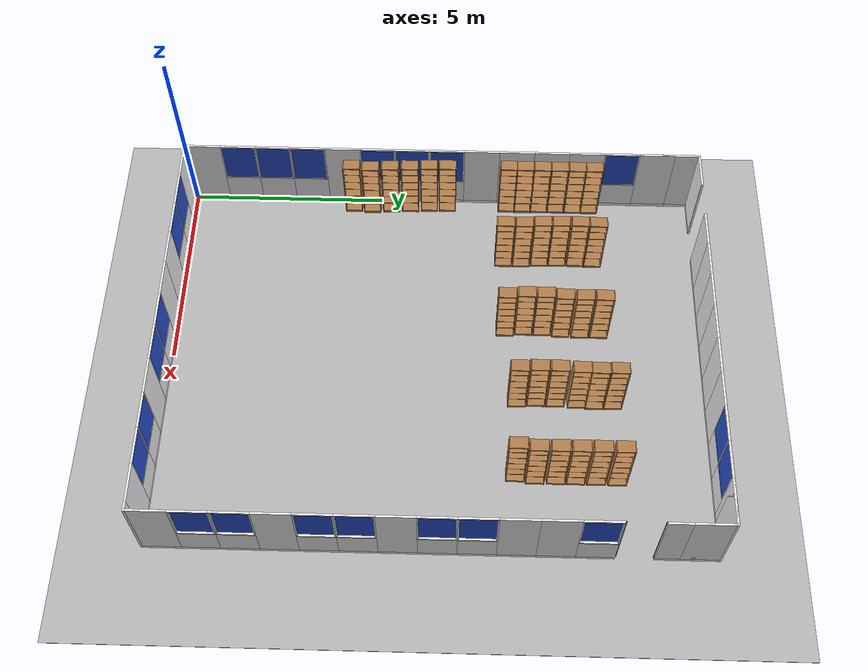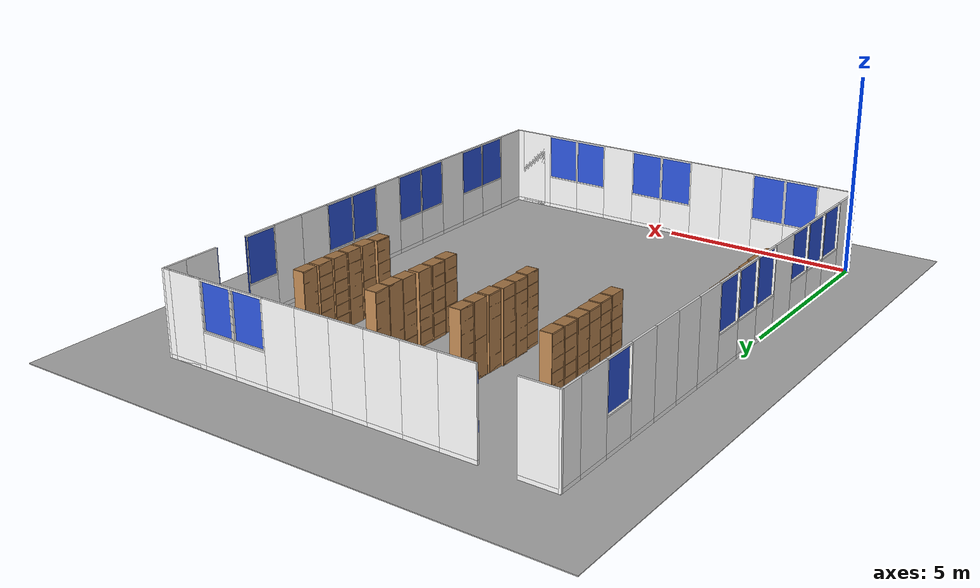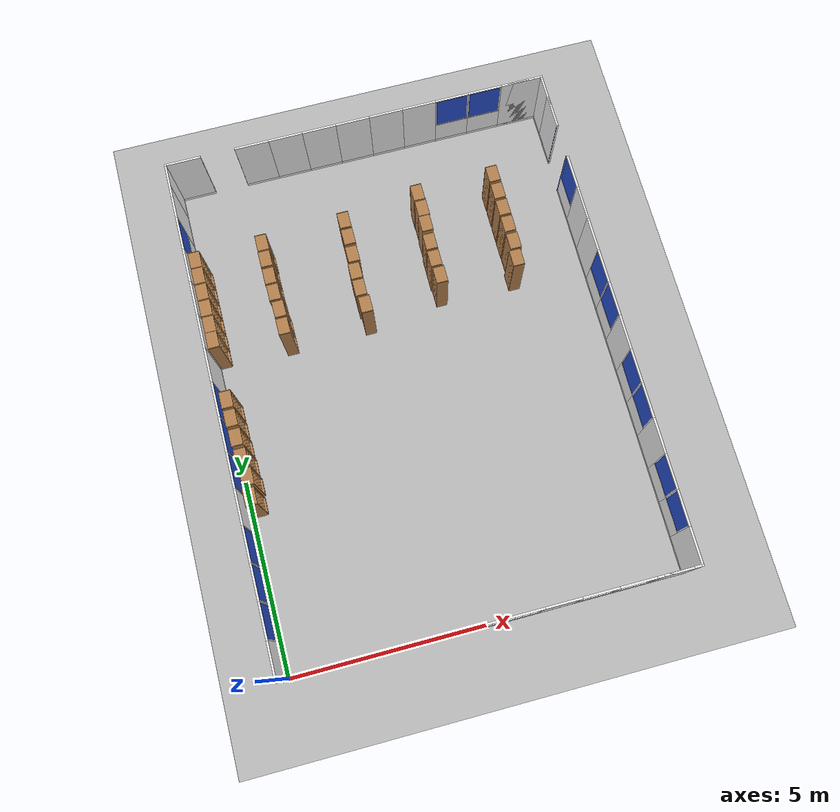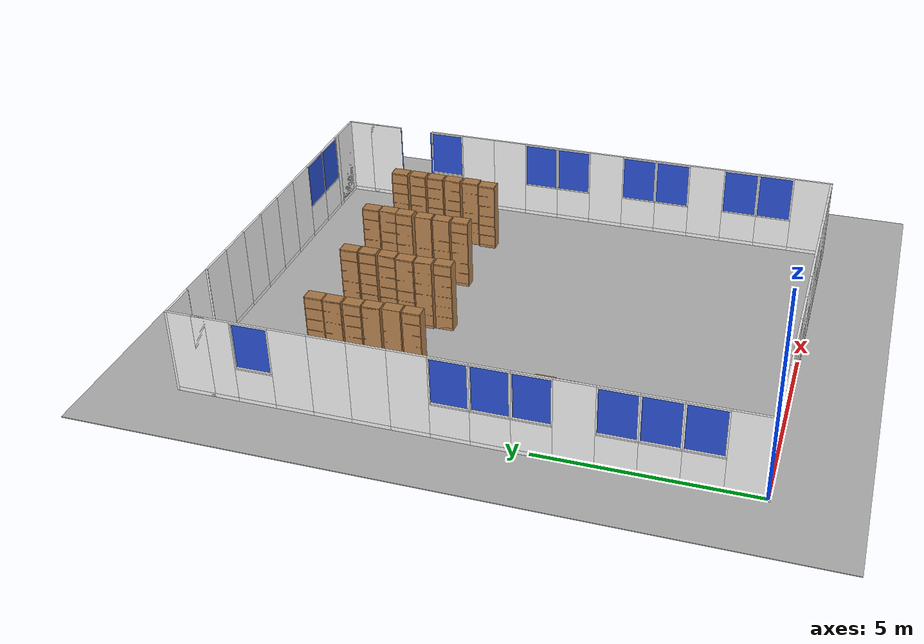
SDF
<sdf version="1.6">
 <world name="robocup_apartment">
  <scene>
   <ambient>0.5 0.5 0.5 1</ambient>
   <shadows>0</shadows>
   <grid>0</grid>
   <background>0.7 0.7 0.7 1</background>
  </scene>
  <physics name="default_physics" default="0" type="ode">
   <real_time_update_rate>333</real_time_update_rate>
   <max_step_size>0.003</max_step_size>
   <ode>
    <solver>
     <type>quick</type>
     <iters>100</iters>
     <sor>1.3</sor>
     <use_dynamic_moi_rescaling>0</use_dynamic_moi_rescaling>
    </solver>
    <constraints>
     <cfm>0.0001</cfm>
     <erp>0.2</erp>
     <contact_max_correcting_vel>100</contact_max_correcting_vel>
     <contact_surface_layer>0.001</contact_surface_layer>
    </constraints>
   </ode>
   <real_time_factor>1</real_time_factor>
  </physics>
  <model name="gplane">
   <pose>5.0375 6.59 0 0 -0 0</pose>
   <link name="body">
    <collision name="gplane_coll">
     <geometry><plane><normal>0 0 1</normal><size>10.075 13.18</size></plane></geometry>
     <surface><contact><ode><kp>1e+06</kp><kd>1</kd></ode></contact></surface>
     <laser_retro>2000</laser_retro>
    </collision>
    <visual name="gplane_vis">
     <geometry><plane><normal>0 0 1</normal><size>10.075 13.18</size></plane></geometry>
     <material>
      <script>
       <uri>model://base_materials/carpet/scripts</uri>
       <uri>model://base_materials/carpet/textures</uri>
       <name>carpet/carpet01</name>
      </script>
     </material>
     <cast_shadows>0</cast_shadows>
    </visual>
    <velocity_decay><linear>0</linear><angular>0</angular></velocity_decay>
   </link>
   <static>1</static>
  </model>
  <light name="inner_point_white1" type="point">
   <pose>4 5 4 0 -0 0</pose>
   <diffuse>0.2 0.2 0.2 1</diffuse>
   <specular>0.1 0.1 0.1 1</specular>
   <attenuation>
    <range>20</range>
    <linear>0.1</linear>
    <constant>0.2</constant>
    <quadratic>0</quadratic>
   </attenuation>
   <cast_shadows>0</cast_shadows>
   <direction>0 0 -1</direction>
  </light>
  <light name="inner_point_white2" type="point">
   <pose>4 10 4 0 -0 0</pose>
   <diffuse>0.2 0.2 0.2 1</diffuse>
   <specular>0.1 0.1 0.1 1</specular>
   <attenuation>
    <range>20</range>
    <linear>0.1</linear>
    <constant>0.2</constant>
    <quadratic>0</quadratic>
   </attenuation>
   <cast_shadows>0</cast_shadows>
   <direction>0 0 -1</direction>
  </light>
  <light name="inner_point_white3" type="point">
   <pose>8 5 4 0 -0 0</pose>
   <diffuse>0.2 0.2 0.2 1</diffuse>
   <specular>0.1 0.1 0.1 1</specular>
   <attenuation>
    <range>20</range>
    <linear>0.1</linear>
    <constant>0.2</constant>
    <quadratic>0</quadratic>
   </attenuation>
   <cast_shadows>0</cast_shadows>
   <direction>0 0 -1</direction>
  </light>
  <light name="inner_point_white4" type="point">
   <pose>8 10 4 0 -0 0</pose>
   <diffuse>0.2 0.2 0.2 1</diffuse>
   <specular>0.1 0.1 0.1 1</specular>
   <attenuation>
    <range>20</range>
    <linear>0.1</linear>
    <constant>0.2</constant>
    <quadratic>0</quadratic>
   </attenuation>
   <cast_shadows>0</cast_shadows>
   <direction>0 0 -1</direction>
  </light>
  <model name="wall_x00y00">
   <link name="link">
    <inertial>
     <mass>50</mass>
     <inertia><ixx>1</ixx><ixy>0</ixy><ixz>0</ixz><iyy>1</iyy><iyz>0</iyz><izz>1</izz></inertia>
    </inertial>
    <visual name="_frame">
     <pose>0 0 1.045 0 -0 0</pose>
     <geometry><box><size>0.055 0.055 2.09</size></box></geometry>
     <material>
      <script><uri>model://base_materials/color/scripts</uri><name>hsr_color/white</name></script>
     </material>
    </visual>
    <velocity_decay><linear>0</linear><angular>0</angular></velocity_decay>
   </link>
   <static>1</static>
   <pose>-0.0275 -0.0275 0 0 -0 0</pose>
  </model>
  <model name="wall_x00y01">
   <link name="link">
    <inertial>
     <mass>50</mass>
     <inertia><ixx>1</ixx><ixy>0</ixy><ixz>0</ixz><iyy>1</iyy><iyz>0</iyz><izz>1</izz></inertia>
    </inertial>
    <visual name="bottom_frame">
     <pose>0 0 0.05 0 -0 0</pose>
     <geometry><box><size>0.055 0.9 0.1</size></box></geometry>
     <material>
      <script><uri>model://base_materials/color/scripts</uri><name>hsr_color/white</name></script>
     </material>
    </visual>
    <visual name="wall">
     <pose>0 0 1.095 0 -0 0</pose>
     <geometry><box><size>0.055 0.9 1.99</size></box></geometry>
     <material>
      <script>
       <uri>model://base_materials/wall/scripts</uri>
       <uri>model://base_materials/wall/textures</uri>
       <name>wall/white_noise</name>
      </script>
     </material>
    </visual>
    <velocity_decay><linear>0</linear><angular>0</angular></velocity_decay>
   </link>
   <static>1</static>
   <pose>-0.0275 0.45 0 0 -0 0</pose>
  </model>
  <model name="wall_x00y02">
   <link name="link">
    <inertial>
     <mass>50</mass>
     <inertia><ixx>1</ixx><ixy>0</ixy><ixz>0</ixz><iyy>1</iyy><iyz>0</iyz><izz>1</izz></inertia>
    </inertial>
    <visual name="bottom_frame">
     <pose>0 0 0.05 0 -0 0</pose>
     <geometry><box><size>0.055 0.9 0.1</size></box></geometry>
     <material>
      <script><uri>model://base_materials/color/scripts</uri><name>hsr_color/white</name></script>
     </material>
    </visual>
    <visual name="wall">
     <pose>0 0 0.4875 0 -0 0</pose>
     <geometry><box><size>0.055 0.9 0.775</size></box></geometry>
     <material>
      <script>
       <uri>model://base_materials/wall/scripts</uri>
       <uri>model://base_materials/wall/textures</uri>
       <name>wall/white_noise</name>
      </script>
     </material>
    </visual>
    <visual name="center_frame">
     <pose>0 0 0.8925 0 -0 0</pose>
     <geometry><box><size>0.055 0.9 0.035</size></box></geometry>
     <material>
      <script><uri>model://base_materials/color/scripts</uri><name>hsr_color/white</name></script>
     </material>
    </visual>
    <visual name="right_frame">
     <pose>0 0.4325 1.48 0 -0 0</pose>
     <geometry><box><size>0.055 0.035 1.14</size></box></geometry>
     <material>
      <script><uri>model://base_materials/color/scripts</uri><name>hsr_color/white</name></script>
     </material>
    </visual>
    <visual name="left_frame">
     <pose>0 -0.4325 1.48 0 -0 0</pose>
     <geometry><box><size>0.055 0.035 1.14</size></box></geometry>
     <material>
      <script><uri>model://base_materials/color/scripts</uri><name>hsr_color/white</name></script>
     </material>
    </visual>
    <visual name="top_frame">
     <pose>0 0 2.07 0 -0 0</pose>
     <geometry><box><size>0.055 0.9 0.04</size></box></geometry>
     <material>
      <script><uri>model://base_materials/color/scripts</uri><name>hsr_color/white</name></script>
     </material>
    </visual>
    <velocity_decay><linear>0</linear><angular>0</angular></velocity_decay>
   </link>
   <static>1</static>
   <pose>-0.0275 1.35 0 0 -0 0</pose>
  </model>
  <model name="wall_x00y03">
   <link name="link">
    <inertial>
     <mass>50</mass>
     <inertia><ixx>1</ixx><ixy>0</ixy><ixz>0</ixz><iyy>1</iyy><iyz>0</iyz><izz>1</izz></inertia>
    </inertial>
    <visual name="bottom_frame">
     <pose>0 0 0.05 0 -0 0</pose>
     <geometry><box><size>0.055 0.9 0.1</size></box></geometry>
     <material>
      <script><uri>model://base_materials/color/scripts</uri><name>hsr_color/white</name></script>
     </material>
    </visual>
    <visual name="wall">
     <pose>0 0 0.4875 0 -0 0</pose>
     <geometry><box><size>0.055 0.9 0.775</size></box></geometry>
     <material>
      <script>
       <uri>model://base_materials/wall/scripts</uri>
       <uri>model://base_materials/wall/textures</uri>
       <name>wall/white_noise</name>
      </script>
     </material>
    </visual>
    <visual name="center_frame">
     <pose>0 0 0.8925 0 -0 0</pose>
     <geometry><box><size>0.055 0.9 0.035</size></box></geometry>
     <material>
      <script><uri>model://base_materials/color/scripts</uri><name>hsr_color/white</name></script>
     </material>
    </visual>
    <visual name="right_frame">
     <pose>0 0.4325 1.48 0 -0 0</pose>
     <geometry><box><size>0.055 0.035 1.14</size></box></geometry>
     <material>
      <script><uri>model://base_materials/color/scripts</uri><name>hsr_color/white</name></script>
     </material>
    </visual>
    <visual name="left_frame">
     <pose>0 -0.4325 1.48 0 -0 0</pose>
     <geometry><box><size>0.055 0.035 1.14</size></box></geometry>
     <material>
      <script><uri>model://base_materials/color/scripts</uri><name>hsr_color/white</name></script>
     </material>
    </visual>
    <visual name="top_frame">
     <pose>0 0 2.07 0 -0 0</pose>
     <geometry><box><size>0.055 0.9 0.04</size></box></geometry>
     <material>
      <script><uri>model://base_materials/color/scripts</uri><name>hsr_color/white</name></script>
     </material>
    </visual>
    <velocity_decay><linear>0</linear><angular>0</angular></velocity_decay>
   </link>
   <static>1</static>
   <pose>-0.0275 2.25 0 0 -0 0</pose>
  </model>
  <model name="wall_x00y04">
   <link name="link">
    <inertial>
     <mass>50</mass>
     <inertia><ixx>1</ixx><ixy>0</ixy><ixz>0</ixz><iyy>1</iyy><iyz>0</iyz><izz>1</izz></inertia>
    </inertial>
    <visual name="bottom_frame">
     <pose>0 0 0.05 0 -0 0</pose>
     <geometry><box><size>0.055 0.9 0.1</size></box></geometry>
     <material>
      <script><uri>model://base_materials/color/scripts</uri><name>hsr_color/white</name></script>
     </material>
    </visual>
    <visual name="wall">
     <pose>0 0 0.4875 0 -0 0</pose>
     <geometry><box><size>0.055 0.9 0.775</size></box></geometry>
     <material>
      <script>
       <uri>model://base_materials/wall/scripts</uri>
       <uri>model://base_materials/wall/textures</uri>
       <name>wall/white_noise</name>
      </script>
     </material>
    </visual>
    <visual name="center_frame">
     <pose>0 0 0.8925 0 -0 0</pose>
     <geometry><box><size>0.055 0.9 0.035</size></box></geometry>
     <material>
      <script><uri>model://base_materials/color/scripts</uri><name>hsr_color/white</name></script>
     </material>
    </visual>
    <visual name="right_frame">
     <pose>0 0.4325 1.48 0 -0 0</pose>
     <geometry><box><size>0.055 0.035 1.14</size></box></geometry>
     <material>
      <script><uri>model://base_materials/color/scripts</uri><name>hsr_color/white</name></script>
     </material>
    </visual>
    <visual name="left_frame">
     <pose>0 -0.4325 1.48 0 -0 0</pose>
     <geometry><box><size>0.055 0.035 1.14</size></box></geometry>
     <material>
      <script><uri>model://base_materials/color/scripts</uri><name>hsr_color/white</name></script>
     </material>
    </visual>
    <visual name="top_frame">
     <pose>0 0 2.07 0 -0 0</pose>
     <geometry><box><size>0.055 0.9 0.04</size></box></geometry>
     <material>
      <script><uri>model://base_materials/color/scripts</uri><name>hsr_color/white</name></script>
     </material>
    </visual>
    <velocity_decay><linear>0</linear><angular>0</angular></velocity_decay>
   </link>
   <static>1</static>
   <pose>-0.0275 3.15 0 0 -0 0</pose>
  </model>
  <model name="wall_x00y05">
   <link name="link">
    <inertial>
     <mass>50</mass>
     <inertia><ixx>1</ixx><ixy>0</ixy><ixz>0</ixz><iyy>1</iyy><iyz>0</iyz><izz>1</izz></inertia>
    </inertial>
    <visual name="bottom_frame">
     <pose>0 0 0.05 0 -0 0</pose>
     <geometry><box><size>0.055 0.9 0.1</size></box></geometry>
     <material>
      <script><uri>model://base_materials/color/scripts</uri><name>hsr_color/white</name></script>
     </material>
    </visual>
    <visual name="wall">
     <pose>0 0 1.095 0 -0 0</pose>
     <geometry><box><size>0.055 0.9 1.99</size></box></geometry>
     <material>
      <script>
       <uri>model://base_materials/wall/scripts</uri>
       <uri>model://base_materials/wall/textures</uri>
       <name>wall/white_noise</name>
      </script>
     </material>
    </visual>
    <velocity_decay><linear>0</linear><angular>0</angular></velocity_decay>
   </link>
   <static>1</static>
   <pose>-0.0275 4.05 0 0 -0 0</pose>
  </model>
  <model name="wall_x00y06">
   <link name="link">
    <inertial>
     <mass>50</mass>
     <inertia><ixx>1</ixx><ixy>0</ixy><ixz>0</ixz><iyy>1</iyy><iyz>0</iyz><izz>1</izz></inertia>
    </inertial>
    <visual name="bottom_frame">
     <pose>0 0 0.05 0 -0 0</pose>
     <geometry><box><size>0.055 0.9 0.1</size></box></geometry>
     <material>
      <script><uri>model://base_materials/color/scripts</uri><name>hsr_color/white</name></script>
     </material>
    </visual>
    <visual name="wall">
     <pose>0 0 0.4875 0 -0 0</pose>
     <geometry><box><size>0.055 0.9 0.775</size></box></geometry>
     <material>
      <script>
       <uri>model://base_materials/wall/scripts</uri>
       <uri>model://base_materials/wall/textures</uri>
       <name>wall/white_noise</name>
      </script>
     </material>
    </visual>
    <visual name="center_frame">
     <pose>0 0 0.8925 0 -0 0</pose>
     <geometry><box><size>0.055 0.9 0.035</size></box></geometry>
     <material>
      <script><uri>model://base_materials/color/scripts</uri><name>hsr_color/white</name></script>
     </material>
    </visual>
    <visual name="right_frame">
     <pose>0 0.4325 1.48 0 -0 0</pose>
     <geometry><box><size>0.055 0.035 1.14</size></box></geometry>
     <material>
      <script><uri>model://base_materials/color/scripts</uri><name>hsr_color/white</name></script>
     </material>
    </visual>
    <visual name="left_frame">
     <pose>0 -0.4325 1.48 0 -0 0</pose>
     <geometry><box><size>0.055 0.035 1.14</size></box></geometry>
     <material>
      <script><uri>model://base_materials/color/scripts</uri><name>hsr_color/white</name></script>
     </material>
    </visual>
    <visual name="top_frame">
     <pose>0 0 2.07 0 -0 0</pose>
     <geometry><box><size>0.055 0.9 0.04</size></box></geometry>
     <material>
      <script><uri>model://base_materials/color/scripts</uri><name>hsr_color/white</name></script>
     </material>
    </visual>
    <velocity_decay><linear>0</linear><angular>0</angular></velocity_decay>
   </link>
   <static>1</static>
   <pose>-0.0275 4.95 0 0 -0 0</pose>
  </model>
  <model name="wall_x00y07">
   <link name="link">
    <inertial>
     <mass>50</mass>
     <inertia><ixx>1</ixx><ixy>0</ixy><ixz>0</ixz><iyy>1</iyy><iyz>0</iyz><izz>1</izz></inertia>
    </inertial>
    <visual name="bottom_frame">
     <pose>0 0 0.05 0 -0 0</pose>
     <geometry><box><size>0.055 0.9 0.1</size></box></geometry>
     <material>
      <script><uri>model://base_materials/color/scripts</uri><name>hsr_color/white</name></script>
     </material>
    </visual>
    <visual name="wall">
     <pose>0 0 0.4875 0 -0 0</pose>
     <geometry><box><size>0.055 0.9 0.775</size></box></geometry>
     <material>
      <script>
       <uri>model://base_materials/wall/scripts</uri>
       <uri>model://base_materials/wall/textures</uri>
       <name>wall/white_noise</name>
      </script>
     </material>
    </visual>
    <visual name="center_frame">
     <pose>0 0 0.8925 0 -0 0</pose>
     <geometry><box><size>0.055 0.9 0.035</size></box></geometry>
     <material>
      <script><uri>model://base_materials/color/scripts</uri><name>hsr_color/white</name></script>
     </material>
    </visual>
    <visual name="right_frame">
     <pose>0 0.4325 1.48 0 -0 0</pose>
     <geometry><box><size>0.055 0.035 1.14</size></box></geometry>
     <material>
      <script><uri>model://base_materials/color/scripts</uri><name>hsr_color/white</name></script>
     </material>
    </visual>
    <visual name="left_frame">
     <pose>0 -0.4325 1.48 0 -0 0</pose>
     <geometry><box><size>0.055 0.035 1.14</size></box></geometry>
     <material>
      <script><uri>model://base_materials/color/scripts</uri><name>hsr_color/white</name></script>
     </material>
    </visual>
    <visual name="top_frame">
     <pose>0 0 2.07 0 -0 0</pose>
     <geometry><box><size>0.055 0.9 0.04</size></box></geometry>
     <material>
      <script><uri>model://base_materials/color/scripts</uri><name>hsr_color/white</name></script>
     </material>
    </visual>
    <velocity_decay><linear>0</linear><angular>0</angular></velocity_decay>
   </link>
   <static>1</static>
   <pose>-0.0275 5.85 0 0 -0 0</pose>
  </model>
  <model name="wall_x00y08">
   <link name="link">
    <inertial>
     <mass>50</mass>
     <inertia><ixx>1</ixx><ixy>0</ixy><ixz>0</ixz><iyy>1</iyy><iyz>0</iyz><izz>1</izz></inertia>
    </inertial>
    <visual name="bottom_frame">
     <pose>0 0 0.05 0 -0 0</pose>
     <geometry><box><size>0.055 0.9 0.1</size></box></geometry>
     <material>
      <script><uri>model://base_materials/color/scripts</uri><name>hsr_color/white</name></script>
     </material>
    </visual>
    <visual name="wall">
     <pose>0 0 0.4875 0 -0 0</pose>
     <geometry><box><size>0.055 0.9 0.775</size></box></geometry>
     <material>
      <script>
       <uri>model://base_materials/wall/scripts</uri>
       <uri>model://base_materials/wall/textures</uri>
       <name>wall/white_noise</name>
      </script>
     </material>
    </visual>
    <visual name="center_frame">
     <pose>0 0 0.8925 0 -0 0</pose>
     <geometry><box><size>0.055 0.9 0.035</size></box></geometry>
     <material>
      <script><uri>model://base_materials/color/scripts</uri><name>hsr_color/white</name></script>
     </material>
    </visual>
    <visual name="right_frame">
     <pose>0 0.4325 1.48 0 -0 0</pose>
     <geometry><box><size>0.055 0.035 1.14</size></box></geometry>
     <material>
      <script><uri>model://base_materials/color/scripts</uri><name>hsr_color/white</name></script>
     </material>
    </visual>
    <visual name="left_frame">
     <pose>0 -0.4325 1.48 0 -0 0</pose>
     <geometry><box><size>0.055 0.035 1.14</size></box></geometry>
     <material>
      <script><uri>model://base_materials/color/scripts</uri><name>hsr_color/white</name></script>
     </material>
    </visual>
    <visual name="top_frame">
     <pose>0 0 2.07 0 -0 0</pose>
     <geometry><box><size>0.055 0.9 0.04</size></box></geometry>
     <material>
      <script><uri>model://base_materials/color/scripts</uri><name>hsr_color/white</name></script>
     </material>
    </visual>
    <velocity_decay><linear>0</linear><angular>0</angular></velocity_decay>
   </link>
   <static>1</static>
   <pose>-0.0275 6.75 0 0 -0 0</pose>
  </model>
  <model name="wall_x00y09">
   <link name="link">
    <inertial>
     <mass>50</mass>
     <inertia><ixx>1</ixx><ixy>0</ixy><ixz>0</ixz><iyy>1</iyy><iyz>0</iyz><izz>1</izz></inertia>
    </inertial>
    <visual name="bottom_frame">
     <pose>0 0 0.05 0 -0 0</pose>
     <geometry><box><size>0.055 0.9 0.1</size></box></geometry>
     <material>
      <script><uri>model://base_materials/color/scripts</uri><name>hsr_color/white</name></script>
     </material>
    </visual>
    <visual name="wall">
     <pose>0 0 1.095 0 -0 0</pose>
     <geometry><box><size>0.055 0.9 1.99</size></box></geometry>
     <material>
      <script>
       <uri>model://base_materials/wall/scripts</uri>
       <uri>model://base_materials/wall/textures</uri>
       <name>wall/white_noise</name>
      </script>
     </material>
    </visual>
    <velocity_decay><linear>0</linear><angular>0</angular></velocity_decay>
   </link>
   <static>1</static>
   <pose>-0.0275 7.65 0 0 -0 0</pose>
  </model>
  <model name="wall_x00y10">
   <link name="link">
    <inertial>
     <mass>50</mass>
     <inertia><ixx>1</ixx><ixy>0</ixy><ixz>0</ixz><iyy>1</iyy><iyz>0</iyz><izz>1</izz></inertia>
    </inertial>
    <visual name="bottom_frame">
     <pose>0 0 0.05 0 -0 0</pose>
     <geometry><box><size>0.055 0.9 0.1</size></box></geometry>
     <material>
      <script><uri>model://base_materials/color/scripts</uri><name>hsr_color/white</name></script>
     </material>
    </visual>
    <visual name="wall">
     <pose>0 0 1.095 0 -0 0</pose>
     <geometry><box><size>0.055 0.9 1.99</size></box></geometry>
     <material>
      <script>
       <uri>model://base_materials/wall/scripts</uri>
       <uri>model://base_materials/wall/textures</uri>
       <name>wall/white_noise</name>
      </script>
     </material>
    </visual>
    <velocity_decay><linear>0</linear><angular>0</angular></velocity_decay>
   </link>
   <static>1</static>
   <pose>-0.0275 8.55 0 0 -0 0</pose>
  </model>
  <model name="wall_x00y11">
   <link name="link">
    <inertial>
     <mass>50</mass>
     <inertia><ixx>1</ixx><ixy>0</ixy><ixz>0</ixz><iyy>1</iyy><iyz>0</iyz><izz>1</izz></inertia>
    </inertial>
    <visual name="bottom_frame">
     <pose>0 0 0.05 0 -0 0</pose>
     <geometry><box><size>0.055 0.9 0.1</size></box></geometry>
     <material>
      <script><uri>model://base_materials/color/scripts</uri><name>hsr_color/white</name></script>
     </material>
    </visual>
    <visual name="wall">
     <pose>0 0 1.095 0 -0 0</pose>
     <geometry><box><size>0.055 0.9 1.99</size></box></geometry>
     <material>
      <script>
       <uri>model://base_materials/wall/scripts</uri>
       <uri>model://base_materials/wall/textures</uri>
       <name>wall/white_noise</name>
      </script>
     </material>
    </visual>
    <velocity_decay><linear>0</linear><angular>0</angular></velocity_decay>
   </link>
   <static>1</static>
   <pose>-0.0275 9.45 0 0 -0 0</pose>
  </model>
  <model name="wall_x00y12">
   <link name="link">
    <inertial>
     <mass>50</mass>
     <inertia><ixx>1</ixx><ixy>0</ixy><ixz>0</ixz><iyy>1</iyy><iyz>0</iyz><izz>1</izz></inertia>
    </inertial>
    <visual name="bottom_frame">
     <pose>0 0 0.05 0 -0 0</pose>
     <geometry><box><size>0.055 0.9 0.1</size></box></geometry>
     <material>
      <script><uri>model://base_materials/color/scripts</uri><name>hsr_color/white</name></script>
     </material>
    </visual>
    <visual name="wall">
     <pose>0 0 1.095 0 -0 0</pose>
     <geometry><box><size>0.055 0.9 1.99</size></box></geometry>
     <material>
      <script>
       <uri>model://base_materials/wall/scripts</uri>
       <uri>model://base_materials/wall/textures</uri>
       <name>wall/white_noise</name>
      </script>
     </material>
    </visual>
    <velocity_decay><linear>0</linear><angular>0</angular></velocity_decay>
   </link>
   <static>1</static>
   <pose>-0.0275 10.35 0 0 -0 0</pose>
  </model>
  <model name="wall_x00y13">
   <link name="link">
    <inertial>
     <mass>50</mass>
     <inertia><ixx>1</ixx><ixy>0</ixy><ixz>0</ixz><iyy>1</iyy><iyz>0</iyz><izz>1</izz></inertia>
    </inertial>
    <visual name="bottom_frame">
     <pose>0 0 0.05 0 -0 0</pose>
     <geometry><box><size>0.055 0.9 0.1</size></box></geometry>
     <material>
      <script><uri>model://base_materials/color/scripts</uri><name>hsr_color/white</name></script>
     </material>
    </visual>
    <visual name="wall">
     <pose>0 0 0.4875 0 -0 0</pose>
     <geometry><box><size>0.055 0.9 0.775</size></box></geometry>
     <material>
      <script>
       <uri>model://base_materials/wall/scripts</uri>
       <uri>model://base_materials/wall/textures</uri>
       <name>wall/white_noise</name>
      </script>
     </material>
    </visual>
    <visual name="center_frame">
     <pose>0 0 0.8925 0 -0 0</pose>
     <geometry><box><size>0.055 0.9 0.035</size></box></geometry>
     <material>
      <script><uri>model://base_materials/color/scripts</uri><name>hsr_color/white</name></script>
     </material>
    </visual>
    <visual name="right_frame">
     <pose>0 0.4325 1.48 0 -0 0</pose>
     <geometry><box><size>0.055 0.035 1.14</size></box></geometry>
     <material>
      <script><uri>model://base_materials/color/scripts</uri><name>hsr_color/white</name></script>
     </material>
    </visual>
    <visual name="left_frame">
     <pose>0 -0.4325 1.48 0 -0 0</pose>
     <geometry><box><size>0.055 0.035 1.14</size></box></geometry>
     <material>
      <script><uri>model://base_materials/color/scripts</uri><name>hsr_color/white</name></script>
     </material>
    </visual>
    <visual name="top_frame">
     <pose>0 0 2.07 0 -0 0</pose>
     <geometry><box><size>0.055 0.9 0.04</size></box></geometry>
     <material>
      <script><uri>model://base_materials/color/scripts</uri><name>hsr_color/white</name></script>
     </material>
    </visual>
    <velocity_decay><linear>0</linear><angular>0</angular></velocity_decay>
   </link>
   <static>1</static>
   <pose>-0.0275 11.25 0 0 -0 0</pose>
  </model>
  <model name="wall_x00y14">
   <link name="link">
    <inertial>
     <mass>50</mass>
     <inertia><ixx>1</ixx><ixy>0</ixy><ixz>0</ixz><iyy>1</iyy><iyz>0</iyz><izz>1</izz></inertia>
    </inertial>
    <visual name="bottom_frame">
     <pose>0 0 0.05 0 -0 0</pose>
     <geometry><box><size>0.055 0.9 0.1</size></box></geometry>
     <material>
      <script><uri>model://base_materials/color/scripts</uri><name>hsr_color/white</name></script>
     </material>
    </visual>
    <visual name="wall">
     <pose>0 0 1.095 0 -0 0</pose>
     <geometry><box><size>0.055 0.9 1.99</size></box></geometry>
     <material>
      <script>
       <uri>model://base_materials/wall/scripts</uri>
       <uri>model://base_materials/wall/textures</uri>
       <name>wall/white_noise</name>
      </script>
     </material>
    </visual>
    <velocity_decay><linear>0</linear><angular>0</angular></velocity_decay>
   </link>
   <static>1</static>
   <pose>-0.0275 12.15 0 0 -0 0</pose>
  </model>
  <model name="wall_x00y15">
   <link name="link">
    <inertial>
     <mass>50</mass>
     <inertia><ixx>1</ixx><ixy>0</ixy><ixz>0</ixz><iyy>1</iyy><iyz>0</iyz><izz>1</izz></inertia>
    </inertial>
    <visual name="bottom_frame">
     <pose>0 0 0.05 0 -0 0</pose>
     <geometry><box><size>0.055 0.9 0.1</size></box></geometry>
     <material>
      <script><uri>model://base_materials/color/scripts</uri><name>hsr_color/white</name></script>
     </material>
    </visual>
    <visual name="wall">
     <pose>0 0 1.095 0 -0 0</pose>
     <geometry><box><size>0.055 0.9 1.99</size></box></geometry>
     <material>
      <script>
       <uri>model://base_materials/wall/scripts</uri>
       <uri>model://base_materials/wall/textures</uri>
       <name>wall/white_noise</name>
      </script>
     </material>
    </visual>
    <velocity_decay><linear>0</linear><angular>0</angular></velocity_decay>
   </link>
   <static>1</static>
   <pose>-0.0275 12.73 0 0 -0 0</pose>
  </model>
  <model name="wall_x00y16">
   <link name="link">
    <inertial>
     <mass>50</mass>
     <inertia><ixx>1</ixx><ixy>0</ixy><ixz>0</ixz><iyy>1</iyy><iyz>0</iyz><izz>1</izz></inertia>
    </inertial>
    <visual name="_frame">
     <pose>0 0 1.045 0 -0 0</pose>
     <geometry><box><size>0.055 0.055 2.09</size></box></geometry>
     <material>
      <script><uri>model://base_materials/color/scripts</uri><name>hsr_color/white</name></script>
     </material>
    </visual>
    <velocity_decay><linear>0</linear><angular>0</angular></velocity_decay>
   </link>
   <static>1</static>
   <pose>-0.0275 13.2075 0 0 -0 0</pose>
  </model>
  <model name="wall_x01y00">
   <link name="link">
    <inertial>
     <mass>50</mass>
     <inertia><ixx>1</ixx><ixy>0</ixy><ixz>0</ixz><iyy>1</iyy><iyz>0</iyz><izz>1</izz></inertia>
    </inertial>
    <visual name="bottom_frame">
     <pose>0 0 0.05 0 -0 0</pose>
     <geometry><box><size>0.055 0.9 0.1</size></box></geometry>
     <material>
      <script><uri>model://base_materials/color/scripts</uri><name>hsr_color/white</name></script>
     </material>
    </visual>
    <visual name="wall">
     <pose>0 0 1.095 0 -0 0</pose>
     <geometry><box><size>0.055 0.9 1.99</size></box></geometry>
     <material>
      <script>
       <uri>model://base_materials/wall/scripts</uri>
       <uri>model://base_materials/wall/textures</uri>
       <name>wall/white_noise</name>
      </script>
     </material>
    </visual>
    <velocity_decay><linear>0</linear><angular>0</angular></velocity_decay>
   </link>
   <static>1</static>
   <pose>0.45 -0.0275 0 0 -0 1.5708</pose>
  </model>
  <model name="wall_x02y00">
   <link name="link">
    <inertial>
     <mass>50</mass>
     <inertia><ixx>1</ixx><ixy>0</ixy><ixz>0</ixz><iyy>1</iyy><iyz>0</iyz><izz>1</izz></inertia>
    </inertial>
    <visual name="bottom_frame">
     <pose>0 0 0.05 0 -0 0</pose>
     <geometry><box><size>0.055 0.9 0.1</size></box></geometry>
     <material>
      <script><uri>model://base_materials/color/scripts</uri><name>hsr_color/white</name></script>
     </material>
    </visual>
    <visual name="wall">
     <pose>0 0 0.4875 0 -0 0</pose>
     <geometry><box><size>0.055 0.9 0.775</size></box></geometry>
     <material>
      <script>
       <uri>model://base_materials/wall/scripts</uri>
       <uri>model://base_materials/wall/textures</uri>
       <name>wall/white_noise</name>
      </script>
     </material>
    </visual>
    <visual name="center_frame">
     <pose>0 0 0.8925 0 -0 0</pose>
     <geometry><box><size>0.055 0.9 0.035</size></box></geometry>
     <material>
      <script><uri>model://base_materials/color/scripts</uri><name>hsr_color/white</name></script>
     </material>
    </visual>
    <visual name="right_frame">
     <pose>0 0.4325 1.48 0 -0 0</pose>
     <geometry><box><size>0.055 0.035 1.14</size></box></geometry>
     <material>
      <script><uri>model://base_materials/color/scripts</uri><name>hsr_color/white</name></script>
     </material>
    </visual>
    <visual name="left_frame">
     <pose>0 -0.4325 1.48 0 -0 0</pose>
     <geometry><box><size>0.055 0.035 1.14</size></box></geometry>
     <material>
      <script><uri>model://base_materials/color/scripts</uri><name>hsr_color/white</name></script>
     </material>
    </visual>
    <visual name="top_frame">
     <pose>0 0 2.07 0 -0 0</pose>
     <geometry><box><size>0.055 0.9 0.04</size></box></geometry>
     <material>
      <script><uri>model://base_materials/color/scripts</uri><name>hsr_color/white</name></script>
     </material>
    </visual>
    <velocity_decay><linear>0</linear><angular>0</angular></velocity_decay>
   </link>
   <static>1</static>
   <pose>1.35 -0.0275 0 0 -0 1.5708</pose>
  </model>
  <model name="wall_x03y00">
   <link name="link">
    <inertial>
     <mass>50</mass>
     <inertia><ixx>1</ixx><ixy>0</ixy><ixz>0</ixz><iyy>1</iyy><iyz>0</iyz><izz>1</izz></inertia>
    </inertial>
    <visual name="bottom_frame">
     <pose>0 0 0.05 0 -0 0</pose>
     <geometry><box><size>0.055 0.9 0.1</size></box></geometry>
     <material>
      <script><uri>model://base_materials/color/scripts</uri><name>hsr_color/white</name></script>
     </material>
    </visual>
    <visual name="wall">
     <pose>0 0 0.4875 0 -0 0</pose>
     <geometry><box><size>0.055 0.9 0.775</size></box></geometry>
     <material>
      <script>
       <uri>model://base_materials/wall/scripts</uri>
       <uri>model://base_materials/wall/textures</uri>
       <name>wall/white_noise</name>
      </script>
     </material>
    </visual>
    <visual name="center_frame">
     <pose>0 0 0.8925 0 -0 0</pose>
     <geometry><box><size>0.055 0.9 0.035</size></box></geometry>
     <material>
      <script><uri>model://base_materials/color/scripts</uri><name>hsr_color/white</name></script>
     </material>
    </visual>
    <visual name="right_frame">
     <pose>0 0.4325 1.48 0 -0 0</pose>
     <geometry><box><size>0.055 0.035 1.14</size></box></geometry>
     <material>
      <script><uri>model://base_materials/color/scripts</uri><name>hsr_color/white</name></script>
     </material>
    </visual>
    <visual name="left_frame">
     <pose>0 -0.4325 1.48 0 -0 0</pose>
     <geometry><box><size>0.055 0.035 1.14</size></box></geometry>
     <material>
      <script><uri>model://base_materials/color/scripts</uri><name>hsr_color/white</name></script>
     </material>
    </visual>
    <visual name="top_frame">
     <pose>0 0 2.07 0 -0 0</pose>
     <geometry><box><size>0.055 0.9 0.04</size></box></geometry>
     <material>
      <script><uri>model://base_materials/color/scripts</uri><name>hsr_color/white</name></script>
     </material>
    </visual>
    <velocity_decay><linear>0</linear><angular>0</angular></velocity_decay>
   </link>
   <static>1</static>
   <pose>2.25 -0.0275 0 0 -0 1.5708</pose>
  </model>
  <model name="wall_x04y00">
   <link name="link">
    <inertial>
     <mass>50</mass>
     <inertia><ixx>1</ixx><ixy>0</ixy><ixz>0</ixz><iyy>1</iyy><iyz>0</iyz><izz>1</izz></inertia>
    </inertial>
    <visual name="bottom_frame">
     <pose>0 0 0.05 0 -0 0</pose>
     <geometry><box><size>0.055 0.9 0.1</size></box></geometry>
     <material>
      <script><uri>model://base_materials/color/scripts</uri><name>hsr_color/white</name></script>
     </material>
    </visual>
    <visual name="wall">
     <pose>0 0 1.095 0 -0 0</pose>
     <geometry><box><size>0.055 0.9 1.99</size></box></geometry>
     <material>
      <script>
       <uri>model://base_materials/wall/scripts</uri>
       <uri>model://base_materials/wall/textures</uri>
       <name>wall/white_noise</name>
      </script>
     </material>
    </visual>
    <velocity_decay><linear>0</linear><angular>0</angular></velocity_decay>
   </link>
   <static>1</static>
   <pose>3.15 -0.0275 0 0 -0 1.5708</pose>
  </model>
  <model name="wall_x05y00">
   <link name="link">
    <inertial>
     <mass>50</mass>
     <inertia><ixx>1</ixx><ixy>0</ixy><ixz>0</ixz><iyy>1</iyy><iyz>0</iyz><izz>1</izz></inertia>
    </inertial>
    <visual name="bottom_frame">
     <pose>0 0 0.05 0 -0 0</pose>
     <geometry><box><size>0.055 0.9 0.1</size></box></geometry>
     <material>
      <script><uri>model://base_materials/color/scripts</uri><name>hsr_color/white</name></script>
     </material>
    </visual>
    <visual name="wall">
     <pose>0 0 1.095 0 -0 0</pose>
     <geometry><box><size>0.055 0.9 1.99</size></box></geometry>
     <material>
      <script>
       <uri>model://base_materials/wall/scripts</uri>
       <uri>model://base_materials/wall/textures</uri>
       <name>wall/white_noise</name>
      </script>
     </material>
    </visual>
    <velocity_decay><linear>0</linear><angular>0</angular></velocity_decay>
   </link>
   <static>1</static>
   <pose>4.05 -0.0275 0 0 -0 1.5708</pose>
  </model>
  <model name="wall_x06y00">
   <link name="link">
    <inertial>
     <mass>50</mass>
     <inertia><ixx>1</ixx><ixy>0</ixy><ixz>0</ixz><iyy>1</iyy><iyz>0</iyz><izz>1</izz></inertia>
    </inertial>
    <visual name="bottom_frame">
     <pose>0 0 0.05 0 -0 0</pose>
     <geometry><box><size>0.055 0.9 0.1</size></box></geometry>
     <material>
      <script><uri>model://base_materials/color/scripts</uri><name>hsr_color/white</name></script>
     </material>
    </visual>
    <visual name="wall">
     <pose>0 0 0.4875 0 -0 0</pose>
     <geometry><box><size>0.055 0.9 0.775</size></box></geometry>
     <material>
      <script>
       <uri>model://base_materials/wall/scripts</uri>
       <uri>model://base_materials/wall/textures</uri>
       <name>wall/white_noise</name>
      </script>
     </material>
    </visual>
    <visual name="center_frame">
     <pose>0 0 0.8925 0 -0 0</pose>
     <geometry><box><size>0.055 0.9 0.035</size></box></geometry>
     <material>
      <script><uri>model://base_materials/color/scripts</uri><name>hsr_color/white</name></script>
     </material>
    </visual>
    <visual name="right_frame">
     <pose>0 0.4325 1.48 0 -0 0</pose>
     <geometry><box><size>0.055 0.035 1.14</size></box></geometry>
     <material>
      <script><uri>model://base_materials/color/scripts</uri><name>hsr_color/white</name></script>
     </material>
    </visual>
    <visual name="left_frame">
     <pose>0 -0.4325 1.48 0 -0 0</pose>
     <geometry><box><size>0.055 0.035 1.14</size></box></geometry>
     <material>
      <script><uri>model://base_materials/color/scripts</uri><name>hsr_color/white</name></script>
     </material>
    </visual>
    <visual name="top_frame">
     <pose>0 0 2.07 0 -0 0</pose>
     <geometry><box><size>0.055 0.9 0.04</size></box></geometry>
     <material>
      <script><uri>model://base_materials/color/scripts</uri><name>hsr_color/white</name></script>
     </material>
    </visual>
    <velocity_decay><linear>0</linear><angular>0</angular></velocity_decay>
   </link>
   <static>1</static>
   <pose>4.95 -0.0275 0 0 -0 1.5708</pose>
  </model>
  <model name="wall_x07y00">
   <link name="link">
    <inertial>
     <mass>50</mass>
     <inertia><ixx>1</ixx><ixy>0</ixy><ixz>0</ixz><iyy>1</iyy><iyz>0</iyz><izz>1</izz></inertia>
    </inertial>
    <visual name="bottom_frame">
     <pose>0 0 0.05 0 -0 0</pose>
     <geometry><box><size>0.055 0.9 0.1</size></box></geometry>
     <material>
      <script><uri>model://base_materials/color/scripts</uri><name>hsr_color/white</name></script>
     </material>
    </visual>
    <visual name="wall">
     <pose>0 0 0.4875 0 -0 0</pose>
     <geometry><box><size>0.055 0.9 0.775</size></box></geometry>
     <material>
      <script>
       <uri>model://base_materials/wall/scripts</uri>
       <uri>model://base_materials/wall/textures</uri>
       <name>wall/white_noise</name>
      </script>
     </material>
    </visual>
    <visual name="center_frame">
     <pose>0 0 0.8925 0 -0 0</pose>
     <geometry><box><size>0.055 0.9 0.035</size></box></geometry>
     <material>
      <script><uri>model://base_materials/color/scripts</uri><name>hsr_color/white</name></script>
     </material>
    </visual>
    <visual name="right_frame">
     <pose>0 0.4325 1.48 0 -0 0</pose>
     <geometry><box><size>0.055 0.035 1.14</size></box></geometry>
     <material>
      <script><uri>model://base_materials/color/scripts</uri><name>hsr_color/white</name></script>
     </material>
    </visual>
    <visual name="left_frame">
     <pose>0 -0.4325 1.48 0 -0 0</pose>
     <geometry><box><size>0.055 0.035 1.14</size></box></geometry>
     <material>
      <script><uri>model://base_materials/color/scripts</uri><name>hsr_color/white</name></script>
     </material>
    </visual>
    <visual name="top_frame">
     <pose>0 0 2.07 0 -0 0</pose>
     <geometry><box><size>0.055 0.9 0.04</size></box></geometry>
     <material>
      <script><uri>model://base_materials/color/scripts</uri><name>hsr_color/white</name></script>
     </material>
    </visual>
    <velocity_decay><linear>0</linear><angular>0</angular></velocity_decay>
   </link>
   <static>1</static>
   <pose>5.85 -0.0275 0 0 -0 1.5708</pose>
  </model>
  <model name="wall_x08y00">
   <link name="link">
    <inertial>
     <mass>50</mass>
     <inertia><ixx>1</ixx><ixy>0</ixy><ixz>0</ixz><iyy>1</iyy><iyz>0</iyz><izz>1</izz></inertia>
    </inertial>
    <visual name="bottom_frame">
     <pose>0 0 0.05 0 -0 0</pose>
     <geometry><box><size>0.055 0.9 0.1</size></box></geometry>
     <material>
      <script><uri>model://base_materials/color/scripts</uri><name>hsr_color/white</name></script>
     </material>
    </visual>
    <visual name="wall">
     <pose>0 0 1.095 0 -0 0</pose>
     <geometry><box><size>0.055 0.9 1.99</size></box></geometry>
     <material>
      <script>
       <uri>model://base_materials/wall/scripts</uri>
       <uri>model://base_materials/wall/textures</uri>
       <name>wall/white_noise</name>
      </script>
     </material>
    </visual>
    <velocity_decay><linear>0</linear><angular>0</angular></velocity_decay>
   </link>
   <static>1</static>
   <pose>6.75 -0.0275 0 0 -0 1.5708</pose>
  </model>
  <model name="wall_x09y00">
   <link name="link">
    <inertial>
     <mass>50</mass>
     <inertia><ixx>1</ixx><ixy>0</ixy><ixz>0</ixz><iyy>1</iyy><iyz>0</iyz><izz>1</izz></inertia>
    </inertial>
    <visual name="bottom_frame">
     <pose>0 0 0.05 0 -0 0</pose>
     <geometry><box><size>0.055 0.9 0.1</size></box></geometry>
     <material>
      <script><uri>model://base_materials/color/scripts</uri><name>hsr_color/white</name></script>
     </material>
    </visual>
    <visual name="wall">
     <pose>0 0 0.4875 0 -0 0</pose>
     <geometry><box><size>0.055 0.9 0.775</size></box></geometry>
     <material>
      <script>
       <uri>model://base_materials/wall/scripts</uri>
       <uri>model://base_materials/wall/textures</uri>
       <name>wall/white_noise</name>
      </script>
     </material>
    </visual>
    <visual name="center_frame">
     <pose>0 0 0.8925 0 -0 0</pose>
     <geometry><box><size>0.055 0.9 0.035</size></box></geometry>
     <material>
      <script><uri>model://base_materials/color/scripts</uri><name>hsr_color/white</name></script>
     </material>
    </visual>
    <visual name="right_frame">
     <pose>0 0.4325 1.48 0 -0 0</pose>
     <geometry><box><size>0.055 0.035 1.14</size></box></geometry>
     <material>
      <script><uri>model://base_materials/color/scripts</uri><name>hsr_color/white</name></script>
     </material>
    </visual>
    <visual name="left_frame">
     <pose>0 -0.4325 1.48 0 -0 0</pose>
     <geometry><box><size>0.055 0.035 1.14</size></box></geometry>
     <material>
      <script><uri>model://base_materials/color/scripts</uri><name>hsr_color/white</name></script>
     </material>
    </visual>
    <visual name="top_frame">
     <pose>0 0 2.07 0 -0 0</pose>
     <geometry><box><size>0.055 0.9 0.04</size></box></geometry>
     <material>
      <script><uri>model://base_materials/color/scripts</uri><name>hsr_color/white</name></script>
     </material>
    </visual>
    <velocity_decay><linear>0</linear><angular>0</angular></velocity_decay>
   </link>
   <static>1</static>
   <pose>7.65 -0.0275 0 0 -0 1.5708</pose>
  </model>
  <model name="wall_x10y00">
   <link name="link">
    <inertial>
     <mass>50</mass>
     <inertia><ixx>1</ixx><ixy>0</ixy><ixz>0</ixz><iyy>1</iyy><iyz>0</iyz><izz>1</izz></inertia>
    </inertial>
    <visual name="bottom_frame">
     <pose>0 0 0.05 0 -0 0</pose>
     <geometry><box><size>0.055 0.9 0.1</size></box></geometry>
     <material>
      <script><uri>model://base_materials/color/scripts</uri><name>hsr_color/white</name></script>
     </material>
    </visual>
    <visual name="wall">
     <pose>0 0 0.4875 0 -0 0</pose>
     <geometry><box><size>0.055 0.9 0.775</size></box></geometry>
     <material>
      <script>
       <uri>model://base_materials/wall/scripts</uri>
       <uri>model://base_materials/wall/textures</uri>
       <name>wall/white_noise</name>
      </script>
     </material>
    </visual>
    <visual name="center_frame">
     <pose>0 0 0.8925 0 -0 0</pose>
     <geometry><box><size>0.055 0.9 0.035</size></box></geometry>
     <material>
      <script><uri>model://base_materials/color/scripts</uri><name>hsr_color/white</name></script>
     </material>
    </visual>
    <visual name="right_frame">
     <pose>0 0.4325 1.48 0 -0 0</pose>
     <geometry><box><size>0.055 0.035 1.14</size></box></geometry>
     <material>
      <script><uri>model://base_materials/color/scripts</uri><name>hsr_color/white</name></script>
     </material>
    </visual>
    <visual name="left_frame">
     <pose>0 -0.4325 1.48 0 -0 0</pose>
     <geometry><box><size>0.055 0.035 1.14</size></box></geometry>
     <material>
      <script><uri>model://base_materials/color/scripts</uri><name>hsr_color/white</name></script>
     </material>
    </visual>
    <visual name="top_frame">
     <pose>0 0 2.07 0 -0 0</pose>
     <geometry><box><size>0.055 0.9 0.04</size></box></geometry>
     <material>
      <script><uri>model://base_materials/color/scripts</uri><name>hsr_color/white</name></script>
     </material>
    </visual>
    <velocity_decay><linear>0</linear><angular>0</angular></velocity_decay>
   </link>
   <static>1</static>
   <pose>8.55 -0.0275 0 0 -0 1.5708</pose>
  </model>
  <model name="wall_x11y00">
   <link name="link">
    <inertial>
     <mass>50</mass>
     <inertia><ixx>1</ixx><ixy>0</ixy><ixz>0</ixz><iyy>1</iyy><iyz>0</iyz><izz>1</izz></inertia>
    </inertial>
    <visual name="bottom_frame">
     <pose>0 0 0.05 0 -0 0</pose>
     <geometry><box><size>0.055 0.9 0.1</size></box></geometry>
     <material>
      <script><uri>model://base_materials/color/scripts</uri><name>hsr_color/white</name></script>
     </material>
    </visual>
    <visual name="wall">
     <pose>0 0 1.095 0 -0 0</pose>
     <geometry><box><size>0.055 0.9 1.99</size></box></geometry>
     <material>
      <script>
       <uri>model://base_materials/wall/scripts</uri>
       <uri>model://base_materials/wall/textures</uri>
       <name>wall/white_noise</name>
      </script>
     </material>
    </visual>
    <velocity_decay><linear>0</linear><angular>0</angular></velocity_decay>
   </link>
   <static>1</static>
   <pose>9.45 -0.0275 0 0 -0 1.5708</pose>
  </model>
  <model name="wall_x12y00">
   <link name="link">
    <inertial>
     <mass>50</mass>
     <inertia><ixx>1</ixx><ixy>0</ixy><ixz>0</ixz><iyy>1</iyy><iyz>0</iyz><izz>1</izz></inertia>
    </inertial>
    <visual name="bottom_frame">
     <pose>0 0 0.05 0 -0 0</pose>
     <geometry><box><size>0.055 0.9 0.1</size></box></geometry>
     <material>
      <script><uri>model://base_materials/color/scripts</uri><name>hsr_color/white</name></script>
     </material>
    </visual>
    <visual name="wall">
     <pose>0 0 1.095 0 -0 0</pose>
     <geometry><box><size>0.055 0.9 1.99</size></box></geometry>
     <material>
      <script>
       <uri>model://base_materials/wall/scripts</uri>
       <uri>model://base_materials/wall/textures</uri>
       <name>wall/white_noise</name>
      </script>
     </material>
    </visual>
    <velocity_decay><linear>0</linear><angular>0</angular></velocity_decay>
   </link>
   <static>1</static>
   <pose>9.625 -0.0275 0 0 -0 1.5708</pose>
  </model>
  <model name="wall_x13y00">
   <link name="link">
    <inertial>
     <mass>50</mass>
     <inertia><ixx>1</ixx><ixy>0</ixy><ixz>0</ixz><iyy>1</iyy><iyz>0</iyz><izz>1</izz></inertia>
    </inertial>
    <visual name="_frame">
     <pose>0 0 1.045 0 -0 0</pose>
     <geometry><box><size>0.055 0.055 2.09</size></box></geometry>
     <material>
      <script><uri>model://base_materials/color/scripts</uri><name>hsr_color/white</name></script>
     </material>
    </visual>
    <velocity_decay><linear>0</linear><angular>0</angular></velocity_decay>
   </link>
   <static>1</static>
   <pose>10.1025 -0.0275 0 0 -0 0</pose>
  </model>
  <model name="wall_x13y01">
   <link name="link">
    <inertial>
     <mass>50</mass>
     <inertia><ixx>1</ixx><ixy>0</ixy><ixz>0</ixz><iyy>1</iyy><iyz>0</iyz><izz>1</izz></inertia>
    </inertial>
    <visual name="bottom_frame">
     <pose>0 0 0.05 0 -0 0</pose>
     <geometry><box><size>0.055 0.9 0.1</size></box></geometry>
     <material>
      <script><uri>model://base_materials/color/scripts</uri><name>hsr_color/white</name></script>
     </material>
    </visual>
    <visual name="wall">
     <pose>0 0 1.095 0 -0 0</pose>
     <geometry><box><size>0.055 0.9 1.99</size></box></geometry>
     <material>
      <script>
       <uri>model://base_materials/wall/scripts</uri>
       <uri>model://base_materials/wall/textures</uri>
       <name>wall/white_noise</name>
      </script>
     </material>
    </visual>
    <velocity_decay><linear>0</linear><angular>0</angular></velocity_decay>
   </link>
   <static>1</static>
   <pose>10.1025 0.45 0 0 -0 0</pose>
  </model>
  <model name="wall_x13y02">
   <link name="link">
    <inertial>
     <mass>50</mass>
     <inertia><ixx>1</ixx><ixy>0</ixy><ixz>0</ixz><iyy>1</iyy><iyz>0</iyz><izz>1</izz></inertia>
    </inertial>
    <visual name="bottom_frame">
     <pose>0 0 0.05 0 -0 0</pose>
     <geometry><box><size>0.055 0.9 0.1</size></box></geometry>
     <material>
      <script><uri>model://base_materials/color/scripts</uri><name>hsr_color/white</name></script>
     </material>
    </visual>
    <visual name="wall">
     <pose>0 0 0.4875 0 -0 0</pose>
     <geometry><box><size>0.055 0.9 0.775</size></box></geometry>
     <material>
      <script>
       <uri>model://base_materials/wall/scripts</uri>
       <uri>model://base_materials/wall/textures</uri>
       <name>wall/white_noise</name>
      </script>
     </material>
    </visual>
    <visual name="center_frame">
     <pose>0 0 0.8925 0 -0 0</pose>
     <geometry><box><size>0.055 0.9 0.035</size></box></geometry>
     <material>
      <script><uri>model://base_materials/color/scripts</uri><name>hsr_color/white</name></script>
     </material>
    </visual>
    <visual name="right_frame">
     <pose>0 0.4325 1.48 0 -0 0</pose>
     <geometry><box><size>0.055 0.035 1.14</size></box></geometry>
     <material>
      <script><uri>model://base_materials/color/scripts</uri><name>hsr_color/white</name></script>
     </material>
    </visual>
    <visual name="left_frame">
     <pose>0 -0.4325 1.48 0 -0 0</pose>
     <geometry><box><size>0.055 0.035 1.14</size></box></geometry>
     <material>
      <script><uri>model://base_materials/color/scripts</uri><name>hsr_color/white</name></script>
     </material>
    </visual>
    <visual name="top_frame">
     <pose>0 0 2.07 0 -0 0</pose>
     <geometry><box><size>0.055 0.9 0.04</size></box></geometry>
     <material>
      <script><uri>model://base_materials/color/scripts</uri><name>hsr_color/white</name></script>
     </material>
    </visual>
    <velocity_decay><linear>0</linear><angular>0</angular></velocity_decay>
   </link>
   <static>1</static>
   <pose>10.1025 1.35 0 0 -0 0</pose>
  </model>
  <model name="wall_x13y03">
   <link name="link">
    <inertial>
     <mass>50</mass>
     <inertia><ixx>1</ixx><ixy>0</ixy><ixz>0</ixz><iyy>1</iyy><iyz>0</iyz><izz>1</izz></inertia>
    </inertial>
    <visual name="bottom_frame">
     <pose>0 0 0.05 0 -0 0</pose>
     <geometry><box><size>0.055 0.9 0.1</size></box></geometry>
     <material>
      <script><uri>model://base_materials/color/scripts</uri><name>hsr_color/white</name></script>
     </material>
    </visual>
    <visual name="wall">
     <pose>0 0 0.4875 0 -0 0</pose>
     <geometry><box><size>0.055 0.9 0.775</size></box></geometry>
     <material>
      <script>
       <uri>model://base_materials/wall/scripts</uri>
       <uri>model://base_materials/wall/textures</uri>
       <name>wall/white_noise</name>
      </script>
     </material>
    </visual>
    <visual name="center_frame">
     <pose>0 0 0.8925 0 -0 0</pose>
     <geometry><box><size>0.055 0.9 0.035</size></box></geometry>
     <material>
      <script><uri>model://base_materials/color/scripts</uri><name>hsr_color/white</name></script>
     </material>
    </visual>
    <visual name="right_frame">
     <pose>0 0.4325 1.48 0 -0 0</pose>
     <geometry><box><size>0.055 0.035 1.14</size></box></geometry>
     <material>
      <script><uri>model://base_materials/color/scripts</uri><name>hsr_color/white</name></script>
     </material>
    </visual>
    <visual name="left_frame">
     <pose>0 -0.4325 1.48 0 -0 0</pose>
     <geometry><box><size>0.055 0.035 1.14</size></box></geometry>
     <material>
      <script><uri>model://base_materials/color/scripts</uri><name>hsr_color/white</name></script>
     </material>
    </visual>
    <visual name="top_frame">
     <pose>0 0 2.07 0 -0 0</pose>
     <geometry><box><size>0.055 0.9 0.04</size></box></geometry>
     <material>
      <script><uri>model://base_materials/color/scripts</uri><name>hsr_color/white</name></script>
     </material>
    </visual>
    <velocity_decay><linear>0</linear><angular>0</angular></velocity_decay>
   </link>
   <static>1</static>
   <pose>10.1025 2.25 0 0 -0 0</pose>
  </model>
  <model name="wall_x13y04">
   <link name="link">
    <inertial>
     <mass>50</mass>
     <inertia><ixx>1</ixx><ixy>0</ixy><ixz>0</ixz><iyy>1</iyy><iyz>0</iyz><izz>1</izz></inertia>
    </inertial>
    <visual name="bottom_frame">
     <pose>0 0 0.05 0 -0 0</pose>
     <geometry><box><size>0.055 0.9 0.1</size></box></geometry>
     <material>
      <script><uri>model://base_materials/color/scripts</uri><name>hsr_color/white</name></script>
     </material>
    </visual>
    <visual name="wall">
     <pose>0 0 1.095 0 -0 0</pose>
     <geometry><box><size>0.055 0.9 1.99</size></box></geometry>
     <material>
      <script>
       <uri>model://base_materials/wall/scripts</uri>
       <uri>model://base_materials/wall/textures</uri>
       <name>wall/white_noise</name>
      </script>
     </material>
    </visual>
    <velocity_decay><linear>0</linear><angular>0</angular></velocity_decay>
   </link>
   <static>1</static>
   <pose>10.1025 3.15 0 0 -0 0</pose>
  </model>
  <model name="wall_x13y05">
   <link name="link">
    <inertial>
     <mass>50</mass>
     <inertia><ixx>1</ixx><ixy>0</ixy><ixz>0</ixz><iyy>1</iyy><iyz>0</iyz><izz>1</izz></inertia>
    </inertial>
    <visual name="bottom_frame">
     <pose>0 0 0.05 0 -0 0</pose>
     <geometry><box><size>0.055 0.9 0.1</size></box></geometry>
     <material>
      <script><uri>model://base_materials/color/scripts</uri><name>hsr_color/white</name></script>
     </material>
    </visual>
    <visual name="wall">
     <pose>0 0 0.4875 0 -0 0</pose>
     <geometry><box><size>0.055 0.9 0.775</size></box></geometry>
     <material>
      <script>
       <uri>model://base_materials/wall/scripts</uri>
       <uri>model://base_materials/wall/textures</uri>
       <name>wall/white_noise</name>
      </script>
     </material>
    </visual>
    <visual name="center_frame">
     <pose>0 0 0.8925 0 -0 0</pose>
     <geometry><box><size>0.055 0.9 0.035</size></box></geometry>
     <material>
      <script><uri>model://base_materials/color/scripts</uri><name>hsr_color/white</name></script>
     </material>
    </visual>
    <visual name="right_frame">
     <pose>0 0.4325 1.48 0 -0 0</pose>
     <geometry><box><size>0.055 0.035 1.14</size></box></geometry>
     <material>
      <script><uri>model://base_materials/color/scripts</uri><name>hsr_color/white</name></script>
     </material>
    </visual>
    <visual name="left_frame">
     <pose>0 -0.4325 1.48 0 -0 0</pose>
     <geometry><box><size>0.055 0.035 1.14</size></box></geometry>
     <material>
      <script><uri>model://base_materials/color/scripts</uri><name>hsr_color/white</name></script>
     </material>
    </visual>
    <visual name="top_frame">
     <pose>0 0 2.07 0 -0 0</pose>
     <geometry><box><size>0.055 0.9 0.04</size></box></geometry>
     <material>
      <script><uri>model://base_materials/color/scripts</uri><name>hsr_color/white</name></script>
     </material>
    </visual>
    <velocity_decay><linear>0</linear><angular>0</angular></velocity_decay>
   </link>
   <static>1</static>
   <pose>10.1025 4.05 0 0 -0 0</pose>
  </model>
  <model name="wall_x13y06">
   <link name="link">
    <inertial>
     <mass>50</mass>
     <inertia><ixx>1</ixx><ixy>0</ixy><ixz>0</ixz><iyy>1</iyy><iyz>0</iyz><izz>1</izz></inertia>
    </inertial>
    <visual name="bottom_frame">
     <pose>0 0 0.05 0 -0 0</pose>
     <geometry><box><size>0.055 0.9 0.1</size></box></geometry>
     <material>
      <script><uri>model://base_materials/color/scripts</uri><name>hsr_color/white</name></script>
     </material>
    </visual>
    <visual name="wall">
     <pose>0 0 0.4875 0 -0 0</pose>
     <geometry><box><size>0.055 0.9 0.775</size></box></geometry>
     <material>
      <script>
       <uri>model://base_materials/wall/scripts</uri>
       <uri>model://base_materials/wall/textures</uri>
       <name>wall/white_noise</name>
      </script>
     </material>
    </visual>
    <visual name="center_frame">
     <pose>0 0 0.8925 0 -0 0</pose>
     <geometry><box><size>0.055 0.9 0.035</size></box></geometry>
     <material>
      <script><uri>model://base_materials/color/scripts</uri><name>hsr_color/white</name></script>
     </material>
    </visual>
    <visual name="right_frame">
     <pose>0 0.4325 1.48 0 -0 0</pose>
     <geometry><box><size>0.055 0.035 1.14</size></box></geometry>
     <material>
      <script><uri>model://base_materials/color/scripts</uri><name>hsr_color/white</name></script>
     </material>
    </visual>
    <visual name="left_frame">
     <pose>0 -0.4325 1.48 0 -0 0</pose>
     <geometry><box><size>0.055 0.035 1.14</size></box></geometry>
     <material>
      <script><uri>model://base_materials/color/scripts</uri><name>hsr_color/white</name></script>
     </material>
    </visual>
    <visual name="top_frame">
     <pose>0 0 2.07 0 -0 0</pose>
     <geometry><box><size>0.055 0.9 0.04</size></box></geometry>
     <material>
      <script><uri>model://base_materials/color/scripts</uri><name>hsr_color/white</name></script>
     </material>
    </visual>
    <velocity_decay><linear>0</linear><angular>0</angular></velocity_decay>
   </link>
   <static>1</static>
   <pose>10.1025 4.95 0 0 -0 0</pose>
  </model>
  <model name="wall_x13y07">
   <link name="link">
    <inertial>
     <mass>50</mass>
     <inertia><ixx>1</ixx><ixy>0</ixy><ixz>0</ixz><iyy>1</iyy><iyz>0</iyz><izz>1</izz></inertia>
    </inertial>
    <visual name="bottom_frame">
     <pose>0 0 0.05 0 -0 0</pose>
     <geometry><box><size>0.055 0.9 0.1</size></box></geometry>
     <material>
      <script><uri>model://base_materials/color/scripts</uri><name>hsr_color/white</name></script>
     </material>
    </visual>
    <visual name="wall">
     <pose>0 0 1.095 0 -0 0</pose>
     <geometry><box><size>0.055 0.9 1.99</size></box></geometry>
     <material>
      <script>
       <uri>model://base_materials/wall/scripts</uri>
       <uri>model://base_materials/wall/textures</uri>
       <name>wall/white_noise</name>
      </script>
     </material>
    </visual>
    <velocity_decay><linear>0</linear><angular>0</angular></velocity_decay>
   </link>
   <static>1</static>
   <pose>10.1025 5.85 0 0 -0 0</pose>
  </model>
  <model name="wall_x13y08">
   <link name="link">
    <inertial>
     <mass>50</mass>
     <inertia><ixx>1</ixx><ixy>0</ixy><ixz>0</ixz><iyy>1</iyy><iyz>0</iyz><izz>1</izz></inertia>
    </inertial>
    <visual name="bottom_frame">
     <pose>0 0 0.05 0 -0 0</pose>
     <geometry><box><size>0.055 0.9 0.1</size></box></geometry>
     <material>
      <script><uri>model://base_materials/color/scripts</uri><name>hsr_color/white</name></script>
     </material>
    </visual>
    <visual name="wall">
     <pose>0 0 0.4875 0 -0 0</pose>
     <geometry><box><size>0.055 0.9 0.775</size></box></geometry>
     <material>
      <script>
       <uri>model://base_materials/wall/scripts</uri>
       <uri>model://base_materials/wall/textures</uri>
       <name>wall/white_noise</name>
      </script>
     </material>
    </visual>
    <visual name="center_frame">
     <pose>0 0 0.8925 0 -0 0</pose>
     <geometry><box><size>0.055 0.9 0.035</size></box></geometry>
     <material>
      <script><uri>model://base_materials/color/scripts</uri><name>hsr_color/white</name></script>
     </material>
    </visual>
    <visual name="right_frame">
     <pose>0 0.4325 1.48 0 -0 0</pose>
     <geometry><box><size>0.055 0.035 1.14</size></box></geometry>
     <material>
      <script><uri>model://base_materials/color/scripts</uri><name>hsr_color/white</name></script>
     </material>
    </visual>
    <visual name="left_frame">
     <pose>0 -0.4325 1.48 0 -0 0</pose>
     <geometry><box><size>0.055 0.035 1.14</size></box></geometry>
     <material>
      <script><uri>model://base_materials/color/scripts</uri><name>hsr_color/white</name></script>
     </material>
    </visual>
    <visual name="top_frame">
     <pose>0 0 2.07 0 -0 0</pose>
     <geometry><box><size>0.055 0.9 0.04</size></box></geometry>
     <material>
      <script><uri>model://base_materials/color/scripts</uri><name>hsr_color/white</name></script>
     </material>
    </visual>
    <velocity_decay><linear>0</linear><angular>0</angular></velocity_decay>
   </link>
   <static>1</static>
   <pose>10.1025 6.75 0 0 -0 0</pose>
  </model>
  <model name="wall_x13y09">
   <link name="link">
    <inertial>
     <mass>50</mass>
     <inertia><ixx>1</ixx><ixy>0</ixy><ixz>0</ixz><iyy>1</iyy><iyz>0</iyz><izz>1</izz></inertia>
    </inertial>
    <visual name="bottom_frame">
     <pose>0 0 0.05 0 -0 0</pose>
     <geometry><box><size>0.055 0.9 0.1</size></box></geometry>
     <material>
      <script><uri>model://base_materials/color/scripts</uri><name>hsr_color/white</name></script>
     </material>
    </visual>
    <visual name="wall">
     <pose>0 0 0.4875 0 -0 0</pose>
     <geometry><box><size>0.055 0.9 0.775</size></box></geometry>
     <material>
      <script>
       <uri>model://base_materials/wall/scripts</uri>
       <uri>model://base_materials/wall/textures</uri>
       <name>wall/white_noise</name>
      </script>
     </material>
    </visual>
    <visual name="center_frame">
     <pose>0 0 0.8925 0 -0 0</pose>
     <geometry><box><size>0.055 0.9 0.035</size></box></geometry>
     <material>
      <script><uri>model://base_materials/color/scripts</uri><name>hsr_color/white</name></script>
     </material>
    </visual>
    <visual name="right_frame">
     <pose>0 0.4325 1.48 0 -0 0</pose>
     <geometry><box><size>0.055 0.035 1.14</size></box></geometry>
     <material>
      <script><uri>model://base_materials/color/scripts</uri><name>hsr_color/white</name></script>
     </material>
    </visual>
    <visual name="left_frame">
     <pose>0 -0.4325 1.48 0 -0 0</pose>
     <geometry><box><size>0.055 0.035 1.14</size></box></geometry>
     <material>
      <script><uri>model://base_materials/color/scripts</uri><name>hsr_color/white</name></script>
     </material>
    </visual>
    <visual name="top_frame">
     <pose>0 0 2.07 0 -0 0</pose>
     <geometry><box><size>0.055 0.9 0.04</size></box></geometry>
     <material>
      <script><uri>model://base_materials/color/scripts</uri><name>hsr_color/white</name></script>
     </material>
    </visual>
    <velocity_decay><linear>0</linear><angular>0</angular></velocity_decay>
   </link>
   <static>1</static>
   <pose>10.1025 7.65 0 0 -0 0</pose>
  </model>
  <model name="wall_x13y10">
   <link name="link">
    <inertial>
     <mass>50</mass>
     <inertia><ixx>1</ixx><ixy>0</ixy><ixz>0</ixz><iyy>1</iyy><iyz>0</iyz><izz>1</izz></inertia>
    </inertial>
    <visual name="bottom_frame">
     <pose>0 0 0.05 0 -0 0</pose>
     <geometry><box><size>0.055 0.9 0.1</size></box></geometry>
     <material>
      <script><uri>model://base_materials/color/scripts</uri><name>hsr_color/white</name></script>
     </material>
    </visual>
    <visual name="wall">
     <pose>0 0 1.095 0 -0 0</pose>
     <geometry><box><size>0.055 0.9 1.99</size></box></geometry>
     <material>
      <script>
       <uri>model://base_materials/wall/scripts</uri>
       <uri>model://base_materials/wall/textures</uri>
       <name>wall/white_noise</name>
      </script>
     </material>
    </visual>
    <velocity_decay><linear>0</linear><angular>0</angular></velocity_decay>
   </link>
   <static>1</static>
   <pose>10.1025 8.55 0 0 -0 0</pose>
  </model>
  <model name="wall_x13y11">
   <link name="link">
    <inertial>
     <mass>50</mass>
     <inertia><ixx>1</ixx><ixy>0</ixy><ixz>0</ixz><iyy>1</iyy><iyz>0</iyz><izz>1</izz></inertia>
    </inertial>
    <visual name="bottom_frame">
     <pose>0 0 0.05 0 -0 0</pose>
     <geometry><box><size>0.055 0.9 0.1</size></box></geometry>
     <material>
      <script><uri>model://base_materials/color/scripts</uri><name>hsr_color/white</name></script>
     </material>
    </visual>
    <visual name="wall">
     <pose>0 0 1.095 0 -0 0</pose>
     <geometry><box><size>0.055 0.9 1.99</size></box></geometry>
     <material>
      <script>
       <uri>model://base_materials/wall/scripts</uri>
       <uri>model://base_materials/wall/textures</uri>
       <name>wall/white_noise</name>
      </script>
     </material>
    </visual>
    <velocity_decay><linear>0</linear><angular>0</angular></velocity_decay>
   </link>
   <static>1</static>
   <pose>10.1025 9.45 0 0 -0 0</pose>
  </model>
  <model name="wall_x13y12">
   <link name="link">
    <inertial>
     <mass>50</mass>
     <inertia><ixx>1</ixx><ixy>0</ixy><ixz>0</ixz><iyy>1</iyy><iyz>0</iyz><izz>1</izz></inertia>
    </inertial>
    <visual name="bottom_frame">
     <pose>0 0 0.05 0 -0 0</pose>
     <geometry><box><size>0.055 0.9 0.1</size></box></geometry>
     <material>
      <script><uri>model://base_materials/color/scripts</uri><name>hsr_color/white</name></script>
     </material>
    </visual>
    <visual name="wall">
     <pose>0 0 0.4875 0 -0 0</pose>
     <geometry><box><size>0.055 0.9 0.775</size></box></geometry>
     <material>
      <script>
       <uri>model://base_materials/wall/scripts</uri>
       <uri>model://base_materials/wall/textures</uri>
       <name>wall/white_noise</name>
      </script>
     </material>
    </visual>
    <visual name="center_frame">
     <pose>0 0 0.8925 0 -0 0</pose>
     <geometry><box><size>0.055 0.9 0.035</size></box></geometry>
     <material>
      <script><uri>model://base_materials/color/scripts</uri><name>hsr_color/white</name></script>
     </material>
    </visual>
    <visual name="right_frame">
     <pose>0 0.4325 1.48 0 -0 0</pose>
     <geometry><box><size>0.055 0.035 1.14</size></box></geometry>
     <material>
      <script><uri>model://base_materials/color/scripts</uri><name>hsr_color/white</name></script>
     </material>
    </visual>
    <visual name="left_frame">
     <pose>0 -0.4325 1.48 0 -0 0</pose>
     <geometry><box><size>0.055 0.035 1.14</size></box></geometry>
     <material>
      <script><uri>model://base_materials/color/scripts</uri><name>hsr_color/white</name></script>
     </material>
    </visual>
    <visual name="top_frame">
     <pose>0 0 2.07 0 -0 0</pose>
     <geometry><box><size>0.055 0.9 0.04</size></box></geometry>
     <material>
      <script><uri>model://base_materials/color/scripts</uri><name>hsr_color/white</name></script>
     </material>
    </visual>
    <velocity_decay><linear>0</linear><angular>0</angular></velocity_decay>
   </link>
   <static>1</static>
   <pose>10.1025 10.35 0 0 -0 0</pose>
  </model>
  <model name="wall_x13y14">
   <link name="link">
    <inertial>
     <mass>50</mass>
     <inertia><ixx>1</ixx><ixy>0</ixy><ixz>0</ixz><iyy>1</iyy><iyz>0</iyz><izz>1</izz></inertia>
    </inertial>
    <visual name="bottom_frame">
     <pose>0 0 0.05 0 -0 0</pose>
     <geometry><box><size>0.055 0.9 0.1</size></box></geometry>
     <material>
      <script><uri>model://base_materials/color/scripts</uri><name>hsr_color/white</name></script>
     </material>
    </visual>
    <visual name="wall">
     <pose>0 0 1.095 0 -0 0</pose>
     <geometry><box><size>0.055 0.9 1.99</size></box></geometry>
     <material>
      <script>
       <uri>model://base_materials/wall/scripts</uri>
       <uri>model://base_materials/wall/textures</uri>
       <name>wall/white_noise</name>
      </script>
     </material>
    </visual>
    <velocity_decay><linear>0</linear><angular>0</angular></velocity_decay>
   </link>
   <static>1</static>
   <pose>10.1025 12.15 0 0 -0 0</pose>
  </model>
  <model name="wall_x13y15">
   <link name="link">
    <inertial>
     <mass>50</mass>
     <inertia><ixx>1</ixx><ixy>0</ixy><ixz>0</ixz><iyy>1</iyy><iyz>0</iyz><izz>1</izz></inertia>
    </inertial>
    <visual name="bottom_frame">
     <pose>0 0 0.05 0 -0 0</pose>
     <geometry><box><size>0.055 0.9 0.1</size></box></geometry>
     <material>
      <script><uri>model://base_materials/color/scripts</uri><name>hsr_color/white</name></script>
     </material>
    </visual>
    <visual name="wall">
     <pose>0 0 1.095 0 -0 0</pose>
     <geometry><box><size>0.055 0.9 1.99</size></box></geometry>
     <material>
      <script>
       <uri>model://base_materials/wall/scripts</uri>
       <uri>model://base_materials/wall/textures</uri>
       <name>wall/white_noise</name>
      </script>
     </material>
    </visual>
    <velocity_decay><linear>0</linear><angular>0</angular></velocity_decay>
   </link>
   <static>1</static>
   <pose>10.1025 12.73 0 0 -0 0</pose>
  </model>
  <model name="wall_x13y16">
   <link name="link">
    <inertial>
     <mass>50</mass>
     <inertia><ixx>1</ixx><ixy>0</ixy><ixz>0</ixz><iyy>1</iyy><iyz>0</iyz><izz>1</izz></inertia>
    </inertial>
    <visual name="_frame">
     <pose>0 0 1.045 0 -0 0</pose>
     <geometry><box><size>0.055 0.055 2.09</size></box></geometry>
     <material>
      <script><uri>model://base_materials/color/scripts</uri><name>hsr_color/white</name></script>
     </material>
    </visual>
    <velocity_decay><linear>0</linear><angular>0</angular></velocity_decay>
   </link>
   <static>1</static>
   <pose>10.1025 13.2075 0 0 -0 0</pose>
  </model>
  <model name="wall_x01y16">
   <link name="link">
    <inertial>
     <mass>50</mass>
     <inertia><ixx>1</ixx><ixy>0</ixy><ixz>0</ixz><iyy>1</iyy><iyz>0</iyz><izz>1</izz></inertia>
    </inertial>
    <visual name="bottom_frame">
     <pose>0 0 0.05 0 -0 0</pose>
     <geometry><box><size>0.055 0.9 0.1</size></box></geometry>
     <material>
      <script><uri>model://base_materials/color/scripts</uri><name>hsr_color/white</name></script>
     </material>
    </visual>
    <visual name="wall">
     <pose>0 0 1.095 0 -0 0</pose>
     <geometry><box><size>0.055 0.9 1.99</size></box></geometry>
     <material>
      <script>
       <uri>model://base_materials/wall/scripts</uri>
       <uri>model://base_materials/wall/textures</uri>
       <name>wall/white_noise</name>
      </script>
     </material>
    </visual>
    <velocity_decay><linear>0</linear><angular>0</angular></velocity_decay>
   </link>
   <static>1</static>
   <pose>0.45 13.2075 0 0 -0 1.5708</pose>
  </model>
  <model name="wall_x03y16">
   <link name="link">
    <inertial>
     <mass>50</mass>
     <inertia><ixx>1</ixx><ixy>0</ixy><ixz>0</ixz><iyy>1</iyy><iyz>0</iyz><izz>1</izz></inertia>
    </inertial>
    <visual name="bottom_frame">
     <pose>0 0 0.05 0 -0 0</pose>
     <geometry><box><size>0.055 0.9 0.1</size></box></geometry>
     <material>
      <script><uri>model://base_materials/color/scripts</uri><name>hsr_color/white</name></script>
     </material>
    </visual>
    <visual name="wall">
     <pose>0 0 1.095 0 -0 0</pose>
     <geometry><box><size>0.055 0.9 1.99</size></box></geometry>
     <material>
      <script>
       <uri>model://base_materials/wall/scripts</uri>
       <uri>model://base_materials/wall/textures</uri>
       <name>wall/white_noise</name>
      </script>
     </material>
    </visual>
    <velocity_decay><linear>0</linear><angular>0</angular></velocity_decay>
   </link>
   <static>1</static>
   <pose>2.25 13.2075 0 0 -0 1.5708</pose>
  </model>
  <model name="wall_x04y16">
   <link name="link">
    <inertial>
     <mass>50</mass>
     <inertia><ixx>1</ixx><ixy>0</ixy><ixz>0</ixz><iyy>1</iyy><iyz>0</iyz><izz>1</izz></inertia>
    </inertial>
    <visual name="bottom_frame">
     <pose>0 0 0.05 0 -0 0</pose>
     <geometry><box><size>0.055 0.9 0.1</size></box></geometry>
     <material>
      <script><uri>model://base_materials/color/scripts</uri><name>hsr_color/white</name></script>
     </material>
    </visual>
    <visual name="wall">
     <pose>0 0 1.095 0 -0 0</pose>
     <geometry><box><size>0.055 0.9 1.99</size></box></geometry>
     <material>
      <script>
       <uri>model://base_materials/wall/scripts</uri>
       <uri>model://base_materials/wall/textures</uri>
       <name>wall/white_noise</name>
      </script>
     </material>
    </visual>
    <velocity_decay><linear>0</linear><angular>0</angular></velocity_decay>
   </link>
   <static>1</static>
   <pose>3.15 13.2075 0 0 -0 1.5708</pose>
  </model>
  <model name="wall_x05y16">
   <link name="link">
    <inertial>
     <mass>50</mass>
     <inertia><ixx>1</ixx><ixy>0</ixy><ixz>0</ixz><iyy>1</iyy><iyz>0</iyz><izz>1</izz></inertia>
    </inertial>
    <visual name="bottom_frame">
     <pose>0 0 0.05 0 -0 0</pose>
     <geometry><box><size>0.055 0.9 0.1</size></box></geometry>
     <material>
      <script><uri>model://base_materials/color/scripts</uri><name>hsr_color/white</name></script>
     </material>
    </visual>
    <visual name="wall">
     <pose>0 0 1.095 0 -0 0</pose>
     <geometry><box><size>0.055 0.9 1.99</size></box></geometry>
     <material>
      <script>
       <uri>model://base_materials/wall/scripts</uri>
       <uri>model://base_materials/wall/textures</uri>
       <name>wall/white_noise</name>
      </script>
     </material>
    </visual>
    <velocity_decay><linear>0</linear><angular>0</angular></velocity_decay>
   </link>
   <static>1</static>
   <pose>4.05 13.2075 0 0 -0 1.5708</pose>
  </model>
  <model name="wall_x06y16">
   <link name="link">
    <inertial>
     <mass>50</mass>
     <inertia><ixx>1</ixx><ixy>0</ixy><ixz>0</ixz><iyy>1</iyy><iyz>0</iyz><izz>1</izz></inertia>
    </inertial>
    <visual name="bottom_frame">
     <pose>0 0 0.05 0 -0 0</pose>
     <geometry><box><size>0.055 0.9 0.1</size></box></geometry>
     <material>
      <script><uri>model://base_materials/color/scripts</uri><name>hsr_color/white</name></script>
     </material>
    </visual>
    <visual name="wall">
     <pose>0 0 1.095 0 -0 0</pose>
     <geometry><box><size>0.055 0.9 1.99</size></box></geometry>
     <material>
      <script>
       <uri>model://base_materials/wall/scripts</uri>
       <uri>model://base_materials/wall/textures</uri>
       <name>wall/white_noise</name>
      </script>
     </material>
    </visual>
    <velocity_decay><linear>0</linear><angular>0</angular></velocity_decay>
   </link>
   <static>1</static>
   <pose>4.95 13.2075 0 0 -0 1.5708</pose>
  </model>
  <model name="wall_x07y16">
   <link name="link">
    <inertial>
     <mass>50</mass>
     <inertia><ixx>1</ixx><ixy>0</ixy><ixz>0</ixz><iyy>1</iyy><iyz>0</iyz><izz>1</izz></inertia>
    </inertial>
    <visual name="bottom_frame">
     <pose>0 0 0.05 0 -0 0</pose>
     <geometry><box><size>0.055 0.9 0.1</size></box></geometry>
     <material>
      <script><uri>model://base_materials/color/scripts</uri><name>hsr_color/white</name></script>
     </material>
    </visual>
    <visual name="wall">
     <pose>0 0 1.095 0 -0 0</pose>
     <geometry><box><size>0.055 0.9 1.99</size></box></geometry>
     <material>
      <script>
       <uri>model://base_materials/wall/scripts</uri>
       <uri>model://base_materials/wall/textures</uri>
       <name>wall/white_noise</name>
      </script>
     </material>
    </visual>
    <velocity_decay><linear>0</linear><angular>0</angular></velocity_decay>
   </link>
   <static>1</static>
   <pose>5.85 13.2075 0 0 -0 1.5708</pose>
  </model>
  <model name="wall_x08y16">
   <link name="link">
    <inertial>
     <mass>50</mass>
     <inertia><ixx>1</ixx><ixy>0</ixy><ixz>0</ixz><iyy>1</iyy><iyz>0</iyz><izz>1</izz></inertia>
    </inertial>
    <visual name="bottom_frame">
     <pose>0 0 0.05 0 -0 0</pose>
     <geometry><box><size>0.055 0.9 0.1</size></box></geometry>
     <material>
      <script><uri>model://base_materials/color/scripts</uri><name>hsr_color/white</name></script>
     </material>
    </visual>
    <visual name="wall">
     <pose>0 0 1.095 0 -0 0</pose>
     <geometry><box><size>0.055 0.9 1.99</size></box></geometry>
     <material>
      <script>
       <uri>model://base_materials/wall/scripts</uri>
       <uri>model://base_materials/wall/textures</uri>
       <name>wall/white_noise</name>
      </script>
     </material>
    </visual>
    <velocity_decay><linear>0</linear><angular>0</angular></velocity_decay>
   </link>
   <static>1</static>
   <pose>6.75 13.2075 0 0 -0 1.5708</pose>
  </model>
  <model name="wall_x09y16">
   <link name="link">
    <inertial>
     <mass>50</mass>
     <inertia><ixx>1</ixx><ixy>0</ixy><ixz>0</ixz><iyy>1</iyy><iyz>0</iyz><izz>1</izz></inertia>
    </inertial>
    <visual name="bottom_frame">
     <pose>0 0 0.05 0 -0 0</pose>
     <geometry><box><size>0.055 0.9 0.1</size></box></geometry>
     <material>
      <script><uri>model://base_materials/color/scripts</uri><name>hsr_color/white</name></script>
     </material>
    </visual>
    <visual name="wall">
     <pose>0 0 0.4875 0 -0 0</pose>
     <geometry><box><size>0.055 0.9 0.775</size></box></geometry>
     <material>
      <script>
       <uri>model://base_materials/wall/scripts</uri>
       <uri>model://base_materials/wall/textures</uri>
       <name>wall/white_noise</name>
      </script>
     </material>
    </visual>
    <visual name="center_frame">
     <pose>0 0 0.8925 0 -0 0</pose>
     <geometry><box><size>0.055 0.9 0.035</size></box></geometry>
     <material>
      <script><uri>model://base_materials/color/scripts</uri><name>hsr_color/white</name></script>
     </material>
    </visual>
    <visual name="right_frame">
     <pose>0 0.4325 1.48 0 -0 0</pose>
     <geometry><box><size>0.055 0.035 1.14</size></box></geometry>
     <material>
      <script><uri>model://base_materials/color/scripts</uri><name>hsr_color/white</name></script>
     </material>
    </visual>
    <visual name="left_frame">
     <pose>0 -0.4325 1.48 0 -0 0</pose>
     <geometry><box><size>0.055 0.035 1.14</size></box></geometry>
     <material>
      <script><uri>model://base_materials/color/scripts</uri><name>hsr_color/white</name></script>
     </material>
    </visual>
    <visual name="top_frame">
     <pose>0 0 2.07 0 -0 0</pose>
     <geometry><box><size>0.055 0.9 0.04</size></box></geometry>
     <material>
      <script><uri>model://base_materials/color/scripts</uri><name>hsr_color/white</name></script>
     </material>
    </visual>
    <velocity_decay><linear>0</linear><angular>0</angular></velocity_decay>
   </link>
   <static>1</static>
   <pose>7.65 13.2075 0 0 -0 1.5708</pose>
  </model>
  <model name="wall_x10y16">
   <link name="link">
    <inertial>
     <mass>50</mass>
     <inertia><ixx>1</ixx><ixy>0</ixy><ixz>0</ixz><iyy>1</iyy><iyz>0</iyz><izz>1</izz></inertia>
    </inertial>
    <visual name="bottom_frame">
     <pose>0 0 0.05 0 -0 0</pose>
     <geometry><box><size>0.055 0.9 0.1</size></box></geometry>
     <material>
      <script><uri>model://base_materials/color/scripts</uri><name>hsr_color/white</name></script>
     </material>
    </visual>
    <visual name="wall">
     <pose>0 0 0.4875 0 -0 0</pose>
     <geometry><box><size>0.055 0.9 0.775</size></box></geometry>
     <material>
      <script>
       <uri>model://base_materials/wall/scripts</uri>
       <uri>model://base_materials/wall/textures</uri>
       <name>wall/white_noise</name>
      </script>
     </material>
    </visual>
    <visual name="center_frame">
     <pose>0 0 0.8925 0 -0 0</pose>
     <geometry><box><size>0.055 0.9 0.035</size></box></geometry>
     <material>
      <script><uri>model://base_materials/color/scripts</uri><name>hsr_color/white</name></script>
     </material>
    </visual>
    <visual name="right_frame">
     <pose>0 0.4325 1.48 0 -0 0</pose>
     <geometry><box><size>0.055 0.035 1.14</size></box></geometry>
     <material>
      <script><uri>model://base_materials/color/scripts</uri><name>hsr_color/white</name></script>
     </material>
    </visual>
    <visual name="left_frame">
     <pose>0 -0.4325 1.48 0 -0 0</pose>
     <geometry><box><size>0.055 0.035 1.14</size></box></geometry>
     <material>
      <script><uri>model://base_materials/color/scripts</uri><name>hsr_color/white</name></script>
     </material>
    </visual>
    <visual name="top_frame">
     <pose>0 0 2.07 0 -0 0</pose>
     <geometry><box><size>0.055 0.9 0.04</size></box></geometry>
     <material>
      <script><uri>model://base_materials/color/scripts</uri><name>hsr_color/white</name></script>
     </material>
    </visual>
    <velocity_decay><linear>0</linear><angular>0</angular></velocity_decay>
   </link>
   <static>1</static>
   <pose>8.55 13.2075 0 0 -0 1.5708</pose>
  </model>
  <model name="wall_x11y16">
   <link name="link">
    <inertial>
     <mass>50</mass>
     <inertia><ixx>1</ixx><ixy>0</ixy><ixz>0</ixz><iyy>1</iyy><iyz>0</iyz><izz>1</izz></inertia>
    </inertial>
    <visual name="bottom_frame">
     <pose>0 0 0.05 0 -0 0</pose>
     <geometry><box><size>0.055 0.9 0.1</size></box></geometry>
     <material>
      <script><uri>model://base_materials/color/scripts</uri><name>hsr_color/white</name></script>
     </material>
    </visual>
    <visual name="wall">
     <pose>0 0 1.095 0 -0 0</pose>
     <geometry><box><size>0.055 0.9 1.99</size></box></geometry>
     <material>
      <script>
       <uri>model://base_materials/wall/scripts</uri>
       <uri>model://base_materials/wall/textures</uri>
       <name>wall/white_noise</name>
      </script>
     </material>
    </visual>
    <velocity_decay><linear>0</linear><angular>0</angular></velocity_decay>
   </link>
   <static>1</static>
   <pose>9.45 13.2075 0 0 -0 1.5708</pose>
  </model>
  <model name="wall_x12y16">
   <link name="link">
    <inertial>
     <mass>50</mass>
     <inertia><ixx>1</ixx><ixy>0</ixy><ixz>0</ixz><iyy>1</iyy><iyz>0</iyz><izz>1</izz></inertia>
    </inertial>
    <visual name="bottom_frame">
     <pose>0 0 0.05 0 -0 0</pose>
     <geometry><box><size>0.055 0.9 0.1</size></box></geometry>
     <material>
      <script><uri>model://base_materials/color/scripts</uri><name>hsr_color/white</name></script>
     </material>
    </visual>
    <visual name="wall">
     <pose>0 0 1.095 0 -0 0</pose>
     <geometry><box><size>0.055 0.9 1.99</size></box></geometry>
     <material>
      <script>
       <uri>model://base_materials/wall/scripts</uri>
       <uri>model://base_materials/wall/textures</uri>
       <name>wall/white_noise</name>
      </script>
     </material>
    </visual>
    <velocity_decay><linear>0</linear><angular>0</angular></velocity_decay>
   </link>
   <static>1</static>
   <pose>9.625 13.2075 0 0 -0 1.5708</pose>
  </model>
  <model name="wall_x13y16">
   <link name="link">
    <inertial>
     <mass>50</mass>
     <inertia><ixx>1</ixx><ixy>0</ixy><ixz>0</ixz><iyy>1</iyy><iyz>0</iyz><izz>1</izz></inertia>
    </inertial>
    <visual name="_frame">
     <pose>0 0 1.045 0 -0 0</pose>
     <geometry><box><size>0.055 0.055 2.09</size></box></geometry>
     <material>
      <script><uri>model://base_materials/color/scripts</uri><name>hsr_color/white</name></script>
     </material>
    </visual>
    <velocity_decay><linear>0</linear><angular>0</angular></velocity_decay>
   </link>
   <static>1</static>
   <pose>10.1025 13.2075 0 0 -0 0</pose>
  </model>
  <model name="wall_x08y16">
   <link name="link">
    <inertial>
     <mass>50</mass>
     <inertia><ixx>1</ixx><ixy>0</ixy><ixz>0</ixz><iyy>1</iyy><iyz>0</iyz><izz>1</izz></inertia>
    </inertial>
    <visual name="bottom_frame">
     <pose>0 0 0.05 0 -0 0</pose>
     <geometry><box><size>0.055 0.9 0.1</size></box></geometry>
     <material>
      <script><uri>model://base_materials/color/scripts</uri><name>hsr_color/white</name></script>
     </material>
    </visual>
    <visual name="wall">
     <pose>0 0 1.095 0 -0 0</pose>
     <geometry><box><size>0.055 0.9 1.99</size></box></geometry>
     <material>
      <script>
       <uri>model://base_materials/wall/scripts</uri>
       <uri>model://base_materials/wall/textures</uri>
       <name>wall/white_noise</name>
      </script>
     </material>
    </visual>
    <velocity_decay><linear>0</linear><angular>0</angular></velocity_decay>
   </link>
   <static>1</static>
   <pose>6.75 13.2075 0 0 -0 1.5708</pose>
  </model>
  <model name="wall_x13y11">
   <link name="link">
    <inertial>
     <mass>50</mass>
     <inertia><ixx>1</ixx><ixy>0</ixy><ixz>0</ixz><iyy>1</iyy><iyz>0</iyz><izz>1</izz></inertia>
    </inertial>
    <visual name="bottom_frame">
     <pose>0 0 0.05 0 -0 0</pose>
     <geometry><box><size>0.055 0.9 0.1</size></box></geometry>
     <material>
      <script><uri>model://base_materials/color/scripts</uri><name>hsr_color/white</name></script>
     </material>
    </visual>
    <visual name="wall">
     <pose>0 0 1.095 0 -0 0</pose>
     <geometry><box><size>0.055 0.9 1.99</size></box></geometry>
     <material>
      <script>
       <uri>model://base_materials/wall/scripts</uri>
       <uri>model://base_materials/wall/textures</uri>
       <name>wall/white_noise</name>
      </script>
     </material>
    </visual>
    <velocity_decay><linear>0</linear><angular>0</angular></velocity_decay>
   </link>
   <static>1</static>
   <pose>10.1025 9.45 0 0 -0 0</pose>
  </model>
  <model name="high_shelf05">
   <link name="link">
    <inertial>
     <mass>5</mass>
     <inertia><ixx>1</ixx><ixy>0</ixy><ixz>0</ixz><iyy>1</iyy><iyz>0</iyz><izz>1</izz></inertia>
    </inertial>
    <visual name="left_board">
     <pose>-0.1475 0.009 0.898 0 -0 0</pose>
     <geometry><box><size>0.295 0.018 1.796</size></box></geometry>
     <material>
      <script>
       <uri>model://base_materials/wood/scripts</uri>
       <uri>model://base_materials/wood/textures</uri>
       <name>base_materials/light_wood</name>
      </script>
     </material>
    </visual>
    <collision name="collision_left_board">
     <pose>-0.1475 0.009 0.898 0 -0 0</pose>
     <geometry><box><size>0.295 0.018 1.796</size></box></geometry>
    </collision>
    <visual name="right_board">
     <pose>-0.1475 0.441 0.898 0 -0 0</pose>
     <geometry><box><size>0.295 0.018 1.796</size></box></geometry>
     <material>
      <script>
       <uri>model://base_materials/wood/scripts</uri>
       <uri>model://base_materials/wood/textures</uri>
       <name>base_materials/light_wood</name>
      </script>
     </material>
    </visual>
    <collision name="collision_right_board">
     <pose>-0.1475 0.441 0.898 0 -0 0</pose>
     <geometry><box><size>0.295 0.018 1.796</size></box></geometry>
    </collision>
    <visual name="top_board">
     <pose>-0.1475 0.225 1.7825 0 -0 0</pose>
     <geometry><box><size>0.295 0.414 0.035</size></box></geometry>
     <material>
      <script>
       <uri>model://base_materials/wood/scripts</uri>
       <uri>model://base_materials/wood/textures</uri>
       <name>base_materials/light_wood</name>
      </script>
     </material>
    </visual>
    <collision name="collision_top_board">
     <pose>-0.1475 0.225 1.7825 0 -0 0</pose>
     <geometry><box><size>0.295 0.414 0.035</size></box></geometry>
    </collision>
    <visual name="1st_shelf">
     <pose>-0.162 0.225 1.51 0 -0 0</pose>
     <geometry><box><size>0.266 0.414 0.018</size></box></geometry>
     <material>
      <script>
       <uri>model://base_materials/wood/scripts</uri>
       <uri>model://base_materials/wood/textures</uri>
       <name>base_materials/light_wood</name>
      </script>
     </material>
    </visual>
    <collision name="collision_1st_shelf">
     <pose>-0.162 0.225 1.51 0 -0 0</pose>
     <geometry><box><size>0.266 0.414 0.018</size></box></geometry>
    </collision>
    <visual name="2nd_shelf">
     <pose>-0.162 0.225 1.22 0 -0 0</pose>
     <geometry><box><size>0.266 0.414 0.018</size></box></geometry>
     <material>
      <script>
       <uri>model://base_materials/wood/scripts</uri>
       <uri>model://base_materials/wood/textures</uri>
       <name>base_materials/light_wood</name>
      </script>
     </material>
    </visual>
    <collision name="collision_2nd_shelf">
     <pose>-0.162 0.225 1.22 0 -0 0</pose>
     <geometry><box><size>0.266 0.414 0.018</size></box></geometry>
    </collision>
    <visual name="3rd_shelf">
     <pose>-0.162 0.225 0.93 0 -0 0</pose>
     <geometry><box><size>0.266 0.414 0.018</size></box></geometry>
     <material>
      <script>
       <uri>model://base_materials/wood/scripts</uri>
       <uri>model://base_materials/wood/textures</uri>
       <name>base_materials/light_wood</name>
      </script>
     </material>
    </visual>
    <collision name="collision_3rd_shelf">
     <pose>-0.162 0.225 0.93 0 -0 0</pose>
     <geometry><box><size>0.266 0.414 0.018</size></box></geometry>
    </collision>
    <visual name="4th_shelf">
     <pose>-0.162 0.225 0.65 0 -0 0</pose>
     <geometry><box><size>0.266 0.414 0.018</size></box></geometry>
     <material>
      <script>
       <uri>model://base_materials/wood/scripts</uri>
       <uri>model://base_materials/wood/textures</uri>
       <name>base_materials/light_wood</name>
      </script>
     </material>
    </visual>
    <collision name="collision_4th_shelf">
     <pose>-0.162 0.225 0.65 0 -0 0</pose>
     <geometry><box><size>0.266 0.414 0.018</size></box></geometry>
    </collision>
    <visual name="5th_shelf">
     <pose>-0.162 0.225 0.36 0 -0 0</pose>
     <geometry><box><size>0.266 0.414 0.018</size></box></geometry>
     <material>
      <script>
       <uri>model://base_materials/wood/scripts</uri>
       <uri>model://base_materials/wood/textures</uri>
       <name>base_materials/light_wood</name>
      </script>
     </material>
    </visual>
    <collision name="collision_5th_shelf">
     <pose>-0.162 0.225 0.36 0 -0 0</pose>
     <geometry><box><size>0.266 0.414 0.018</size></box></geometry>
    </collision>
    <visual name="bottom_board">
     <pose>-0.1475 0.225 0.035 0 -0 0</pose>
     <geometry><box><size>0.295 0.414 0.07</size></box></geometry>
     <material>
      <script>
       <uri>model://base_materials/wood/scripts</uri>
       <uri>model://base_materials/wood/textures</uri>
       <name>base_materials/light_wood</name>
      </script>
     </material>
    </visual>
    <collision name="collision_bottom_board">
     <pose>-0.1475 0.225 0.035 0 -0 0</pose>
     <geometry><box><size>0.295 0.414 0.07</size></box></geometry>
    </collision>
    <visual name="back_board">
     <pose>-0.286 0.225 0.898 0 -0 0</pose>
     <geometry><box><size>0.018 0.414 1.796</size></box></geometry>
     <material>
      <script>
       <uri>model://base_materials/wood/scripts</uri>
       <uri>model://base_materials/wood/textures</uri>
       <name>base_materials/light_wood</name>
      </script>
     </material>
    </visual>
    <collision name="collision_back_board">
     <pose>-0.286 0.225 0.898 0 -0 0</pose>
     <geometry><box><size>0.018 0.414 1.796</size></box></geometry>
    </collision>
    <velocity_decay><linear>0</linear><angular>0</angular></velocity_decay>
   </link>
   <static>1</static>
   <pose>0.31 9 0 0 -0 0</pose>
  </model>
  <model name="high_shelf06">
   <link name="link">
    <inertial>
     <mass>5</mass>
     <inertia><ixx>1</ixx><ixy>0</ixy><ixz>0</ixz><iyy>1</iyy><iyz>0</iyz><izz>1</izz></inertia>
    </inertial>
    <visual name="left_board">
     <pose>-0.1475 0.009 0.898 0 -0 0</pose>
     <geometry><box><size>0.295 0.018 1.796</size></box></geometry>
     <material>
      <script>
       <uri>model://base_materials/wood/scripts</uri>
       <uri>model://base_materials/wood/textures</uri>
       <name>base_materials/light_wood</name>
      </script>
     </material>
    </visual>
    <collision name="collision_left_board">
     <pose>-0.1475 0.009 0.898 0 -0 0</pose>
     <geometry><box><size>0.295 0.018 1.796</size></box></geometry>
    </collision>
    <visual name="right_board">
     <pose>-0.1475 0.441 0.898 0 -0 0</pose>
     <geometry><box><size>0.295 0.018 1.796</size></box></geometry>
     <material>
      <script>
       <uri>model://base_materials/wood/scripts</uri>
       <uri>model://base_materials/wood/textures</uri>
       <name>base_materials/light_wood</name>
      </script>
     </material>
    </visual>
    <collision name="collision_right_board">
     <pose>-0.1475 0.441 0.898 0 -0 0</pose>
     <geometry><box><size>0.295 0.018 1.796</size></box></geometry>
    </collision>
    <visual name="top_board">
     <pose>-0.1475 0.225 1.7825 0 -0 0</pose>
     <geometry><box><size>0.295 0.414 0.035</size></box></geometry>
     <material>
      <script>
       <uri>model://base_materials/wood/scripts</uri>
       <uri>model://base_materials/wood/textures</uri>
       <name>base_materials/light_wood</name>
      </script>
     </material>
    </visual>
    <collision name="collision_top_board">
     <pose>-0.1475 0.225 1.7825 0 -0 0</pose>
     <geometry><box><size>0.295 0.414 0.035</size></box></geometry>
    </collision>
    <visual name="1st_shelf">
     <pose>-0.162 0.225 1.51 0 -0 0</pose>
     <geometry><box><size>0.266 0.414 0.018</size></box></geometry>
     <material>
      <script>
       <uri>model://base_materials/wood/scripts</uri>
       <uri>model://base_materials/wood/textures</uri>
       <name>base_materials/light_wood</name>
      </script>
     </material>
    </visual>
    <collision name="collision_1st_shelf">
     <pose>-0.162 0.225 1.51 0 -0 0</pose>
     <geometry><box><size>0.266 0.414 0.018</size></box></geometry>
    </collision>
    <visual name="2nd_shelf">
     <pose>-0.162 0.225 1.22 0 -0 0</pose>
     <geometry><box><size>0.266 0.414 0.018</size></box></geometry>
     <material>
      <script>
       <uri>model://base_materials/wood/scripts</uri>
       <uri>model://base_materials/wood/textures</uri>
       <name>base_materials/light_wood</name>
      </script>
     </material>
    </visual>
    <collision name="collision_2nd_shelf">
     <pose>-0.162 0.225 1.22 0 -0 0</pose>
     <geometry><box><size>0.266 0.414 0.018</size></box></geometry>
    </collision>
    <visual name="3rd_shelf">
     <pose>-0.162 0.225 0.93 0 -0 0</pose>
     <geometry><box><size>0.266 0.414 0.018</size></box></geometry>
     <material>
      <script>
       <uri>model://base_materials/wood/scripts</uri>
       <uri>model://base_materials/wood/textures</uri>
       <name>base_materials/light_wood</name>
      </script>
     </material>
    </visual>
    <collision name="collision_3rd_shelf">
     <pose>-0.162 0.225 0.93 0 -0 0</pose>
     <geometry><box><size>0.266 0.414 0.018</size></box></geometry>
    </collision>
    <visual name="4th_shelf">
     <pose>-0.162 0.225 0.65 0 -0 0</pose>
     <geometry><box><size>0.266 0.414 0.018</size></box></geometry>
     <material>
      <script>
       <uri>model://base_materials/wood/scripts</uri>
       <uri>model://base_materials/wood/textures</uri>
       <name>base_materials/light_wood</name>
      </script>
     </material>
    </visual>
    <collision name="collision_4th_shelf">
     <pose>-0.162 0.225 0.65 0 -0 0</pose>
     <geometry><box><size>0.266 0.414 0.018</size></box></geometry>
    </collision>
    <visual name="5th_shelf">
     <pose>-0.162 0.225 0.36 0 -0 0</pose>
     <geometry><box><size>0.266 0.414 0.018</size></box></geometry>
     <material>
      <script>
       <uri>model://base_materials/wood/scripts</uri>
       <uri>model://base_materials/wood/textures</uri>
       <name>base_materials/light_wood</name>
      </script>
     </material>
    </visual>
    <collision name="collision_5th_shelf">
     <pose>-0.162 0.225 0.36 0 -0 0</pose>
     <geometry><box><size>0.266 0.414 0.018</size></box></geometry>
    </collision>
    <visual name="bottom_board">
     <pose>-0.1475 0.225 0.035 0 -0 0</pose>
     <geometry><box><size>0.295 0.414 0.07</size></box></geometry>
     <material>
      <script>
       <uri>model://base_materials/wood/scripts</uri>
       <uri>model://base_materials/wood/textures</uri>
       <name>base_materials/light_wood</name>
      </script>
     </material>
    </visual>
    <collision name="collision_bottom_board">
     <pose>-0.1475 0.225 0.035 0 -0 0</pose>
     <geometry><box><size>0.295 0.414 0.07</size></box></geometry>
    </collision>
    <visual name="back_board">
     <pose>-0.286 0.225 0.898 0 -0 0</pose>
     <geometry><box><size>0.018 0.414 1.796</size></box></geometry>
     <material>
      <script>
       <uri>model://base_materials/wood/scripts</uri>
       <uri>model://base_materials/wood/textures</uri>
       <name>base_materials/light_wood</name>
      </script>
     </material>
    </visual>
    <collision name="collision_back_board">
     <pose>-0.286 0.225 0.898 0 -0 0</pose>
     <geometry><box><size>0.018 0.414 1.796</size></box></geometry>
    </collision>
    <velocity_decay><linear>0</linear><angular>0</angular></velocity_decay>
   </link>
   <static>1</static>
   <pose>0.31 9.45 0 0 -0 0</pose>
  </model>
  <model name="high_shelf07">
   <link name="link">
    <inertial>
     <mass>5</mass>
     <inertia><ixx>1</ixx><ixy>0</ixy><ixz>0</ixz><iyy>1</iyy><iyz>0</iyz><izz>1</izz></inertia>
    </inertial>
    <visual name="left_board">
     <pose>-0.1475 0.009 0.898 0 -0 0</pose>
     <geometry><box><size>0.295 0.018 1.796</size></box></geometry>
     <material>
      <script>
       <uri>model://base_materials/wood/scripts</uri>
       <uri>model://base_materials/wood/textures</uri>
       <name>base_materials/light_wood</name>
      </script>
     </material>
    </visual>
    <collision name="collision_left_board">
     <pose>-0.1475 0.009 0.898 0 -0 0</pose>
     <geometry><box><size>0.295 0.018 1.796</size></box></geometry>
    </collision>
    <visual name="right_board">
     <pose>-0.1475 0.441 0.898 0 -0 0</pose>
     <geometry><box><size>0.295 0.018 1.796</size></box></geometry>
     <material>
      <script>
       <uri>model://base_materials/wood/scripts</uri>
       <uri>model://base_materials/wood/textures</uri>
       <name>base_materials/light_wood</name>
      </script>
     </material>
    </visual>
    <collision name="collision_right_board">
     <pose>-0.1475 0.441 0.898 0 -0 0</pose>
     <geometry><box><size>0.295 0.018 1.796</size></box></geometry>
    </collision>
    <visual name="top_board">
     <pose>-0.1475 0.225 1.7825 0 -0 0</pose>
     <geometry><box><size>0.295 0.414 0.035</size></box></geometry>
     <material>
      <script>
       <uri>model://base_materials/wood/scripts</uri>
       <uri>model://base_materials/wood/textures</uri>
       <name>base_materials/light_wood</name>
      </script>
     </material>
    </visual>
    <collision name="collision_top_board">
     <pose>-0.1475 0.225 1.7825 0 -0 0</pose>
     <geometry><box><size>0.295 0.414 0.035</size></box></geometry>
    </collision>
    <visual name="1st_shelf">
     <pose>-0.162 0.225 1.51 0 -0 0</pose>
     <geometry><box><size>0.266 0.414 0.018</size></box></geometry>
     <material>
      <script>
       <uri>model://base_materials/wood/scripts</uri>
       <uri>model://base_materials/wood/textures</uri>
       <name>base_materials/light_wood</name>
      </script>
     </material>
    </visual>
    <collision name="collision_1st_shelf">
     <pose>-0.162 0.225 1.51 0 -0 0</pose>
     <geometry><box><size>0.266 0.414 0.018</size></box></geometry>
    </collision>
    <visual name="2nd_shelf">
     <pose>-0.162 0.225 1.22 0 -0 0</pose>
     <geometry><box><size>0.266 0.414 0.018</size></box></geometry>
     <material>
      <script>
       <uri>model://base_materials/wood/scripts</uri>
       <uri>model://base_materials/wood/textures</uri>
       <name>base_materials/light_wood</name>
      </script>
     </material>
    </visual>
    <collision name="collision_2nd_shelf">
     <pose>-0.162 0.225 1.22 0 -0 0</pose>
     <geometry><box><size>0.266 0.414 0.018</size></box></geometry>
    </collision>
    <visual name="3rd_shelf">
     <pose>-0.162 0.225 0.93 0 -0 0</pose>
     <geometry><box><size>0.266 0.414 0.018</size></box></geometry>
     <material>
      <script>
       <uri>model://base_materials/wood/scripts</uri>
       <uri>model://base_materials/wood/textures</uri>
       <name>base_materials/light_wood</name>
      </script>
     </material>
    </visual>
    <collision name="collision_3rd_shelf">
     <pose>-0.162 0.225 0.93 0 -0 0</pose>
     <geometry><box><size>0.266 0.414 0.018</size></box></geometry>
    </collision>
    <visual name="4th_shelf">
     <pose>-0.162 0.225 0.65 0 -0 0</pose>
     <geometry><box><size>0.266 0.414 0.018</size></box></geometry>
     <material>
      <script>
       <uri>model://base_materials/wood/scripts</uri>
       <uri>model://base_materials/wood/textures</uri>
       <name>base_materials/light_wood</name>
      </script>
     </material>
    </visual>
    <collision name="collision_4th_shelf">
     <pose>-0.162 0.225 0.65 0 -0 0</pose>
     <geometry><box><size>0.266 0.414 0.018</size></box></geometry>
    </collision>
    <visual name="5th_shelf">
     <pose>-0.162 0.225 0.36 0 -0 0</pose>
     <geometry><box><size>0.266 0.414 0.018</size></box></geometry>
     <material>
      <script>
       <uri>model://base_materials/wood/scripts</uri>
       <uri>model://base_materials/wood/textures</uri>
       <name>base_materials/light_wood</name>
      </script>
     </material>
    </visual>
    <collision name="collision_5th_shelf">
     <pose>-0.162 0.225 0.36 0 -0 0</pose>
     <geometry><box><size>0.266 0.414 0.018</size></box></geometry>
    </collision>
    <visual name="bottom_board">
     <pose>-0.1475 0.225 0.035 0 -0 0</pose>
     <geometry><box><size>0.295 0.414 0.07</size></box></geometry>
     <material>
      <script>
       <uri>model://base_materials/wood/scripts</uri>
       <uri>model://base_materials/wood/textures</uri>
       <name>base_materials/light_wood</name>
      </script>
     </material>
    </visual>
    <collision name="collision_bottom_board">
     <pose>-0.1475 0.225 0.035 0 -0 0</pose>
     <geometry><box><size>0.295 0.414 0.07</size></box></geometry>
    </collision>
    <visual name="back_board">
     <pose>-0.286 0.225 0.898 0 -0 0</pose>
     <geometry><box><size>0.018 0.414 1.796</size></box></geometry>
     <material>
      <script>
       <uri>model://base_materials/wood/scripts</uri>
       <uri>model://base_materials/wood/textures</uri>
       <name>base_materials/light_wood</name>
      </script>
     </material>
    </visual>
    <collision name="collision_back_board">
     <pose>-0.286 0.225 0.898 0 -0 0</pose>
     <geometry><box><size>0.018 0.414 1.796</size></box></geometry>
    </collision>
    <velocity_decay><linear>0</linear><angular>0</angular></velocity_decay>
   </link>
   <static>1</static>
   <pose>0.31 9.9 0 0 -0 0</pose>
  </model>
  <model name="apartment_wall_collision">
   <link name="link">
    <inertial>
     <mass>50</mass>
     <inertia><ixx>1</ixx><ixy>0</ixy><ixz>0</ixz><iyy>1</iyy><iyz>0</iyz><izz>1</izz></inertia>
    </inertial>
    <visual name="wall_x00y00_x00y15">
     <pose>-0.002 6.59 1.04 0 -0 0</pose>
     <geometry><box><size>0.002 13.2 2.08</size></box></geometry>
     <material>
      <script>
       <uri>model://base_materials/color/scripts</uri>
       <name>hsr_color/cornflowerblue_transparency1</name>
      </script>
     </material>
    </visual>
    <collision name="wall_x00y00_x00y15">
     <pose>-0.002 6.59 1.04 0 -0 0</pose>
     <geometry><box><size>0.002 13.2 2.08</size></box></geometry>
    </collision>
    <visual name="wall_x00y00_x13y00">
     <pose>5.0375 -0.002 1.04 0 -0 0</pose>
     <geometry><box><size>10.08 0.002 2.08</size></box></geometry>
     <material>
      <script>
       <uri>model://base_materials/color/scripts</uri>
       <name>hsr_color/cornflowerblue_transparency1</name>
      </script>
     </material>
    </visual>
    <collision name="wall_x00y00_x13y00">
     <pose>5.0375 -0.002 1.04 0 -0 0</pose>
     <geometry><box><size>10.08 0.002 2.08</size></box></geometry>
    </collision>
    <visual name="wall_x13y00_x13y12">
     <pose>10.077 5.42 1.04 0 -0 0</pose>
     <geometry><box><size>0.002 10.84 2.08</size></box></geometry>
     <material>
      <script>
       <uri>model://base_materials/color/scripts</uri>
       <name>hsr_color/cornflowerblue_transparency1</name>
      </script>
     </material>
    </visual>
    <collision name="wall_x13y00_x13y12">
     <pose>10.077 5.42 1.04 0 -0 0</pose>
     <geometry><box><size>0.002 10.84 2.08</size></box></geometry>
    </collision>
    <visual name="wall_x13y14_x13y16">
     <pose>10.077 12.43 1.04 0 -0 0</pose>
     <geometry><box><size>0.002 1.5 2.08</size></box></geometry>
     <material>
      <script>
       <uri>model://base_materials/color/scripts</uri>
       <name>hsr_color/cornflowerblue_transparency1</name>
      </script>
     </material>
    </visual>
    <collision name="wall_x13y14_x13y16">
     <pose>10.077 12.43 1.04 0 -0 0</pose>
     <geometry><box><size>0.002 1.5 2.08</size></box></geometry>
    </collision>
    <visual name="wall_x00y16_x01y16">
     <pose>0.4525 13.182 1.04 0 -0 0</pose>
     <geometry><box><size>0.904 0.002 2.08</size></box></geometry>
     <material>
      <script>
       <uri>model://base_materials/color/scripts</uri>
       <name>hsr_color/cornflowerblue_transparency1</name>
      </script>
     </material>
    </visual>
    <collision name="wall_x00y16_x01y16">
     <pose>0.4525 13.182 1.04 0 -0 0</pose>
     <geometry><box><size>0.904 0.002 2.08</size></box></geometry>
    </collision>
    <visual name="wall_x03y16_x13y16">
     <pose>5.948 13.182 1.04 0 -0 0</pose>
     <geometry><box><size>8.3 0.002 2.08</size></box></geometry>
     <material>
      <script>
       <uri>model://base_materials/color/scripts</uri>
       <name>hsr_color/cornflowerblue_transparency1</name>
      </script>
     </material>
    </visual>
    <collision name="wall_x03y16_x13y16">
     <pose>5.948 13.182 1.04 0 -0 0</pose>
     <geometry><box><size>8.3 0.002 2.08</size></box></geometry>
    </collision>
    <velocity_decay><linear>0</linear><angular>0</angular></velocity_decay>
   </link>
   <static>1</static>
  </model>
  <model name="lawn_garden">
   <link name="link">
    <inertial>
     <mass>10</mass>
     <inertia><ixx>1</ixx><ixy>0</ixy><ixz>0</ixz><iyy>1</iyy><iyz>0</iyz><izz>1</izz></inertia>
    </inertial>
    <visual name="lawn_garden">
     <pose>0 0 -0.011 0 -0 0</pose>
     <geometry><box><size>14.075 17.185 0.02</size></box></geometry>
     <material>
      <script>
       <uri>model://base_materials/lawn/scripts/lawn.material</uri>
       <uri>model://base_materials/lawn/textures</uri>
       <name>lawn/lawn01</name>
      </script>
     </material>
    </visual>
    <collision name="collision_lawn_garden">
     <pose>0 0 -0.011 0 -0 0</pose>
     <geometry><box><size>14.075 17.185 0.02</size></box></geometry>
    </collision>
    <velocity_decay><linear>0</linear><angular>0</angular></velocity_decay>
   </link>
   <static>1</static>
   <pose>5.375 6.59 0 0 -0 0</pose>
  </model>
  <gravity>0 0 -9.8</gravity>
  <magnetic_field>6e-06 2.3e-05 -4.2e-05</magnetic_field>
  <atmosphere type="adiabatic"/>
  <spherical_coordinates>
   <surface_model>EARTH_WGS84</surface_model>
   <latitude_deg>0</latitude_deg>
   <longitude_deg>0</longitude_deg>
   <elevation>0</elevation>
   <heading_deg>0</heading_deg>
  </spherical_coordinates>
  <model name="high_shelf07_clone">
   <link name="link">
    <inertial>
     <mass>5</mass>
     <inertia><ixx>1</ixx><ixy>0</ixy><ixz>0</ixz><iyy>1</iyy><iyz>0</iyz><izz>1</izz></inertia>
    </inertial>
    <visual name="left_board">
     <pose>-0.1475 0.009 0.898 0 -0 0</pose>
     <geometry><box><size>0.295 0.018 1.796</size></box></geometry>
     <material>
      <script>
       <uri>model://base_materials/wood/scripts</uri>
       <uri>model://base_materials/wood/textures</uri>
       <name>base_materials/light_wood</name>
      </script>
     </material>
    </visual>
    <collision name="collision_left_board">
     <pose>-0.1475 0.009 0.898 0 -0 0</pose>
     <geometry><box><size>0.295 0.018 1.796</size></box></geometry>
    </collision>
    <visual name="right_board">
     <pose>-0.1475 0.441 0.898 0 -0 0</pose>
     <geometry><box><size>0.295 0.018 1.796</size></box></geometry>
     <material>
      <script>
       <uri>model://base_materials/wood/scripts</uri>
       <uri>model://base_materials/wood/textures</uri>
       <name>base_materials/light_wood</name>
      </script>
     </material>
    </visual>
    <collision name="collision_right_board">
     <pose>-0.1475 0.441 0.898 0 -0 0</pose>
     <geometry><box><size>0.295 0.018 1.796</size></box></geometry>
    </collision>
    <visual name="top_board">
     <pose>-0.1475 0.225 1.7825 0 -0 0</pose>
     <geometry><box><size>0.295 0.414 0.035</size></box></geometry>
     <material>
      <script>
       <uri>model://base_materials/wood/scripts</uri>
       <uri>model://base_materials/wood/textures</uri>
       <name>base_materials/light_wood</name>
      </script>
     </material>
    </visual>
    <collision name="collision_top_board">
     <pose>-0.1475 0.225 1.7825 0 -0 0</pose>
     <geometry><box><size>0.295 0.414 0.035</size></box></geometry>
    </collision>
    <visual name="1st_shelf">
     <pose>-0.162 0.225 1.51 0 -0 0</pose>
     <geometry><box><size>0.266 0.414 0.018</size></box></geometry>
     <material>
      <script>
       <uri>model://base_materials/wood/scripts</uri>
       <uri>model://base_materials/wood/textures</uri>
       <name>base_materials/light_wood</name>
      </script>
     </material>
    </visual>
    <collision name="collision_1st_shelf">
     <pose>-0.162 0.225 1.51 0 -0 0</pose>
     <geometry><box><size>0.266 0.414 0.018</size></box></geometry>
    </collision>
    <visual name="2nd_shelf">
     <pose>-0.162 0.225 1.22 0 -0 0</pose>
     <geometry><box><size>0.266 0.414 0.018</size></box></geometry>
     <material>
      <script>
       <uri>model://base_materials/wood/scripts</uri>
       <uri>model://base_materials/wood/textures</uri>
       <name>base_materials/light_wood</name>
      </script>
     </material>
    </visual>
    <collision name="collision_2nd_shelf">
     <pose>-0.162 0.225 1.22 0 -0 0</pose>
     <geometry><box><size>0.266 0.414 0.018</size></box></geometry>
    </collision>
    <visual name="3rd_shelf">
     <pose>-0.162 0.225 0.93 0 -0 0</pose>
     <geometry><box><size>0.266 0.414 0.018</size></box></geometry>
     <material>
      <script>
       <uri>model://base_materials/wood/scripts</uri>
       <uri>model://base_materials/wood/textures</uri>
       <name>base_materials/light_wood</name>
      </script>
     </material>
    </visual>
    <collision name="collision_3rd_shelf">
     <pose>-0.162 0.225 0.93 0 -0 0</pose>
     <geometry><box><size>0.266 0.414 0.018</size></box></geometry>
    </collision>
    <visual name="4th_shelf">
     <pose>-0.162 0.225 0.65 0 -0 0</pose>
     <geometry><box><size>0.266 0.414 0.018</size></box></geometry>
     <material>
      <script>
       <uri>model://base_materials/wood/scripts</uri>
       <uri>model://base_materials/wood/textures</uri>
       <name>base_materials/light_wood</name>
      </script>
     </material>
    </visual>
    <collision name="collision_4th_shelf">
     <pose>-0.162 0.225 0.65 0 -0 0</pose>
     <geometry><box><size>0.266 0.414 0.018</size></box></geometry>
    </collision>
    <visual name="5th_shelf">
     <pose>-0.162 0.225 0.36 0 -0 0</pose>
     <geometry><box><size>0.266 0.414 0.018</size></box></geometry>
     <material>
      <script>
       <uri>model://base_materials/wood/scripts</uri>
       <uri>model://base_materials/wood/textures</uri>
       <name>base_materials/light_wood</name>
      </script>
     </material>
    </visual>
    <collision name="collision_5th_shelf">
     <pose>-0.162 0.225 0.36 0 -0 0</pose>
     <geometry><box><size>0.266 0.414 0.018</size></box></geometry>
    </collision>
    <visual name="bottom_board">
     <pose>-0.1475 0.225 0.035 0 -0 0</pose>
     <geometry><box><size>0.295 0.414 0.07</size></box></geometry>
     <material>
      <script>
       <uri>model://base_materials/wood/scripts</uri>
       <uri>model://base_materials/wood/textures</uri>
       <name>base_materials/light_wood</name>
      </script>
     </material>
    </visual>
    <collision name="collision_bottom_board">
     <pose>-0.1475 0.225 0.035 0 -0 0</pose>
     <geometry><box><size>0.295 0.414 0.07</size></box></geometry>
    </collision>
    <visual name="back_board">
     <pose>-0.286 0.225 0.898 0 -0 0</pose>
     <geometry><box><size>0.018 0.414 1.796</size></box></geometry>
     <material>
      <script>
       <uri>model://base_materials/wood/scripts</uri>
       <uri>model://base_materials/wood/textures</uri>
       <name>base_materials/light_wood</name>
      </script>
     </material>
    </visual>
    <collision name="collision_back_board">
     <pose>-0.286 0.225 0.898 0 -0 0</pose>
     <geometry><box><size>0.018 0.414 1.796</size></box></geometry>
    </collision>
    <velocity_decay><linear>0</linear><angular>0</angular></velocity_decay>
   </link>
   <static>1</static>
   <pose>0.311103 10.3387 0 0 -0 0</pose>
  </model>
  <model name="high_shelf05_clone">
   <link name="link">
    <inertial>
     <mass>5</mass>
     <inertia><ixx>1</ixx><ixy>0</ixy><ixz>0</ixz><iyy>1</iyy><iyz>0</iyz><izz>1</izz></inertia>
    </inertial>
    <visual name="left_board">
     <pose>-0.1475 0.009 0.898 0 -0 0</pose>
     <geometry><box><size>0.295 0.018 1.796</size></box></geometry>
     <material>
      <script>
       <uri>model://base_materials/wood/scripts</uri>
       <uri>model://base_materials/wood/textures</uri>
       <name>base_materials/light_wood</name>
      </script>
     </material>
    </visual>
    <collision name="collision_left_board">
     <pose>-0.1475 0.009 0.898 0 -0 0</pose>
     <geometry><box><size>0.295 0.018 1.796</size></box></geometry>
    </collision>
    <visual name="right_board">
     <pose>-0.1475 0.441 0.898 0 -0 0</pose>
     <geometry><box><size>0.295 0.018 1.796</size></box></geometry>
     <material>
      <script>
       <uri>model://base_materials/wood/scripts</uri>
       <uri>model://base_materials/wood/textures</uri>
       <name>base_materials/light_wood</name>
      </script>
     </material>
    </visual>
    <collision name="collision_right_board">
     <pose>-0.1475 0.441 0.898 0 -0 0</pose>
     <geometry><box><size>0.295 0.018 1.796</size></box></geometry>
    </collision>
    <visual name="top_board">
     <pose>-0.1475 0.225 1.7825 0 -0 0</pose>
     <geometry><box><size>0.295 0.414 0.035</size></box></geometry>
     <material>
      <script>
       <uri>model://base_materials/wood/scripts</uri>
       <uri>model://base_materials/wood/textures</uri>
       <name>base_materials/light_wood</name>
      </script>
     </material>
    </visual>
    <collision name="collision_top_board">
     <pose>-0.1475 0.225 1.7825 0 -0 0</pose>
     <geometry><box><size>0.295 0.414 0.035</size></box></geometry>
    </collision>
    <visual name="1st_shelf">
     <pose>-0.162 0.225 1.51 0 -0 0</pose>
     <geometry><box><size>0.266 0.414 0.018</size></box></geometry>
     <material>
      <script>
       <uri>model://base_materials/wood/scripts</uri>
       <uri>model://base_materials/wood/textures</uri>
       <name>base_materials/light_wood</name>
      </script>
     </material>
    </visual>
    <collision name="collision_1st_shelf">
     <pose>-0.162 0.225 1.51 0 -0 0</pose>
     <geometry><box><size>0.266 0.414 0.018</size></box></geometry>
    </collision>
    <visual name="2nd_shelf">
     <pose>-0.162 0.225 1.22 0 -0 0</pose>
     <geometry><box><size>0.266 0.414 0.018</size></box></geometry>
     <material>
      <script>
       <uri>model://base_materials/wood/scripts</uri>
       <uri>model://base_materials/wood/textures</uri>
       <name>base_materials/light_wood</name>
      </script>
     </material>
    </visual>
    <collision name="collision_2nd_shelf">
     <pose>-0.162 0.225 1.22 0 -0 0</pose>
     <geometry><box><size>0.266 0.414 0.018</size></box></geometry>
    </collision>
    <visual name="3rd_shelf">
     <pose>-0.162 0.225 0.93 0 -0 0</pose>
     <geometry><box><size>0.266 0.414 0.018</size></box></geometry>
     <material>
      <script>
       <uri>model://base_materials/wood/scripts</uri>
       <uri>model://base_materials/wood/textures</uri>
       <name>base_materials/light_wood</name>
      </script>
     </material>
    </visual>
    <collision name="collision_3rd_shelf">
     <pose>-0.162 0.225 0.93 0 -0 0</pose>
     <geometry><box><size>0.266 0.414 0.018</size></box></geometry>
    </collision>
    <visual name="4th_shelf">
     <pose>-0.162 0.225 0.65 0 -0 0</pose>
     <geometry><box><size>0.266 0.414 0.018</size></box></geometry>
     <material>
      <script>
       <uri>model://base_materials/wood/scripts</uri>
       <uri>model://base_materials/wood/textures</uri>
       <name>base_materials/light_wood</name>
      </script>
     </material>
    </visual>
    <collision name="collision_4th_shelf">
     <pose>-0.162 0.225 0.65 0 -0 0</pose>
     <geometry><box><size>0.266 0.414 0.018</size></box></geometry>
    </collision>
    <visual name="5th_shelf">
     <pose>-0.162 0.225 0.36 0 -0 0</pose>
     <geometry><box><size>0.266 0.414 0.018</size></box></geometry>
     <material>
      <script>
       <uri>model://base_materials/wood/scripts</uri>
       <uri>model://base_materials/wood/textures</uri>
       <name>base_materials/light_wood</name>
      </script>
     </material>
    </visual>
    <collision name="collision_5th_shelf">
     <pose>-0.162 0.225 0.36 0 -0 0</pose>
     <geometry><box><size>0.266 0.414 0.018</size></box></geometry>
    </collision>
    <visual name="bottom_board">
     <pose>-0.1475 0.225 0.035 0 -0 0</pose>
     <geometry><box><size>0.295 0.414 0.07</size></box></geometry>
     <material>
      <script>
       <uri>model://base_materials/wood/scripts</uri>
       <uri>model://base_materials/wood/textures</uri>
       <name>base_materials/light_wood</name>
      </script>
     </material>
    </visual>
    <collision name="collision_bottom_board">
     <pose>-0.1475 0.225 0.035 0 -0 0</pose>
     <geometry><box><size>0.295 0.414 0.07</size></box></geometry>
    </collision>
    <visual name="back_board">
     <pose>-0.286 0.225 0.898 0 -0 0</pose>
     <geometry><box><size>0.018 0.414 1.796</size></box></geometry>
     <material>
      <script>
       <uri>model://base_materials/wood/scripts</uri>
       <uri>model://base_materials/wood/textures</uri>
       <name>base_materials/light_wood</name>
      </script>
     </material>
    </visual>
    <collision name="collision_back_board">
     <pose>-0.286 0.225 0.898 0 -0 0</pose>
     <geometry><box><size>0.018 0.414 1.796</size></box></geometry>
    </collision>
    <velocity_decay><linear>0</linear><angular>0</angular></velocity_decay>
   </link>
   <static>1</static>
   <pose>0.315947 8.55818 0 0 -0 0</pose>
  </model>
  <model name="high_shelf05_clone_0">
   <link name="link">
    <inertial>
     <mass>5</mass>
     <inertia><ixx>1</ixx><ixy>0</ixy><ixz>0</ixz><iyy>1</iyy><iyz>0</iyz><izz>1</izz></inertia>
    </inertial>
    <visual name="left_board">
     <pose>-0.1475 0.009 0.898 0 -0 0</pose>
     <geometry><box><size>0.295 0.018 1.796</size></box></geometry>
     <material>
      <script>
       <uri>model://base_materials/wood/scripts</uri>
       <uri>model://base_materials/wood/textures</uri>
       <name>base_materials/light_wood</name>
      </script>
     </material>
    </visual>
    <collision name="collision_left_board">
     <pose>-0.1475 0.009 0.898 0 -0 0</pose>
     <geometry><box><size>0.295 0.018 1.796</size></box></geometry>
    </collision>
    <visual name="right_board">
     <pose>-0.1475 0.441 0.898 0 -0 0</pose>
     <geometry><box><size>0.295 0.018 1.796</size></box></geometry>
     <material>
      <script>
       <uri>model://base_materials/wood/scripts</uri>
       <uri>model://base_materials/wood/textures</uri>
       <name>base_materials/light_wood</name>
      </script>
     </material>
    </visual>
    <collision name="collision_right_board">
     <pose>-0.1475 0.441 0.898 0 -0 0</pose>
     <geometry><box><size>0.295 0.018 1.796</size></box></geometry>
    </collision>
    <visual name="top_board">
     <pose>-0.1475 0.225 1.7825 0 -0 0</pose>
     <geometry><box><size>0.295 0.414 0.035</size></box></geometry>
     <material>
      <script>
       <uri>model://base_materials/wood/scripts</uri>
       <uri>model://base_materials/wood/textures</uri>
       <name>base_materials/light_wood</name>
      </script>
     </material>
    </visual>
    <collision name="collision_top_board">
     <pose>-0.1475 0.225 1.7825 0 -0 0</pose>
     <geometry><box><size>0.295 0.414 0.035</size></box></geometry>
    </collision>
    <visual name="1st_shelf">
     <pose>-0.162 0.225 1.51 0 -0 0</pose>
     <geometry><box><size>0.266 0.414 0.018</size></box></geometry>
     <material>
      <script>
       <uri>model://base_materials/wood/scripts</uri>
       <uri>model://base_materials/wood/textures</uri>
       <name>base_materials/light_wood</name>
      </script>
     </material>
    </visual>
    <collision name="collision_1st_shelf">
     <pose>-0.162 0.225 1.51 0 -0 0</pose>
     <geometry><box><size>0.266 0.414 0.018</size></box></geometry>
    </collision>
    <visual name="2nd_shelf">
     <pose>-0.162 0.225 1.22 0 -0 0</pose>
     <geometry><box><size>0.266 0.414 0.018</size></box></geometry>
     <material>
      <script>
       <uri>model://base_materials/wood/scripts</uri>
       <uri>model://base_materials/wood/textures</uri>
       <name>base_materials/light_wood</name>
      </script>
     </material>
    </visual>
    <collision name="collision_2nd_shelf">
     <pose>-0.162 0.225 1.22 0 -0 0</pose>
     <geometry><box><size>0.266 0.414 0.018</size></box></geometry>
    </collision>
    <visual name="3rd_shelf">
     <pose>-0.162 0.225 0.93 0 -0 0</pose>
     <geometry><box><size>0.266 0.414 0.018</size></box></geometry>
     <material>
      <script>
       <uri>model://base_materials/wood/scripts</uri>
       <uri>model://base_materials/wood/textures</uri>
       <name>base_materials/light_wood</name>
      </script>
     </material>
    </visual>
    <collision name="collision_3rd_shelf">
     <pose>-0.162 0.225 0.93 0 -0 0</pose>
     <geometry><box><size>0.266 0.414 0.018</size></box></geometry>
    </collision>
    <visual name="4th_shelf">
     <pose>-0.162 0.225 0.65 0 -0 0</pose>
     <geometry><box><size>0.266 0.414 0.018</size></box></geometry>
     <material>
      <script>
       <uri>model://base_materials/wood/scripts</uri>
       <uri>model://base_materials/wood/textures</uri>
       <name>base_materials/light_wood</name>
      </script>
     </material>
    </visual>
    <collision name="collision_4th_shelf">
     <pose>-0.162 0.225 0.65 0 -0 0</pose>
     <geometry><box><size>0.266 0.414 0.018</size></box></geometry>
    </collision>
    <visual name="5th_shelf">
     <pose>-0.162 0.225 0.36 0 -0 0</pose>
     <geometry><box><size>0.266 0.414 0.018</size></box></geometry>
     <material>
      <script>
       <uri>model://base_materials/wood/scripts</uri>
       <uri>model://base_materials/wood/textures</uri>
       <name>base_materials/light_wood</name>
      </script>
     </material>
    </visual>
    <collision name="collision_5th_shelf">
     <pose>-0.162 0.225 0.36 0 -0 0</pose>
     <geometry><box><size>0.266 0.414 0.018</size></box></geometry>
    </collision>
    <visual name="bottom_board">
     <pose>-0.1475 0.225 0.035 0 -0 0</pose>
     <geometry><box><size>0.295 0.414 0.07</size></box></geometry>
     <material>
      <script>
       <uri>model://base_materials/wood/scripts</uri>
       <uri>model://base_materials/wood/textures</uri>
       <name>base_materials/light_wood</name>
      </script>
     </material>
    </visual>
    <collision name="collision_bottom_board">
     <pose>-0.1475 0.225 0.035 0 -0 0</pose>
     <geometry><box><size>0.295 0.414 0.07</size></box></geometry>
    </collision>
    <visual name="back_board">
     <pose>-0.286 0.225 0.898 0 -0 0</pose>
     <geometry><box><size>0.018 0.414 1.796</size></box></geometry>
     <material>
      <script>
       <uri>model://base_materials/wood/scripts</uri>
       <uri>model://base_materials/wood/textures</uri>
       <name>base_materials/light_wood</name>
      </script>
     </material>
    </visual>
    <collision name="collision_back_board">
     <pose>-0.286 0.225 0.898 0 -0 0</pose>
     <geometry><box><size>0.018 0.414 1.796</size></box></geometry>
    </collision>
    <velocity_decay><linear>0</linear><angular>0</angular></velocity_decay>
   </link>
   <static>1</static>
   <pose>0.309833 8.13577 0 0 -0 0</pose>
  </model>
  <model name="high_shelf05_clone_1">
   <link name="link">
    <inertial>
     <mass>5</mass>
     <inertia><ixx>1</ixx><ixy>0</ixy><ixz>0</ixz><iyy>1</iyy><iyz>0</iyz><izz>1</izz></inertia>
    </inertial>
    <visual name="left_board">
     <pose>-0.1475 0.009 0.898 0 -0 0</pose>
     <geometry><box><size>0.295 0.018 1.796</size></box></geometry>
     <material>
      <script>
       <uri>model://base_materials/wood/scripts</uri>
       <uri>model://base_materials/wood/textures</uri>
       <name>base_materials/light_wood</name>
      </script>
     </material>
    </visual>
    <collision name="collision_left_board">
     <pose>-0.1475 0.009 0.898 0 -0 0</pose>
     <geometry><box><size>0.295 0.018 1.796</size></box></geometry>
    </collision>
    <visual name="right_board">
     <pose>-0.1475 0.441 0.898 0 -0 0</pose>
     <geometry><box><size>0.295 0.018 1.796</size></box></geometry>
     <material>
      <script>
       <uri>model://base_materials/wood/scripts</uri>
       <uri>model://base_materials/wood/textures</uri>
       <name>base_materials/light_wood</name>
      </script>
     </material>
    </visual>
    <collision name="collision_right_board">
     <pose>-0.1475 0.441 0.898 0 -0 0</pose>
     <geometry><box><size>0.295 0.018 1.796</size></box></geometry>
    </collision>
    <visual name="top_board">
     <pose>-0.1475 0.225 1.7825 0 -0 0</pose>
     <geometry><box><size>0.295 0.414 0.035</size></box></geometry>
     <material>
      <script>
       <uri>model://base_materials/wood/scripts</uri>
       <uri>model://base_materials/wood/textures</uri>
       <name>base_materials/light_wood</name>
      </script>
     </material>
    </visual>
    <collision name="collision_top_board">
     <pose>-0.1475 0.225 1.7825 0 -0 0</pose>
     <geometry><box><size>0.295 0.414 0.035</size></box></geometry>
    </collision>
    <visual name="1st_shelf">
     <pose>-0.162 0.225 1.51 0 -0 0</pose>
     <geometry><box><size>0.266 0.414 0.018</size></box></geometry>
     <material>
      <script>
       <uri>model://base_materials/wood/scripts</uri>
       <uri>model://base_materials/wood/textures</uri>
       <name>base_materials/light_wood</name>
      </script>
     </material>
    </visual>
    <collision name="collision_1st_shelf">
     <pose>-0.162 0.225 1.51 0 -0 0</pose>
     <geometry><box><size>0.266 0.414 0.018</size></box></geometry>
    </collision>
    <visual name="2nd_shelf">
     <pose>-0.162 0.225 1.22 0 -0 0</pose>
     <geometry><box><size>0.266 0.414 0.018</size></box></geometry>
     <material>
      <script>
       <uri>model://base_materials/wood/scripts</uri>
       <uri>model://base_materials/wood/textures</uri>
       <name>base_materials/light_wood</name>
      </script>
     </material>
    </visual>
    <collision name="collision_2nd_shelf">
     <pose>-0.162 0.225 1.22 0 -0 0</pose>
     <geometry><box><size>0.266 0.414 0.018</size></box></geometry>
    </collision>
    <visual name="3rd_shelf">
     <pose>-0.162 0.225 0.93 0 -0 0</pose>
     <geometry><box><size>0.266 0.414 0.018</size></box></geometry>
     <material>
      <script>
       <uri>model://base_materials/wood/scripts</uri>
       <uri>model://base_materials/wood/textures</uri>
       <name>base_materials/light_wood</name>
      </script>
     </material>
    </visual>
    <collision name="collision_3rd_shelf">
     <pose>-0.162 0.225 0.93 0 -0 0</pose>
     <geometry><box><size>0.266 0.414 0.018</size></box></geometry>
    </collision>
    <visual name="4th_shelf">
     <pose>-0.162 0.225 0.65 0 -0 0</pose>
     <geometry><box><size>0.266 0.414 0.018</size></box></geometry>
     <material>
      <script>
       <uri>model://base_materials/wood/scripts</uri>
       <uri>model://base_materials/wood/textures</uri>
       <name>base_materials/light_wood</name>
      </script>
     </material>
    </visual>
    <collision name="collision_4th_shelf">
     <pose>-0.162 0.225 0.65 0 -0 0</pose>
     <geometry><box><size>0.266 0.414 0.018</size></box></geometry>
    </collision>
    <visual name="5th_shelf">
     <pose>-0.162 0.225 0.36 0 -0 0</pose>
     <geometry><box><size>0.266 0.414 0.018</size></box></geometry>
     <material>
      <script>
       <uri>model://base_materials/wood/scripts</uri>
       <uri>model://base_materials/wood/textures</uri>
       <name>base_materials/light_wood</name>
      </script>
     </material>
    </visual>
    <collision name="collision_5th_shelf">
     <pose>-0.162 0.225 0.36 0 -0 0</pose>
     <geometry><box><size>0.266 0.414 0.018</size></box></geometry>
    </collision>
    <visual name="bottom_board">
     <pose>-0.1475 0.225 0.035 0 -0 0</pose>
     <geometry><box><size>0.295 0.414 0.07</size></box></geometry>
     <material>
      <script>
       <uri>model://base_materials/wood/scripts</uri>
       <uri>model://base_materials/wood/textures</uri>
       <name>base_materials/light_wood</name>
      </script>
     </material>
    </visual>
    <collision name="collision_bottom_board">
     <pose>-0.1475 0.225 0.035 0 -0 0</pose>
     <geometry><box><size>0.295 0.414 0.07</size></box></geometry>
    </collision>
    <visual name="back_board">
     <pose>-0.286 0.225 0.898 0 -0 0</pose>
     <geometry><box><size>0.018 0.414 1.796</size></box></geometry>
     <material>
      <script>
       <uri>model://base_materials/wood/scripts</uri>
       <uri>model://base_materials/wood/textures</uri>
       <name>base_materials/light_wood</name>
      </script>
     </material>
    </visual>
    <collision name="collision_back_board">
     <pose>-0.286 0.225 0.898 0 -0 0</pose>
     <geometry><box><size>0.018 0.414 1.796</size></box></geometry>
    </collision>
    <velocity_decay><linear>0</linear><angular>0</angular></velocity_decay>
   </link>
   <static>1</static>
   <pose>2.05823 10.3687 0 0 -0 0</pose>
  </model>
  <model name="high_shelf05_clone_2">
   <link name="link">
    <inertial>
     <mass>5</mass>
     <inertia><ixx>1</ixx><ixy>0</ixy><ixz>0</ixz><iyy>1</iyy><iyz>0</iyz><izz>1</izz></inertia>
    </inertial>
    <visual name="left_board">
     <pose>-0.1475 0.009 0.898 0 -0 0</pose>
     <geometry><box><size>0.295 0.018 1.796</size></box></geometry>
     <material>
      <script>
       <uri>model://base_materials/wood/scripts</uri>
       <uri>model://base_materials/wood/textures</uri>
       <name>base_materials/light_wood</name>
      </script>
     </material>
    </visual>
    <collision name="collision_left_board">
     <pose>-0.1475 0.009 0.898 0 -0 0</pose>
     <geometry><box><size>0.295 0.018 1.796</size></box></geometry>
    </collision>
    <visual name="right_board">
     <pose>-0.1475 0.441 0.898 0 -0 0</pose>
     <geometry><box><size>0.295 0.018 1.796</size></box></geometry>
     <material>
      <script>
       <uri>model://base_materials/wood/scripts</uri>
       <uri>model://base_materials/wood/textures</uri>
       <name>base_materials/light_wood</name>
      </script>
     </material>
    </visual>
    <collision name="collision_right_board">
     <pose>-0.1475 0.441 0.898 0 -0 0</pose>
     <geometry><box><size>0.295 0.018 1.796</size></box></geometry>
    </collision>
    <visual name="top_board">
     <pose>-0.1475 0.225 1.7825 0 -0 0</pose>
     <geometry><box><size>0.295 0.414 0.035</size></box></geometry>
     <material>
      <script>
       <uri>model://base_materials/wood/scripts</uri>
       <uri>model://base_materials/wood/textures</uri>
       <name>base_materials/light_wood</name>
      </script>
     </material>
    </visual>
    <collision name="collision_top_board">
     <pose>-0.1475 0.225 1.7825 0 -0 0</pose>
     <geometry><box><size>0.295 0.414 0.035</size></box></geometry>
    </collision>
    <visual name="1st_shelf">
     <pose>-0.162 0.225 1.51 0 -0 0</pose>
     <geometry><box><size>0.266 0.414 0.018</size></box></geometry>
     <material>
      <script>
       <uri>model://base_materials/wood/scripts</uri>
       <uri>model://base_materials/wood/textures</uri>
       <name>base_materials/light_wood</name>
      </script>
     </material>
    </visual>
    <collision name="collision_1st_shelf">
     <pose>-0.162 0.225 1.51 0 -0 0</pose>
     <geometry><box><size>0.266 0.414 0.018</size></box></geometry>
    </collision>
    <visual name="2nd_shelf">
     <pose>-0.162 0.225 1.22 0 -0 0</pose>
     <geometry><box><size>0.266 0.414 0.018</size></box></geometry>
     <material>
      <script>
       <uri>model://base_materials/wood/scripts</uri>
       <uri>model://base_materials/wood/textures</uri>
       <name>base_materials/light_wood</name>
      </script>
     </material>
    </visual>
    <collision name="collision_2nd_shelf">
     <pose>-0.162 0.225 1.22 0 -0 0</pose>
     <geometry><box><size>0.266 0.414 0.018</size></box></geometry>
    </collision>
    <visual name="3rd_shelf">
     <pose>-0.162 0.225 0.93 0 -0 0</pose>
     <geometry><box><size>0.266 0.414 0.018</size></box></geometry>
     <material>
      <script>
       <uri>model://base_materials/wood/scripts</uri>
       <uri>model://base_materials/wood/textures</uri>
       <name>base_materials/light_wood</name>
      </script>
     </material>
    </visual>
    <collision name="collision_3rd_shelf">
     <pose>-0.162 0.225 0.93 0 -0 0</pose>
     <geometry><box><size>0.266 0.414 0.018</size></box></geometry>
    </collision>
    <visual name="4th_shelf">
     <pose>-0.162 0.225 0.65 0 -0 0</pose>
     <geometry><box><size>0.266 0.414 0.018</size></box></geometry>
     <material>
      <script>
       <uri>model://base_materials/wood/scripts</uri>
       <uri>model://base_materials/wood/textures</uri>
       <name>base_materials/light_wood</name>
      </script>
     </material>
    </visual>
    <collision name="collision_4th_shelf">
     <pose>-0.162 0.225 0.65 0 -0 0</pose>
     <geometry><box><size>0.266 0.414 0.018</size></box></geometry>
    </collision>
    <visual name="5th_shelf">
     <pose>-0.162 0.225 0.36 0 -0 0</pose>
     <geometry><box><size>0.266 0.414 0.018</size></box></geometry>
     <material>
      <script>
       <uri>model://base_materials/wood/scripts</uri>
       <uri>model://base_materials/wood/textures</uri>
       <name>base_materials/light_wood</name>
      </script>
     </material>
    </visual>
    <collision name="collision_5th_shelf">
     <pose>-0.162 0.225 0.36 0 -0 0</pose>
     <geometry><box><size>0.266 0.414 0.018</size></box></geometry>
    </collision>
    <visual name="bottom_board">
     <pose>-0.1475 0.225 0.035 0 -0 0</pose>
     <geometry><box><size>0.295 0.414 0.07</size></box></geometry>
     <material>
      <script>
       <uri>model://base_materials/wood/scripts</uri>
       <uri>model://base_materials/wood/textures</uri>
       <name>base_materials/light_wood</name>
      </script>
     </material>
    </visual>
    <collision name="collision_bottom_board">
     <pose>-0.1475 0.225 0.035 0 -0 0</pose>
     <geometry><box><size>0.295 0.414 0.07</size></box></geometry>
    </collision>
    <visual name="back_board">
     <pose>-0.286 0.225 0.898 0 -0 0</pose>
     <geometry><box><size>0.018 0.414 1.796</size></box></geometry>
     <material>
      <script>
       <uri>model://base_materials/wood/scripts</uri>
       <uri>model://base_materials/wood/textures</uri>
       <name>base_materials/light_wood</name>
      </script>
     </material>
    </visual>
    <collision name="collision_back_board">
     <pose>-0.286 0.225 0.898 0 -0 0</pose>
     <geometry><box><size>0.018 0.414 1.796</size></box></geometry>
    </collision>
    <velocity_decay><linear>0</linear><angular>0</angular></velocity_decay>
   </link>
   <static>1</static>
   <pose>2.04819 9.91635 0 0 -0 0</pose>
  </model>
  <model name="high_shelf05_clone_3">
   <link name="link">
    <inertial>
     <mass>5</mass>
     <inertia><ixx>1</ixx><ixy>0</ixy><ixz>0</ixz><iyy>1</iyy><iyz>0</iyz><izz>1</izz></inertia>
    </inertial>
    <visual name="left_board">
     <pose>-0.1475 0.009 0.898 0 -0 0</pose>
     <geometry><box><size>0.295 0.018 1.796</size></box></geometry>
     <material>
      <script>
       <uri>model://base_materials/wood/scripts</uri>
       <uri>model://base_materials/wood/textures</uri>
       <name>base_materials/light_wood</name>
      </script>
     </material>
    </visual>
    <collision name="collision_left_board">
     <pose>-0.1475 0.009 0.898 0 -0 0</pose>
     <geometry><box><size>0.295 0.018 1.796</size></box></geometry>
    </collision>
    <visual name="right_board">
     <pose>-0.1475 0.441 0.898 0 -0 0</pose>
     <geometry><box><size>0.295 0.018 1.796</size></box></geometry>
     <material>
      <script>
       <uri>model://base_materials/wood/scripts</uri>
       <uri>model://base_materials/wood/textures</uri>
       <name>base_materials/light_wood</name>
      </script>
     </material>
    </visual>
    <collision name="collision_right_board">
     <pose>-0.1475 0.441 0.898 0 -0 0</pose>
     <geometry><box><size>0.295 0.018 1.796</size></box></geometry>
    </collision>
    <visual name="top_board">
     <pose>-0.1475 0.225 1.7825 0 -0 0</pose>
     <geometry><box><size>0.295 0.414 0.035</size></box></geometry>
     <material>
      <script>
       <uri>model://base_materials/wood/scripts</uri>
       <uri>model://base_materials/wood/textures</uri>
       <name>base_materials/light_wood</name>
      </script>
     </material>
    </visual>
    <collision name="collision_top_board">
     <pose>-0.1475 0.225 1.7825 0 -0 0</pose>
     <geometry><box><size>0.295 0.414 0.035</size></box></geometry>
    </collision>
    <visual name="1st_shelf">
     <pose>-0.162 0.225 1.51 0 -0 0</pose>
     <geometry><box><size>0.266 0.414 0.018</size></box></geometry>
     <material>
      <script>
       <uri>model://base_materials/wood/scripts</uri>
       <uri>model://base_materials/wood/textures</uri>
       <name>base_materials/light_wood</name>
      </script>
     </material>
    </visual>
    <collision name="collision_1st_shelf">
     <pose>-0.162 0.225 1.51 0 -0 0</pose>
     <geometry><box><size>0.266 0.414 0.018</size></box></geometry>
    </collision>
    <visual name="2nd_shelf">
     <pose>-0.162 0.225 1.22 0 -0 0</pose>
     <geometry><box><size>0.266 0.414 0.018</size></box></geometry>
     <material>
      <script>
       <uri>model://base_materials/wood/scripts</uri>
       <uri>model://base_materials/wood/textures</uri>
       <name>base_materials/light_wood</name>
      </script>
     </material>
    </visual>
    <collision name="collision_2nd_shelf">
     <pose>-0.162 0.225 1.22 0 -0 0</pose>
     <geometry><box><size>0.266 0.414 0.018</size></box></geometry>
    </collision>
    <visual name="3rd_shelf">
     <pose>-0.162 0.225 0.93 0 -0 0</pose>
     <geometry><box><size>0.266 0.414 0.018</size></box></geometry>
     <material>
      <script>
       <uri>model://base_materials/wood/scripts</uri>
       <uri>model://base_materials/wood/textures</uri>
       <name>base_materials/light_wood</name>
      </script>
     </material>
    </visual>
    <collision name="collision_3rd_shelf">
     <pose>-0.162 0.225 0.93 0 -0 0</pose>
     <geometry><box><size>0.266 0.414 0.018</size></box></geometry>
    </collision>
    <visual name="4th_shelf">
     <pose>-0.162 0.225 0.65 0 -0 0</pose>
     <geometry><box><size>0.266 0.414 0.018</size></box></geometry>
     <material>
      <script>
       <uri>model://base_materials/wood/scripts</uri>
       <uri>model://base_materials/wood/textures</uri>
       <name>base_materials/light_wood</name>
      </script>
     </material>
    </visual>
    <collision name="collision_4th_shelf">
     <pose>-0.162 0.225 0.65 0 -0 0</pose>
     <geometry><box><size>0.266 0.414 0.018</size></box></geometry>
    </collision>
    <visual name="5th_shelf">
     <pose>-0.162 0.225 0.36 0 -0 0</pose>
     <geometry><box><size>0.266 0.414 0.018</size></box></geometry>
     <material>
      <script>
       <uri>model://base_materials/wood/scripts</uri>
       <uri>model://base_materials/wood/textures</uri>
       <name>base_materials/light_wood</name>
      </script>
     </material>
    </visual>
    <collision name="collision_5th_shelf">
     <pose>-0.162 0.225 0.36 0 -0 0</pose>
     <geometry><box><size>0.266 0.414 0.018</size></box></geometry>
    </collision>
    <visual name="bottom_board">
     <pose>-0.1475 0.225 0.035 0 -0 0</pose>
     <geometry><box><size>0.295 0.414 0.07</size></box></geometry>
     <material>
      <script>
       <uri>model://base_materials/wood/scripts</uri>
       <uri>model://base_materials/wood/textures</uri>
       <name>base_materials/light_wood</name>
      </script>
     </material>
    </visual>
    <collision name="collision_bottom_board">
     <pose>-0.1475 0.225 0.035 0 -0 0</pose>
     <geometry><box><size>0.295 0.414 0.07</size></box></geometry>
    </collision>
    <visual name="back_board">
     <pose>-0.286 0.225 0.898 0 -0 0</pose>
     <geometry><box><size>0.018 0.414 1.796</size></box></geometry>
     <material>
      <script>
       <uri>model://base_materials/wood/scripts</uri>
       <uri>model://base_materials/wood/textures</uri>
       <name>base_materials/light_wood</name>
      </script>
     </material>
    </visual>
    <collision name="collision_back_board">
     <pose>-0.286 0.225 0.898 0 -0 0</pose>
     <geometry><box><size>0.018 0.414 1.796</size></box></geometry>
    </collision>
    <velocity_decay><linear>0</linear><angular>0</angular></velocity_decay>
   </link>
   <static>1</static>
   <pose>2.04937 9.44084 0 0 -0 0</pose>
  </model>
  <model name="high_shelf05_clone_4">
   <link name="link">
    <inertial>
     <mass>5</mass>
     <inertia><ixx>1</ixx><ixy>0</ixy><ixz>0</ixz><iyy>1</iyy><iyz>0</iyz><izz>1</izz></inertia>
    </inertial>
    <visual name="left_board">
     <pose>-0.1475 0.009 0.898 0 -0 0</pose>
     <geometry><box><size>0.295 0.018 1.796</size></box></geometry>
     <material>
      <script>
       <uri>model://base_materials/wood/scripts</uri>
       <uri>model://base_materials/wood/textures</uri>
       <name>base_materials/light_wood</name>
      </script>
     </material>
    </visual>
    <collision name="collision_left_board">
     <pose>-0.1475 0.009 0.898 0 -0 0</pose>
     <geometry><box><size>0.295 0.018 1.796</size></box></geometry>
    </collision>
    <visual name="right_board">
     <pose>-0.1475 0.441 0.898 0 -0 0</pose>
     <geometry><box><size>0.295 0.018 1.796</size></box></geometry>
     <material>
      <script>
       <uri>model://base_materials/wood/scripts</uri>
       <uri>model://base_materials/wood/textures</uri>
       <name>base_materials/light_wood</name>
      </script>
     </material>
    </visual>
    <collision name="collision_right_board">
     <pose>-0.1475 0.441 0.898 0 -0 0</pose>
     <geometry><box><size>0.295 0.018 1.796</size></box></geometry>
    </collision>
    <visual name="top_board">
     <pose>-0.1475 0.225 1.7825 0 -0 0</pose>
     <geometry><box><size>0.295 0.414 0.035</size></box></geometry>
     <material>
      <script>
       <uri>model://base_materials/wood/scripts</uri>
       <uri>model://base_materials/wood/textures</uri>
       <name>base_materials/light_wood</name>
      </script>
     </material>
    </visual>
    <collision name="collision_top_board">
     <pose>-0.1475 0.225 1.7825 0 -0 0</pose>
     <geometry><box><size>0.295 0.414 0.035</size></box></geometry>
    </collision>
    <visual name="1st_shelf">
     <pose>-0.162 0.225 1.51 0 -0 0</pose>
     <geometry><box><size>0.266 0.414 0.018</size></box></geometry>
     <material>
      <script>
       <uri>model://base_materials/wood/scripts</uri>
       <uri>model://base_materials/wood/textures</uri>
       <name>base_materials/light_wood</name>
      </script>
     </material>
    </visual>
    <collision name="collision_1st_shelf">
     <pose>-0.162 0.225 1.51 0 -0 0</pose>
     <geometry><box><size>0.266 0.414 0.018</size></box></geometry>
    </collision>
    <visual name="2nd_shelf">
     <pose>-0.162 0.225 1.22 0 -0 0</pose>
     <geometry><box><size>0.266 0.414 0.018</size></box></geometry>
     <material>
      <script>
       <uri>model://base_materials/wood/scripts</uri>
       <uri>model://base_materials/wood/textures</uri>
       <name>base_materials/light_wood</name>
      </script>
     </material>
    </visual>
    <collision name="collision_2nd_shelf">
     <pose>-0.162 0.225 1.22 0 -0 0</pose>
     <geometry><box><size>0.266 0.414 0.018</size></box></geometry>
    </collision>
    <visual name="3rd_shelf">
     <pose>-0.162 0.225 0.93 0 -0 0</pose>
     <geometry><box><size>0.266 0.414 0.018</size></box></geometry>
     <material>
      <script>
       <uri>model://base_materials/wood/scripts</uri>
       <uri>model://base_materials/wood/textures</uri>
       <name>base_materials/light_wood</name>
      </script>
     </material>
    </visual>
    <collision name="collision_3rd_shelf">
     <pose>-0.162 0.225 0.93 0 -0 0</pose>
     <geometry><box><size>0.266 0.414 0.018</size></box></geometry>
    </collision>
    <visual name="4th_shelf">
     <pose>-0.162 0.225 0.65 0 -0 0</pose>
     <geometry><box><size>0.266 0.414 0.018</size></box></geometry>
     <material>
      <script>
       <uri>model://base_materials/wood/scripts</uri>
       <uri>model://base_materials/wood/textures</uri>
       <name>base_materials/light_wood</name>
      </script>
     </material>
    </visual>
    <collision name="collision_4th_shelf">
     <pose>-0.162 0.225 0.65 0 -0 0</pose>
     <geometry><box><size>0.266 0.414 0.018</size></box></geometry>
    </collision>
    <visual name="5th_shelf">
     <pose>-0.162 0.225 0.36 0 -0 0</pose>
     <geometry><box><size>0.266 0.414 0.018</size></box></geometry>
     <material>
      <script>
       <uri>model://base_materials/wood/scripts</uri>
       <uri>model://base_materials/wood/textures</uri>
       <name>base_materials/light_wood</name>
      </script>
     </material>
    </visual>
    <collision name="collision_5th_shelf">
     <pose>-0.162 0.225 0.36 0 -0 0</pose>
     <geometry><box><size>0.266 0.414 0.018</size></box></geometry>
    </collision>
    <visual name="bottom_board">
     <pose>-0.1475 0.225 0.035 0 -0 0</pose>
     <geometry><box><size>0.295 0.414 0.07</size></box></geometry>
     <material>
      <script>
       <uri>model://base_materials/wood/scripts</uri>
       <uri>model://base_materials/wood/textures</uri>
       <name>base_materials/light_wood</name>
      </script>
     </material>
    </visual>
    <collision name="collision_bottom_board">
     <pose>-0.1475 0.225 0.035 0 -0 0</pose>
     <geometry><box><size>0.295 0.414 0.07</size></box></geometry>
    </collision>
    <visual name="back_board">
     <pose>-0.286 0.225 0.898 0 -0 0</pose>
     <geometry><box><size>0.018 0.414 1.796</size></box></geometry>
     <material>
      <script>
       <uri>model://base_materials/wood/scripts</uri>
       <uri>model://base_materials/wood/textures</uri>
       <name>base_materials/light_wood</name>
      </script>
     </material>
    </visual>
    <collision name="collision_back_board">
     <pose>-0.286 0.225 0.898 0 -0 0</pose>
     <geometry><box><size>0.018 0.414 1.796</size></box></geometry>
    </collision>
    <velocity_decay><linear>0</linear><angular>0</angular></velocity_decay>
   </link>
   <static>1</static>
   <pose>2.06128 8.98276 0 0 -0 0</pose>
  </model>
  <model name="high_shelf05_clone_5">
   <link name="link">
    <inertial>
     <mass>5</mass>
     <inertia><ixx>1</ixx><ixy>0</ixy><ixz>0</ixz><iyy>1</iyy><iyz>0</iyz><izz>1</izz></inertia>
    </inertial>
    <visual name="left_board">
     <pose>-0.1475 0.009 0.898 0 -0 0</pose>
     <geometry><box><size>0.295 0.018 1.796</size></box></geometry>
     <material>
      <script>
       <uri>model://base_materials/wood/scripts</uri>
       <uri>model://base_materials/wood/textures</uri>
       <name>base_materials/light_wood</name>
      </script>
     </material>
    </visual>
    <collision name="collision_left_board">
     <pose>-0.1475 0.009 0.898 0 -0 0</pose>
     <geometry><box><size>0.295 0.018 1.796</size></box></geometry>
    </collision>
    <visual name="right_board">
     <pose>-0.1475 0.441 0.898 0 -0 0</pose>
     <geometry><box><size>0.295 0.018 1.796</size></box></geometry>
     <material>
      <script>
       <uri>model://base_materials/wood/scripts</uri>
       <uri>model://base_materials/wood/textures</uri>
       <name>base_materials/light_wood</name>
      </script>
     </material>
    </visual>
    <collision name="collision_right_board">
     <pose>-0.1475 0.441 0.898 0 -0 0</pose>
     <geometry><box><size>0.295 0.018 1.796</size></box></geometry>
    </collision>
    <visual name="top_board">
     <pose>-0.1475 0.225 1.7825 0 -0 0</pose>
     <geometry><box><size>0.295 0.414 0.035</size></box></geometry>
     <material>
      <script>
       <uri>model://base_materials/wood/scripts</uri>
       <uri>model://base_materials/wood/textures</uri>
       <name>base_materials/light_wood</name>
      </script>
     </material>
    </visual>
    <collision name="collision_top_board">
     <pose>-0.1475 0.225 1.7825 0 -0 0</pose>
     <geometry><box><size>0.295 0.414 0.035</size></box></geometry>
    </collision>
    <visual name="1st_shelf">
     <pose>-0.162 0.225 1.51 0 -0 0</pose>
     <geometry><box><size>0.266 0.414 0.018</size></box></geometry>
     <material>
      <script>
       <uri>model://base_materials/wood/scripts</uri>
       <uri>model://base_materials/wood/textures</uri>
       <name>base_materials/light_wood</name>
      </script>
     </material>
    </visual>
    <collision name="collision_1st_shelf">
     <pose>-0.162 0.225 1.51 0 -0 0</pose>
     <geometry><box><size>0.266 0.414 0.018</size></box></geometry>
    </collision>
    <visual name="2nd_shelf">
     <pose>-0.162 0.225 1.22 0 -0 0</pose>
     <geometry><box><size>0.266 0.414 0.018</size></box></geometry>
     <material>
      <script>
       <uri>model://base_materials/wood/scripts</uri>
       <uri>model://base_materials/wood/textures</uri>
       <name>base_materials/light_wood</name>
      </script>
     </material>
    </visual>
    <collision name="collision_2nd_shelf">
     <pose>-0.162 0.225 1.22 0 -0 0</pose>
     <geometry><box><size>0.266 0.414 0.018</size></box></geometry>
    </collision>
    <visual name="3rd_shelf">
     <pose>-0.162 0.225 0.93 0 -0 0</pose>
     <geometry><box><size>0.266 0.414 0.018</size></box></geometry>
     <material>
      <script>
       <uri>model://base_materials/wood/scripts</uri>
       <uri>model://base_materials/wood/textures</uri>
       <name>base_materials/light_wood</name>
      </script>
     </material>
    </visual>
    <collision name="collision_3rd_shelf">
     <pose>-0.162 0.225 0.93 0 -0 0</pose>
     <geometry><box><size>0.266 0.414 0.018</size></box></geometry>
    </collision>
    <visual name="4th_shelf">
     <pose>-0.162 0.225 0.65 0 -0 0</pose>
     <geometry><box><size>0.266 0.414 0.018</size></box></geometry>
     <material>
      <script>
       <uri>model://base_materials/wood/scripts</uri>
       <uri>model://base_materials/wood/textures</uri>
       <name>base_materials/light_wood</name>
      </script>
     </material>
    </visual>
    <collision name="collision_4th_shelf">
     <pose>-0.162 0.225 0.65 0 -0 0</pose>
     <geometry><box><size>0.266 0.414 0.018</size></box></geometry>
    </collision>
    <visual name="5th_shelf">
     <pose>-0.162 0.225 0.36 0 -0 0</pose>
     <geometry><box><size>0.266 0.414 0.018</size></box></geometry>
     <material>
      <script>
       <uri>model://base_materials/wood/scripts</uri>
       <uri>model://base_materials/wood/textures</uri>
       <name>base_materials/light_wood</name>
      </script>
     </material>
    </visual>
    <collision name="collision_5th_shelf">
     <pose>-0.162 0.225 0.36 0 -0 0</pose>
     <geometry><box><size>0.266 0.414 0.018</size></box></geometry>
    </collision>
    <visual name="bottom_board">
     <pose>-0.1475 0.225 0.035 0 -0 0</pose>
     <geometry><box><size>0.295 0.414 0.07</size></box></geometry>
     <material>
      <script>
       <uri>model://base_materials/wood/scripts</uri>
       <uri>model://base_materials/wood/textures</uri>
       <name>base_materials/light_wood</name>
      </script>
     </material>
    </visual>
    <collision name="collision_bottom_board">
     <pose>-0.1475 0.225 0.035 0 -0 0</pose>
     <geometry><box><size>0.295 0.414 0.07</size></box></geometry>
    </collision>
    <visual name="back_board">
     <pose>-0.286 0.225 0.898 0 -0 0</pose>
     <geometry><box><size>0.018 0.414 1.796</size></box></geometry>
     <material>
      <script>
       <uri>model://base_materials/wood/scripts</uri>
       <uri>model://base_materials/wood/textures</uri>
       <name>base_materials/light_wood</name>
      </script>
     </material>
    </visual>
    <collision name="collision_back_board">
     <pose>-0.286 0.225 0.898 0 -0 0</pose>
     <geometry><box><size>0.018 0.414 1.796</size></box></geometry>
    </collision>
    <velocity_decay><linear>0</linear><angular>0</angular></velocity_decay>
   </link>
   <static>1</static>
   <pose>2.09396 8.51224 0 0 -0 0</pose>
  </model>
  <model name="high_shelf05_clone_6">
   <link name="link">
    <inertial>
     <mass>5</mass>
     <inertia><ixx>1</ixx><ixy>0</ixy><ixz>0</ixz><iyy>1</iyy><iyz>0</iyz><izz>1</izz></inertia>
    </inertial>
    <visual name="left_board">
     <pose>-0.1475 0.009 0.898 0 -0 0</pose>
     <geometry><box><size>0.295 0.018 1.796</size></box></geometry>
     <material>
      <script>
       <uri>model://base_materials/wood/scripts</uri>
       <uri>model://base_materials/wood/textures</uri>
       <name>base_materials/light_wood</name>
      </script>
     </material>
    </visual>
    <collision name="collision_left_board">
     <pose>-0.1475 0.009 0.898 0 -0 0</pose>
     <geometry><box><size>0.295 0.018 1.796</size></box></geometry>
    </collision>
    <visual name="right_board">
     <pose>-0.1475 0.441 0.898 0 -0 0</pose>
     <geometry><box><size>0.295 0.018 1.796</size></box></geometry>
     <material>
      <script>
       <uri>model://base_materials/wood/scripts</uri>
       <uri>model://base_materials/wood/textures</uri>
       <name>base_materials/light_wood</name>
      </script>
     </material>
    </visual>
    <collision name="collision_right_board">
     <pose>-0.1475 0.441 0.898 0 -0 0</pose>
     <geometry><box><size>0.295 0.018 1.796</size></box></geometry>
    </collision>
    <visual name="top_board">
     <pose>-0.1475 0.225 1.7825 0 -0 0</pose>
     <geometry><box><size>0.295 0.414 0.035</size></box></geometry>
     <material>
      <script>
       <uri>model://base_materials/wood/scripts</uri>
       <uri>model://base_materials/wood/textures</uri>
       <name>base_materials/light_wood</name>
      </script>
     </material>
    </visual>
    <collision name="collision_top_board">
     <pose>-0.1475 0.225 1.7825 0 -0 0</pose>
     <geometry><box><size>0.295 0.414 0.035</size></box></geometry>
    </collision>
    <visual name="1st_shelf">
     <pose>-0.162 0.225 1.51 0 -0 0</pose>
     <geometry><box><size>0.266 0.414 0.018</size></box></geometry>
     <material>
      <script>
       <uri>model://base_materials/wood/scripts</uri>
       <uri>model://base_materials/wood/textures</uri>
       <name>base_materials/light_wood</name>
      </script>
     </material>
    </visual>
    <collision name="collision_1st_shelf">
     <pose>-0.162 0.225 1.51 0 -0 0</pose>
     <geometry><box><size>0.266 0.414 0.018</size></box></geometry>
    </collision>
    <visual name="2nd_shelf">
     <pose>-0.162 0.225 1.22 0 -0 0</pose>
     <geometry><box><size>0.266 0.414 0.018</size></box></geometry>
     <material>
      <script>
       <uri>model://base_materials/wood/scripts</uri>
       <uri>model://base_materials/wood/textures</uri>
       <name>base_materials/light_wood</name>
      </script>
     </material>
    </visual>
    <collision name="collision_2nd_shelf">
     <pose>-0.162 0.225 1.22 0 -0 0</pose>
     <geometry><box><size>0.266 0.414 0.018</size></box></geometry>
    </collision>
    <visual name="3rd_shelf">
     <pose>-0.162 0.225 0.93 0 -0 0</pose>
     <geometry><box><size>0.266 0.414 0.018</size></box></geometry>
     <material>
      <script>
       <uri>model://base_materials/wood/scripts</uri>
       <uri>model://base_materials/wood/textures</uri>
       <name>base_materials/light_wood</name>
      </script>
     </material>
    </visual>
    <collision name="collision_3rd_shelf">
     <pose>-0.162 0.225 0.93 0 -0 0</pose>
     <geometry><box><size>0.266 0.414 0.018</size></box></geometry>
    </collision>
    <visual name="4th_shelf">
     <pose>-0.162 0.225 0.65 0 -0 0</pose>
     <geometry><box><size>0.266 0.414 0.018</size></box></geometry>
     <material>
      <script>
       <uri>model://base_materials/wood/scripts</uri>
       <uri>model://base_materials/wood/textures</uri>
       <name>base_materials/light_wood</name>
      </script>
     </material>
    </visual>
    <collision name="collision_4th_shelf">
     <pose>-0.162 0.225 0.65 0 -0 0</pose>
     <geometry><box><size>0.266 0.414 0.018</size></box></geometry>
    </collision>
    <visual name="5th_shelf">
     <pose>-0.162 0.225 0.36 0 -0 0</pose>
     <geometry><box><size>0.266 0.414 0.018</size></box></geometry>
     <material>
      <script>
       <uri>model://base_materials/wood/scripts</uri>
       <uri>model://base_materials/wood/textures</uri>
       <name>base_materials/light_wood</name>
      </script>
     </material>
    </visual>
    <collision name="collision_5th_shelf">
     <pose>-0.162 0.225 0.36 0 -0 0</pose>
     <geometry><box><size>0.266 0.414 0.018</size></box></geometry>
    </collision>
    <visual name="bottom_board">
     <pose>-0.1475 0.225 0.035 0 -0 0</pose>
     <geometry><box><size>0.295 0.414 0.07</size></box></geometry>
     <material>
      <script>
       <uri>model://base_materials/wood/scripts</uri>
       <uri>model://base_materials/wood/textures</uri>
       <name>base_materials/light_wood</name>
      </script>
     </material>
    </visual>
    <collision name="collision_bottom_board">
     <pose>-0.1475 0.225 0.035 0 -0 0</pose>
     <geometry><box><size>0.295 0.414 0.07</size></box></geometry>
    </collision>
    <visual name="back_board">
     <pose>-0.286 0.225 0.898 0 -0 0</pose>
     <geometry><box><size>0.018 0.414 1.796</size></box></geometry>
     <material>
      <script>
       <uri>model://base_materials/wood/scripts</uri>
       <uri>model://base_materials/wood/textures</uri>
       <name>base_materials/light_wood</name>
      </script>
     </material>
    </visual>
    <collision name="collision_back_board">
     <pose>-0.286 0.225 0.898 0 -0 0</pose>
     <geometry><box><size>0.018 0.414 1.796</size></box></geometry>
    </collision>
    <velocity_decay><linear>0</linear><angular>0</angular></velocity_decay>
   </link>
   <static>1</static>
   <pose>2.09534 8.04454 0 0 -0 0</pose>
  </model>
  <model name="high_shelf05_clone_7">
   <link name="link">
    <inertial>
     <mass>5</mass>
     <inertia><ixx>1</ixx><ixy>0</ixy><ixz>0</ixz><iyy>1</iyy><iyz>0</iyz><izz>1</izz></inertia>
    </inertial>
    <visual name="left_board">
     <pose>-0.1475 0.009 0.898 0 -0 0</pose>
     <geometry><box><size>0.295 0.018 1.796</size></box></geometry>
     <material>
      <script>
       <uri>model://base_materials/wood/scripts</uri>
       <uri>model://base_materials/wood/textures</uri>
       <name>base_materials/light_wood</name>
      </script>
     </material>
    </visual>
    <collision name="collision_left_board">
     <pose>-0.1475 0.009 0.898 0 -0 0</pose>
     <geometry><box><size>0.295 0.018 1.796</size></box></geometry>
    </collision>
    <visual name="right_board">
     <pose>-0.1475 0.441 0.898 0 -0 0</pose>
     <geometry><box><size>0.295 0.018 1.796</size></box></geometry>
     <material>
      <script>
       <uri>model://base_materials/wood/scripts</uri>
       <uri>model://base_materials/wood/textures</uri>
       <name>base_materials/light_wood</name>
      </script>
     </material>
    </visual>
    <collision name="collision_right_board">
     <pose>-0.1475 0.441 0.898 0 -0 0</pose>
     <geometry><box><size>0.295 0.018 1.796</size></box></geometry>
    </collision>
    <visual name="top_board">
     <pose>-0.1475 0.225 1.7825 0 -0 0</pose>
     <geometry><box><size>0.295 0.414 0.035</size></box></geometry>
     <material>
      <script>
       <uri>model://base_materials/wood/scripts</uri>
       <uri>model://base_materials/wood/textures</uri>
       <name>base_materials/light_wood</name>
      </script>
     </material>
    </visual>
    <collision name="collision_top_board">
     <pose>-0.1475 0.225 1.7825 0 -0 0</pose>
     <geometry><box><size>0.295 0.414 0.035</size></box></geometry>
    </collision>
    <visual name="1st_shelf">
     <pose>-0.162 0.225 1.51 0 -0 0</pose>
     <geometry><box><size>0.266 0.414 0.018</size></box></geometry>
     <material>
      <script>
       <uri>model://base_materials/wood/scripts</uri>
       <uri>model://base_materials/wood/textures</uri>
       <name>base_materials/light_wood</name>
      </script>
     </material>
    </visual>
    <collision name="collision_1st_shelf">
     <pose>-0.162 0.225 1.51 0 -0 0</pose>
     <geometry><box><size>0.266 0.414 0.018</size></box></geometry>
    </collision>
    <visual name="2nd_shelf">
     <pose>-0.162 0.225 1.22 0 -0 0</pose>
     <geometry><box><size>0.266 0.414 0.018</size></box></geometry>
     <material>
      <script>
       <uri>model://base_materials/wood/scripts</uri>
       <uri>model://base_materials/wood/textures</uri>
       <name>base_materials/light_wood</name>
      </script>
     </material>
    </visual>
    <collision name="collision_2nd_shelf">
     <pose>-0.162 0.225 1.22 0 -0 0</pose>
     <geometry><box><size>0.266 0.414 0.018</size></box></geometry>
    </collision>
    <visual name="3rd_shelf">
     <pose>-0.162 0.225 0.93 0 -0 0</pose>
     <geometry><box><size>0.266 0.414 0.018</size></box></geometry>
     <material>
      <script>
       <uri>model://base_materials/wood/scripts</uri>
       <uri>model://base_materials/wood/textures</uri>
       <name>base_materials/light_wood</name>
      </script>
     </material>
    </visual>
    <collision name="collision_3rd_shelf">
     <pose>-0.162 0.225 0.93 0 -0 0</pose>
     <geometry><box><size>0.266 0.414 0.018</size></box></geometry>
    </collision>
    <visual name="4th_shelf">
     <pose>-0.162 0.225 0.65 0 -0 0</pose>
     <geometry><box><size>0.266 0.414 0.018</size></box></geometry>
     <material>
      <script>
       <uri>model://base_materials/wood/scripts</uri>
       <uri>model://base_materials/wood/textures</uri>
       <name>base_materials/light_wood</name>
      </script>
     </material>
    </visual>
    <collision name="collision_4th_shelf">
     <pose>-0.162 0.225 0.65 0 -0 0</pose>
     <geometry><box><size>0.266 0.414 0.018</size></box></geometry>
    </collision>
    <visual name="5th_shelf">
     <pose>-0.162 0.225 0.36 0 -0 0</pose>
     <geometry><box><size>0.266 0.414 0.018</size></box></geometry>
     <material>
      <script>
       <uri>model://base_materials/wood/scripts</uri>
       <uri>model://base_materials/wood/textures</uri>
       <name>base_materials/light_wood</name>
      </script>
     </material>
    </visual>
    <collision name="collision_5th_shelf">
     <pose>-0.162 0.225 0.36 0 -0 0</pose>
     <geometry><box><size>0.266 0.414 0.018</size></box></geometry>
    </collision>
    <visual name="bottom_board">
     <pose>-0.1475 0.225 0.035 0 -0 0</pose>
     <geometry><box><size>0.295 0.414 0.07</size></box></geometry>
     <material>
      <script>
       <uri>model://base_materials/wood/scripts</uri>
       <uri>model://base_materials/wood/textures</uri>
       <name>base_materials/light_wood</name>
      </script>
     </material>
    </visual>
    <collision name="collision_bottom_board">
     <pose>-0.1475 0.225 0.035 0 -0 0</pose>
     <geometry><box><size>0.295 0.414 0.07</size></box></geometry>
    </collision>
    <visual name="back_board">
     <pose>-0.286 0.225 0.898 0 -0 0</pose>
     <geometry><box><size>0.018 0.414 1.796</size></box></geometry>
     <material>
      <script>
       <uri>model://base_materials/wood/scripts</uri>
       <uri>model://base_materials/wood/textures</uri>
       <name>base_materials/light_wood</name>
      </script>
     </material>
    </visual>
    <collision name="collision_back_board">
     <pose>-0.286 0.225 0.898 0 -0 0</pose>
     <geometry><box><size>0.018 0.414 1.796</size></box></geometry>
    </collision>
    <velocity_decay><linear>0</linear><angular>0</angular></velocity_decay>
   </link>
   <static>1</static>
   <pose>4.23868 10.4426 0 0 -0 0</pose>
  </model>
  <model name="high_shelf05_clone_8">
   <link name="link">
    <inertial>
     <mass>5</mass>
     <inertia><ixx>1</ixx><ixy>0</ixy><ixz>0</ixz><iyy>1</iyy><iyz>0</iyz><izz>1</izz></inertia>
    </inertial>
    <visual name="left_board">
     <pose>-0.1475 0.009 0.898 0 -0 0</pose>
     <geometry><box><size>0.295 0.018 1.796</size></box></geometry>
     <material>
      <script>
       <uri>model://base_materials/wood/scripts</uri>
       <uri>model://base_materials/wood/textures</uri>
       <name>base_materials/light_wood</name>
      </script>
     </material>
    </visual>
    <collision name="collision_left_board">
     <pose>-0.1475 0.009 0.898 0 -0 0</pose>
     <geometry><box><size>0.295 0.018 1.796</size></box></geometry>
    </collision>
    <visual name="right_board">
     <pose>-0.1475 0.441 0.898 0 -0 0</pose>
     <geometry><box><size>0.295 0.018 1.796</size></box></geometry>
     <material>
      <script>
       <uri>model://base_materials/wood/scripts</uri>
       <uri>model://base_materials/wood/textures</uri>
       <name>base_materials/light_wood</name>
      </script>
     </material>
    </visual>
    <collision name="collision_right_board">
     <pose>-0.1475 0.441 0.898 0 -0 0</pose>
     <geometry><box><size>0.295 0.018 1.796</size></box></geometry>
    </collision>
    <visual name="top_board">
     <pose>-0.1475 0.225 1.7825 0 -0 0</pose>
     <geometry><box><size>0.295 0.414 0.035</size></box></geometry>
     <material>
      <script>
       <uri>model://base_materials/wood/scripts</uri>
       <uri>model://base_materials/wood/textures</uri>
       <name>base_materials/light_wood</name>
      </script>
     </material>
    </visual>
    <collision name="collision_top_board">
     <pose>-0.1475 0.225 1.7825 0 -0 0</pose>
     <geometry><box><size>0.295 0.414 0.035</size></box></geometry>
    </collision>
    <visual name="1st_shelf">
     <pose>-0.162 0.225 1.51 0 -0 0</pose>
     <geometry><box><size>0.266 0.414 0.018</size></box></geometry>
     <material>
      <script>
       <uri>model://base_materials/wood/scripts</uri>
       <uri>model://base_materials/wood/textures</uri>
       <name>base_materials/light_wood</name>
      </script>
     </material>
    </visual>
    <collision name="collision_1st_shelf">
     <pose>-0.162 0.225 1.51 0 -0 0</pose>
     <geometry><box><size>0.266 0.414 0.018</size></box></geometry>
    </collision>
    <visual name="2nd_shelf">
     <pose>-0.162 0.225 1.22 0 -0 0</pose>
     <geometry><box><size>0.266 0.414 0.018</size></box></geometry>
     <material>
      <script>
       <uri>model://base_materials/wood/scripts</uri>
       <uri>model://base_materials/wood/textures</uri>
       <name>base_materials/light_wood</name>
      </script>
     </material>
    </visual>
    <collision name="collision_2nd_shelf">
     <pose>-0.162 0.225 1.22 0 -0 0</pose>
     <geometry><box><size>0.266 0.414 0.018</size></box></geometry>
    </collision>
    <visual name="3rd_shelf">
     <pose>-0.162 0.225 0.93 0 -0 0</pose>
     <geometry><box><size>0.266 0.414 0.018</size></box></geometry>
     <material>
      <script>
       <uri>model://base_materials/wood/scripts</uri>
       <uri>model://base_materials/wood/textures</uri>
       <name>base_materials/light_wood</name>
      </script>
     </material>
    </visual>
    <collision name="collision_3rd_shelf">
     <pose>-0.162 0.225 0.93 0 -0 0</pose>
     <geometry><box><size>0.266 0.414 0.018</size></box></geometry>
    </collision>
    <visual name="4th_shelf">
     <pose>-0.162 0.225 0.65 0 -0 0</pose>
     <geometry><box><size>0.266 0.414 0.018</size></box></geometry>
     <material>
      <script>
       <uri>model://base_materials/wood/scripts</uri>
       <uri>model://base_materials/wood/textures</uri>
       <name>base_materials/light_wood</name>
      </script>
     </material>
    </visual>
    <collision name="collision_4th_shelf">
     <pose>-0.162 0.225 0.65 0 -0 0</pose>
     <geometry><box><size>0.266 0.414 0.018</size></box></geometry>
    </collision>
    <visual name="5th_shelf">
     <pose>-0.162 0.225 0.36 0 -0 0</pose>
     <geometry><box><size>0.266 0.414 0.018</size></box></geometry>
     <material>
      <script>
       <uri>model://base_materials/wood/scripts</uri>
       <uri>model://base_materials/wood/textures</uri>
       <name>base_materials/light_wood</name>
      </script>
     </material>
    </visual>
    <collision name="collision_5th_shelf">
     <pose>-0.162 0.225 0.36 0 -0 0</pose>
     <geometry><box><size>0.266 0.414 0.018</size></box></geometry>
    </collision>
    <visual name="bottom_board">
     <pose>-0.1475 0.225 0.035 0 -0 0</pose>
     <geometry><box><size>0.295 0.414 0.07</size></box></geometry>
     <material>
      <script>
       <uri>model://base_materials/wood/scripts</uri>
       <uri>model://base_materials/wood/textures</uri>
       <name>base_materials/light_wood</name>
      </script>
     </material>
    </visual>
    <collision name="collision_bottom_board">
     <pose>-0.1475 0.225 0.035 0 -0 0</pose>
     <geometry><box><size>0.295 0.414 0.07</size></box></geometry>
    </collision>
    <visual name="back_board">
     <pose>-0.286 0.225 0.898 0 -0 0</pose>
     <geometry><box><size>0.018 0.414 1.796</size></box></geometry>
     <material>
      <script>
       <uri>model://base_materials/wood/scripts</uri>
       <uri>model://base_materials/wood/textures</uri>
       <name>base_materials/light_wood</name>
      </script>
     </material>
    </visual>
    <collision name="collision_back_board">
     <pose>-0.286 0.225 0.898 0 -0 0</pose>
     <geometry><box><size>0.018 0.414 1.796</size></box></geometry>
    </collision>
    <velocity_decay><linear>0</linear><angular>0</angular></velocity_decay>
   </link>
   <static>1</static>
   <pose>4.23927 9.97199 0 0 -0 0</pose>
  </model>
  <model name="high_shelf05_clone_9">
   <link name="link">
    <inertial>
     <mass>5</mass>
     <inertia><ixx>1</ixx><ixy>0</ixy><ixz>0</ixz><iyy>1</iyy><iyz>0</iyz><izz>1</izz></inertia>
    </inertial>
    <visual name="left_board">
     <pose>-0.1475 0.009 0.898 0 -0 0</pose>
     <geometry><box><size>0.295 0.018 1.796</size></box></geometry>
     <material>
      <script>
       <uri>model://base_materials/wood/scripts</uri>
       <uri>model://base_materials/wood/textures</uri>
       <name>base_materials/light_wood</name>
      </script>
     </material>
    </visual>
    <collision name="collision_left_board">
     <pose>-0.1475 0.009 0.898 0 -0 0</pose>
     <geometry><box><size>0.295 0.018 1.796</size></box></geometry>
    </collision>
    <visual name="right_board">
     <pose>-0.1475 0.441 0.898 0 -0 0</pose>
     <geometry><box><size>0.295 0.018 1.796</size></box></geometry>
     <material>
      <script>
       <uri>model://base_materials/wood/scripts</uri>
       <uri>model://base_materials/wood/textures</uri>
       <name>base_materials/light_wood</name>
      </script>
     </material>
    </visual>
    <collision name="collision_right_board">
     <pose>-0.1475 0.441 0.898 0 -0 0</pose>
     <geometry><box><size>0.295 0.018 1.796</size></box></geometry>
    </collision>
    <visual name="top_board">
     <pose>-0.1475 0.225 1.7825 0 -0 0</pose>
     <geometry><box><size>0.295 0.414 0.035</size></box></geometry>
     <material>
      <script>
       <uri>model://base_materials/wood/scripts</uri>
       <uri>model://base_materials/wood/textures</uri>
       <name>base_materials/light_wood</name>
      </script>
     </material>
    </visual>
    <collision name="collision_top_board">
     <pose>-0.1475 0.225 1.7825 0 -0 0</pose>
     <geometry><box><size>0.295 0.414 0.035</size></box></geometry>
    </collision>
    <visual name="1st_shelf">
     <pose>-0.162 0.225 1.51 0 -0 0</pose>
     <geometry><box><size>0.266 0.414 0.018</size></box></geometry>
     <material>
      <script>
       <uri>model://base_materials/wood/scripts</uri>
       <uri>model://base_materials/wood/textures</uri>
       <name>base_materials/light_wood</name>
      </script>
     </material>
    </visual>
    <collision name="collision_1st_shelf">
     <pose>-0.162 0.225 1.51 0 -0 0</pose>
     <geometry><box><size>0.266 0.414 0.018</size></box></geometry>
    </collision>
    <visual name="2nd_shelf">
     <pose>-0.162 0.225 1.22 0 -0 0</pose>
     <geometry><box><size>0.266 0.414 0.018</size></box></geometry>
     <material>
      <script>
       <uri>model://base_materials/wood/scripts</uri>
       <uri>model://base_materials/wood/textures</uri>
       <name>base_materials/light_wood</name>
      </script>
     </material>
    </visual>
    <collision name="collision_2nd_shelf">
     <pose>-0.162 0.225 1.22 0 -0 0</pose>
     <geometry><box><size>0.266 0.414 0.018</size></box></geometry>
    </collision>
    <visual name="3rd_shelf">
     <pose>-0.162 0.225 0.93 0 -0 0</pose>
     <geometry><box><size>0.266 0.414 0.018</size></box></geometry>
     <material>
      <script>
       <uri>model://base_materials/wood/scripts</uri>
       <uri>model://base_materials/wood/textures</uri>
       <name>base_materials/light_wood</name>
      </script>
     </material>
    </visual>
    <collision name="collision_3rd_shelf">
     <pose>-0.162 0.225 0.93 0 -0 0</pose>
     <geometry><box><size>0.266 0.414 0.018</size></box></geometry>
    </collision>
    <visual name="4th_shelf">
     <pose>-0.162 0.225 0.65 0 -0 0</pose>
     <geometry><box><size>0.266 0.414 0.018</size></box></geometry>
     <material>
      <script>
       <uri>model://base_materials/wood/scripts</uri>
       <uri>model://base_materials/wood/textures</uri>
       <name>base_materials/light_wood</name>
      </script>
     </material>
    </visual>
    <collision name="collision_4th_shelf">
     <pose>-0.162 0.225 0.65 0 -0 0</pose>
     <geometry><box><size>0.266 0.414 0.018</size></box></geometry>
    </collision>
    <visual name="5th_shelf">
     <pose>-0.162 0.225 0.36 0 -0 0</pose>
     <geometry><box><size>0.266 0.414 0.018</size></box></geometry>
     <material>
      <script>
       <uri>model://base_materials/wood/scripts</uri>
       <uri>model://base_materials/wood/textures</uri>
       <name>base_materials/light_wood</name>
      </script>
     </material>
    </visual>
    <collision name="collision_5th_shelf">
     <pose>-0.162 0.225 0.36 0 -0 0</pose>
     <geometry><box><size>0.266 0.414 0.018</size></box></geometry>
    </collision>
    <visual name="bottom_board">
     <pose>-0.1475 0.225 0.035 0 -0 0</pose>
     <geometry><box><size>0.295 0.414 0.07</size></box></geometry>
     <material>
      <script>
       <uri>model://base_materials/wood/scripts</uri>
       <uri>model://base_materials/wood/textures</uri>
       <name>base_materials/light_wood</name>
      </script>
     </material>
    </visual>
    <collision name="collision_bottom_board">
     <pose>-0.1475 0.225 0.035 0 -0 0</pose>
     <geometry><box><size>0.295 0.414 0.07</size></box></geometry>
    </collision>
    <visual name="back_board">
     <pose>-0.286 0.225 0.898 0 -0 0</pose>
     <geometry><box><size>0.018 0.414 1.796</size></box></geometry>
     <material>
      <script>
       <uri>model://base_materials/wood/scripts</uri>
       <uri>model://base_materials/wood/textures</uri>
       <name>base_materials/light_wood</name>
      </script>
     </material>
    </visual>
    <collision name="collision_back_board">
     <pose>-0.286 0.225 0.898 0 -0 0</pose>
     <geometry><box><size>0.018 0.414 1.796</size></box></geometry>
    </collision>
    <velocity_decay><linear>0</linear><angular>0</angular></velocity_decay>
   </link>
   <static>1</static>
   <pose>4.2294 9.48258 0 0 -0 0</pose>
  </model>
  <model name="high_shelf05_clone_10">
   <link name="link">
    <inertial>
     <mass>5</mass>
     <inertia><ixx>1</ixx><ixy>0</ixy><ixz>0</ixz><iyy>1</iyy><iyz>0</iyz><izz>1</izz></inertia>
    </inertial>
    <visual name="left_board">
     <pose>-0.1475 0.009 0.898 0 -0 0</pose>
     <geometry><box><size>0.295 0.018 1.796</size></box></geometry>
     <material>
      <script>
       <uri>model://base_materials/wood/scripts</uri>
       <uri>model://base_materials/wood/textures</uri>
       <name>base_materials/light_wood</name>
      </script>
     </material>
    </visual>
    <collision name="collision_left_board">
     <pose>-0.1475 0.009 0.898 0 -0 0</pose>
     <geometry><box><size>0.295 0.018 1.796</size></box></geometry>
    </collision>
    <visual name="right_board">
     <pose>-0.1475 0.441 0.898 0 -0 0</pose>
     <geometry><box><size>0.295 0.018 1.796</size></box></geometry>
     <material>
      <script>
       <uri>model://base_materials/wood/scripts</uri>
       <uri>model://base_materials/wood/textures</uri>
       <name>base_materials/light_wood</name>
      </script>
     </material>
    </visual>
    <collision name="collision_right_board">
     <pose>-0.1475 0.441 0.898 0 -0 0</pose>
     <geometry><box><size>0.295 0.018 1.796</size></box></geometry>
    </collision>
    <visual name="top_board">
     <pose>-0.1475 0.225 1.7825 0 -0 0</pose>
     <geometry><box><size>0.295 0.414 0.035</size></box></geometry>
     <material>
      <script>
       <uri>model://base_materials/wood/scripts</uri>
       <uri>model://base_materials/wood/textures</uri>
       <name>base_materials/light_wood</name>
      </script>
     </material>
    </visual>
    <collision name="collision_top_board">
     <pose>-0.1475 0.225 1.7825 0 -0 0</pose>
     <geometry><box><size>0.295 0.414 0.035</size></box></geometry>
    </collision>
    <visual name="1st_shelf">
     <pose>-0.162 0.225 1.51 0 -0 0</pose>
     <geometry><box><size>0.266 0.414 0.018</size></box></geometry>
     <material>
      <script>
       <uri>model://base_materials/wood/scripts</uri>
       <uri>model://base_materials/wood/textures</uri>
       <name>base_materials/light_wood</name>
      </script>
     </material>
    </visual>
    <collision name="collision_1st_shelf">
     <pose>-0.162 0.225 1.51 0 -0 0</pose>
     <geometry><box><size>0.266 0.414 0.018</size></box></geometry>
    </collision>
    <visual name="2nd_shelf">
     <pose>-0.162 0.225 1.22 0 -0 0</pose>
     <geometry><box><size>0.266 0.414 0.018</size></box></geometry>
     <material>
      <script>
       <uri>model://base_materials/wood/scripts</uri>
       <uri>model://base_materials/wood/textures</uri>
       <name>base_materials/light_wood</name>
      </script>
     </material>
    </visual>
    <collision name="collision_2nd_shelf">
     <pose>-0.162 0.225 1.22 0 -0 0</pose>
     <geometry><box><size>0.266 0.414 0.018</size></box></geometry>
    </collision>
    <visual name="3rd_shelf">
     <pose>-0.162 0.225 0.93 0 -0 0</pose>
     <geometry><box><size>0.266 0.414 0.018</size></box></geometry>
     <material>
      <script>
       <uri>model://base_materials/wood/scripts</uri>
       <uri>model://base_materials/wood/textures</uri>
       <name>base_materials/light_wood</name>
      </script>
     </material>
    </visual>
    <collision name="collision_3rd_shelf">
     <pose>-0.162 0.225 0.93 0 -0 0</pose>
     <geometry><box><size>0.266 0.414 0.018</size></box></geometry>
    </collision>
    <visual name="4th_shelf">
     <pose>-0.162 0.225 0.65 0 -0 0</pose>
     <geometry><box><size>0.266 0.414 0.018</size></box></geometry>
     <material>
      <script>
       <uri>model://base_materials/wood/scripts</uri>
       <uri>model://base_materials/wood/textures</uri>
       <name>base_materials/light_wood</name>
      </script>
     </material>
    </visual>
    <collision name="collision_4th_shelf">
     <pose>-0.162 0.225 0.65 0 -0 0</pose>
     <geometry><box><size>0.266 0.414 0.018</size></box></geometry>
    </collision>
    <visual name="5th_shelf">
     <pose>-0.162 0.225 0.36 0 -0 0</pose>
     <geometry><box><size>0.266 0.414 0.018</size></box></geometry>
     <material>
      <script>
       <uri>model://base_materials/wood/scripts</uri>
       <uri>model://base_materials/wood/textures</uri>
       <name>base_materials/light_wood</name>
      </script>
     </material>
    </visual>
    <collision name="collision_5th_shelf">
     <pose>-0.162 0.225 0.36 0 -0 0</pose>
     <geometry><box><size>0.266 0.414 0.018</size></box></geometry>
    </collision>
    <visual name="bottom_board">
     <pose>-0.1475 0.225 0.035 0 -0 0</pose>
     <geometry><box><size>0.295 0.414 0.07</size></box></geometry>
     <material>
      <script>
       <uri>model://base_materials/wood/scripts</uri>
       <uri>model://base_materials/wood/textures</uri>
       <name>base_materials/light_wood</name>
      </script>
     </material>
    </visual>
    <collision name="collision_bottom_board">
     <pose>-0.1475 0.225 0.035 0 -0 0</pose>
     <geometry><box><size>0.295 0.414 0.07</size></box></geometry>
    </collision>
    <visual name="back_board">
     <pose>-0.286 0.225 0.898 0 -0 0</pose>
     <geometry><box><size>0.018 0.414 1.796</size></box></geometry>
     <material>
      <script>
       <uri>model://base_materials/wood/scripts</uri>
       <uri>model://base_materials/wood/textures</uri>
       <name>base_materials/light_wood</name>
      </script>
     </material>
    </visual>
    <collision name="collision_back_board">
     <pose>-0.286 0.225 0.898 0 -0 0</pose>
     <geometry><box><size>0.018 0.414 1.796</size></box></geometry>
    </collision>
    <velocity_decay><linear>0</linear><angular>0</angular></velocity_decay>
   </link>
   <static>1</static>
   <pose>4.19071 9.01591 0 0 -0 0</pose>
  </model>
  <model name="high_shelf05_clone_11">
   <link name="link">
    <inertial>
     <mass>5</mass>
     <inertia><ixx>1</ixx><ixy>0</ixy><ixz>0</ixz><iyy>1</iyy><iyz>0</iyz><izz>1</izz></inertia>
    </inertial>
    <visual name="left_board">
     <pose>-0.1475 0.009 0.898 0 -0 0</pose>
     <geometry><box><size>0.295 0.018 1.796</size></box></geometry>
     <material>
      <script>
       <uri>model://base_materials/wood/scripts</uri>
       <uri>model://base_materials/wood/textures</uri>
       <name>base_materials/light_wood</name>
      </script>
     </material>
    </visual>
    <collision name="collision_left_board">
     <pose>-0.1475 0.009 0.898 0 -0 0</pose>
     <geometry><box><size>0.295 0.018 1.796</size></box></geometry>
    </collision>
    <visual name="right_board">
     <pose>-0.1475 0.441 0.898 0 -0 0</pose>
     <geometry><box><size>0.295 0.018 1.796</size></box></geometry>
     <material>
      <script>
       <uri>model://base_materials/wood/scripts</uri>
       <uri>model://base_materials/wood/textures</uri>
       <name>base_materials/light_wood</name>
      </script>
     </material>
    </visual>
    <collision name="collision_right_board">
     <pose>-0.1475 0.441 0.898 0 -0 0</pose>
     <geometry><box><size>0.295 0.018 1.796</size></box></geometry>
    </collision>
    <visual name="top_board">
     <pose>-0.1475 0.225 1.7825 0 -0 0</pose>
     <geometry><box><size>0.295 0.414 0.035</size></box></geometry>
     <material>
      <script>
       <uri>model://base_materials/wood/scripts</uri>
       <uri>model://base_materials/wood/textures</uri>
       <name>base_materials/light_wood</name>
      </script>
     </material>
    </visual>
    <collision name="collision_top_board">
     <pose>-0.1475 0.225 1.7825 0 -0 0</pose>
     <geometry><box><size>0.295 0.414 0.035</size></box></geometry>
    </collision>
    <visual name="1st_shelf">
     <pose>-0.162 0.225 1.51 0 -0 0</pose>
     <geometry><box><size>0.266 0.414 0.018</size></box></geometry>
     <material>
      <script>
       <uri>model://base_materials/wood/scripts</uri>
       <uri>model://base_materials/wood/textures</uri>
       <name>base_materials/light_wood</name>
      </script>
     </material>
    </visual>
    <collision name="collision_1st_shelf">
     <pose>-0.162 0.225 1.51 0 -0 0</pose>
     <geometry><box><size>0.266 0.414 0.018</size></box></geometry>
    </collision>
    <visual name="2nd_shelf">
     <pose>-0.162 0.225 1.22 0 -0 0</pose>
     <geometry><box><size>0.266 0.414 0.018</size></box></geometry>
     <material>
      <script>
       <uri>model://base_materials/wood/scripts</uri>
       <uri>model://base_materials/wood/textures</uri>
       <name>base_materials/light_wood</name>
      </script>
     </material>
    </visual>
    <collision name="collision_2nd_shelf">
     <pose>-0.162 0.225 1.22 0 -0 0</pose>
     <geometry><box><size>0.266 0.414 0.018</size></box></geometry>
    </collision>
    <visual name="3rd_shelf">
     <pose>-0.162 0.225 0.93 0 -0 0</pose>
     <geometry><box><size>0.266 0.414 0.018</size></box></geometry>
     <material>
      <script>
       <uri>model://base_materials/wood/scripts</uri>
       <uri>model://base_materials/wood/textures</uri>
       <name>base_materials/light_wood</name>
      </script>
     </material>
    </visual>
    <collision name="collision_3rd_shelf">
     <pose>-0.162 0.225 0.93 0 -0 0</pose>
     <geometry><box><size>0.266 0.414 0.018</size></box></geometry>
    </collision>
    <visual name="4th_shelf">
     <pose>-0.162 0.225 0.65 0 -0 0</pose>
     <geometry><box><size>0.266 0.414 0.018</size></box></geometry>
     <material>
      <script>
       <uri>model://base_materials/wood/scripts</uri>
       <uri>model://base_materials/wood/textures</uri>
       <name>base_materials/light_wood</name>
      </script>
     </material>
    </visual>
    <collision name="collision_4th_shelf">
     <pose>-0.162 0.225 0.65 0 -0 0</pose>
     <geometry><box><size>0.266 0.414 0.018</size></box></geometry>
    </collision>
    <visual name="5th_shelf">
     <pose>-0.162 0.225 0.36 0 -0 0</pose>
     <geometry><box><size>0.266 0.414 0.018</size></box></geometry>
     <material>
      <script>
       <uri>model://base_materials/wood/scripts</uri>
       <uri>model://base_materials/wood/textures</uri>
       <name>base_materials/light_wood</name>
      </script>
     </material>
    </visual>
    <collision name="collision_5th_shelf">
     <pose>-0.162 0.225 0.36 0 -0 0</pose>
     <geometry><box><size>0.266 0.414 0.018</size></box></geometry>
    </collision>
    <visual name="bottom_board">
     <pose>-0.1475 0.225 0.035 0 -0 0</pose>
     <geometry><box><size>0.295 0.414 0.07</size></box></geometry>
     <material>
      <script>
       <uri>model://base_materials/wood/scripts</uri>
       <uri>model://base_materials/wood/textures</uri>
       <name>base_materials/light_wood</name>
      </script>
     </material>
    </visual>
    <collision name="collision_bottom_board">
     <pose>-0.1475 0.225 0.035 0 -0 0</pose>
     <geometry><box><size>0.295 0.414 0.07</size></box></geometry>
    </collision>
    <visual name="back_board">
     <pose>-0.286 0.225 0.898 0 -0 0</pose>
     <geometry><box><size>0.018 0.414 1.796</size></box></geometry>
     <material>
      <script>
       <uri>model://base_materials/wood/scripts</uri>
       <uri>model://base_materials/wood/textures</uri>
       <name>base_materials/light_wood</name>
      </script>
     </material>
    </visual>
    <collision name="collision_back_board">
     <pose>-0.286 0.225 0.898 0 -0 0</pose>
     <geometry><box><size>0.018 0.414 1.796</size></box></geometry>
    </collision>
    <velocity_decay><linear>0</linear><angular>0</angular></velocity_decay>
   </link>
   <static>1</static>
   <pose>4.19115 8.55373 0 0 -0 0</pose>
  </model>
  <model name="high_shelf05_clone_12">
   <link name="link">
    <inertial>
     <mass>5</mass>
     <inertia><ixx>1</ixx><ixy>0</ixy><ixz>0</ixz><iyy>1</iyy><iyz>0</iyz><izz>1</izz></inertia>
    </inertial>
    <visual name="left_board">
     <pose>-0.1475 0.009 0.898 0 -0 0</pose>
     <geometry><box><size>0.295 0.018 1.796</size></box></geometry>
     <material>
      <script>
       <uri>model://base_materials/wood/scripts</uri>
       <uri>model://base_materials/wood/textures</uri>
       <name>base_materials/light_wood</name>
      </script>
     </material>
    </visual>
    <collision name="collision_left_board">
     <pose>-0.1475 0.009 0.898 0 -0 0</pose>
     <geometry><box><size>0.295 0.018 1.796</size></box></geometry>
    </collision>
    <visual name="right_board">
     <pose>-0.1475 0.441 0.898 0 -0 0</pose>
     <geometry><box><size>0.295 0.018 1.796</size></box></geometry>
     <material>
      <script>
       <uri>model://base_materials/wood/scripts</uri>
       <uri>model://base_materials/wood/textures</uri>
       <name>base_materials/light_wood</name>
      </script>
     </material>
    </visual>
    <collision name="collision_right_board">
     <pose>-0.1475 0.441 0.898 0 -0 0</pose>
     <geometry><box><size>0.295 0.018 1.796</size></box></geometry>
    </collision>
    <visual name="top_board">
     <pose>-0.1475 0.225 1.7825 0 -0 0</pose>
     <geometry><box><size>0.295 0.414 0.035</size></box></geometry>
     <material>
      <script>
       <uri>model://base_materials/wood/scripts</uri>
       <uri>model://base_materials/wood/textures</uri>
       <name>base_materials/light_wood</name>
      </script>
     </material>
    </visual>
    <collision name="collision_top_board">
     <pose>-0.1475 0.225 1.7825 0 -0 0</pose>
     <geometry><box><size>0.295 0.414 0.035</size></box></geometry>
    </collision>
    <visual name="1st_shelf">
     <pose>-0.162 0.225 1.51 0 -0 0</pose>
     <geometry><box><size>0.266 0.414 0.018</size></box></geometry>
     <material>
      <script>
       <uri>model://base_materials/wood/scripts</uri>
       <uri>model://base_materials/wood/textures</uri>
       <name>base_materials/light_wood</name>
      </script>
     </material>
    </visual>
    <collision name="collision_1st_shelf">
     <pose>-0.162 0.225 1.51 0 -0 0</pose>
     <geometry><box><size>0.266 0.414 0.018</size></box></geometry>
    </collision>
    <visual name="2nd_shelf">
     <pose>-0.162 0.225 1.22 0 -0 0</pose>
     <geometry><box><size>0.266 0.414 0.018</size></box></geometry>
     <material>
      <script>
       <uri>model://base_materials/wood/scripts</uri>
       <uri>model://base_materials/wood/textures</uri>
       <name>base_materials/light_wood</name>
      </script>
     </material>
    </visual>
    <collision name="collision_2nd_shelf">
     <pose>-0.162 0.225 1.22 0 -0 0</pose>
     <geometry><box><size>0.266 0.414 0.018</size></box></geometry>
    </collision>
    <visual name="3rd_shelf">
     <pose>-0.162 0.225 0.93 0 -0 0</pose>
     <geometry><box><size>0.266 0.414 0.018</size></box></geometry>
     <material>
      <script>
       <uri>model://base_materials/wood/scripts</uri>
       <uri>model://base_materials/wood/textures</uri>
       <name>base_materials/light_wood</name>
      </script>
     </material>
    </visual>
    <collision name="collision_3rd_shelf">
     <pose>-0.162 0.225 0.93 0 -0 0</pose>
     <geometry><box><size>0.266 0.414 0.018</size></box></geometry>
    </collision>
    <visual name="4th_shelf">
     <pose>-0.162 0.225 0.65 0 -0 0</pose>
     <geometry><box><size>0.266 0.414 0.018</size></box></geometry>
     <material>
      <script>
       <uri>model://base_materials/wood/scripts</uri>
       <uri>model://base_materials/wood/textures</uri>
       <name>base_materials/light_wood</name>
      </script>
     </material>
    </visual>
    <collision name="collision_4th_shelf">
     <pose>-0.162 0.225 0.65 0 -0 0</pose>
     <geometry><box><size>0.266 0.414 0.018</size></box></geometry>
    </collision>
    <visual name="5th_shelf">
     <pose>-0.162 0.225 0.36 0 -0 0</pose>
     <geometry><box><size>0.266 0.414 0.018</size></box></geometry>
     <material>
      <script>
       <uri>model://base_materials/wood/scripts</uri>
       <uri>model://base_materials/wood/textures</uri>
       <name>base_materials/light_wood</name>
      </script>
     </material>
    </visual>
    <collision name="collision_5th_shelf">
     <pose>-0.162 0.225 0.36 0 -0 0</pose>
     <geometry><box><size>0.266 0.414 0.018</size></box></geometry>
    </collision>
    <visual name="bottom_board">
     <pose>-0.1475 0.225 0.035 0 -0 0</pose>
     <geometry><box><size>0.295 0.414 0.07</size></box></geometry>
     <material>
      <script>
       <uri>model://base_materials/wood/scripts</uri>
       <uri>model://base_materials/wood/textures</uri>
       <name>base_materials/light_wood</name>
      </script>
     </material>
    </visual>
    <collision name="collision_bottom_board">
     <pose>-0.1475 0.225 0.035 0 -0 0</pose>
     <geometry><box><size>0.295 0.414 0.07</size></box></geometry>
    </collision>
    <visual name="back_board">
     <pose>-0.286 0.225 0.898 0 -0 0</pose>
     <geometry><box><size>0.018 0.414 1.796</size></box></geometry>
     <material>
      <script>
       <uri>model://base_materials/wood/scripts</uri>
       <uri>model://base_materials/wood/textures</uri>
       <name>base_materials/light_wood</name>
      </script>
     </material>
    </visual>
    <collision name="collision_back_board">
     <pose>-0.286 0.225 0.898 0 -0 0</pose>
     <geometry><box><size>0.018 0.414 1.796</size></box></geometry>
    </collision>
    <velocity_decay><linear>0</linear><angular>0</angular></velocity_decay>
   </link>
   <static>1</static>
   <pose>4.22933 8.07852 0 0 -0 0</pose>
  </model>
  <model name="high_shelf05_clone_13">
   <link name="link">
    <inertial>
     <mass>5</mass>
     <inertia><ixx>1</ixx><ixy>0</ixy><ixz>0</ixz><iyy>1</iyy><iyz>0</iyz><izz>1</izz></inertia>
    </inertial>
    <visual name="left_board">
     <pose>-0.1475 0.009 0.898 0 -0 0</pose>
     <geometry><box><size>0.295 0.018 1.796</size></box></geometry>
     <material>
      <script>
       <uri>model://base_materials/wood/scripts</uri>
       <uri>model://base_materials/wood/textures</uri>
       <name>base_materials/light_wood</name>
      </script>
     </material>
    </visual>
    <collision name="collision_left_board">
     <pose>-0.1475 0.009 0.898 0 -0 0</pose>
     <geometry><box><size>0.295 0.018 1.796</size></box></geometry>
    </collision>
    <visual name="right_board">
     <pose>-0.1475 0.441 0.898 0 -0 0</pose>
     <geometry><box><size>0.295 0.018 1.796</size></box></geometry>
     <material>
      <script>
       <uri>model://base_materials/wood/scripts</uri>
       <uri>model://base_materials/wood/textures</uri>
       <name>base_materials/light_wood</name>
      </script>
     </material>
    </visual>
    <collision name="collision_right_board">
     <pose>-0.1475 0.441 0.898 0 -0 0</pose>
     <geometry><box><size>0.295 0.018 1.796</size></box></geometry>
    </collision>
    <visual name="top_board">
     <pose>-0.1475 0.225 1.7825 0 -0 0</pose>
     <geometry><box><size>0.295 0.414 0.035</size></box></geometry>
     <material>
      <script>
       <uri>model://base_materials/wood/scripts</uri>
       <uri>model://base_materials/wood/textures</uri>
       <name>base_materials/light_wood</name>
      </script>
     </material>
    </visual>
    <collision name="collision_top_board">
     <pose>-0.1475 0.225 1.7825 0 -0 0</pose>
     <geometry><box><size>0.295 0.414 0.035</size></box></geometry>
    </collision>
    <visual name="1st_shelf">
     <pose>-0.162 0.225 1.51 0 -0 0</pose>
     <geometry><box><size>0.266 0.414 0.018</size></box></geometry>
     <material>
      <script>
       <uri>model://base_materials/wood/scripts</uri>
       <uri>model://base_materials/wood/textures</uri>
       <name>base_materials/light_wood</name>
      </script>
     </material>
    </visual>
    <collision name="collision_1st_shelf">
     <pose>-0.162 0.225 1.51 0 -0 0</pose>
     <geometry><box><size>0.266 0.414 0.018</size></box></geometry>
    </collision>
    <visual name="2nd_shelf">
     <pose>-0.162 0.225 1.22 0 -0 0</pose>
     <geometry><box><size>0.266 0.414 0.018</size></box></geometry>
     <material>
      <script>
       <uri>model://base_materials/wood/scripts</uri>
       <uri>model://base_materials/wood/textures</uri>
       <name>base_materials/light_wood</name>
      </script>
     </material>
    </visual>
    <collision name="collision_2nd_shelf">
     <pose>-0.162 0.225 1.22 0 -0 0</pose>
     <geometry><box><size>0.266 0.414 0.018</size></box></geometry>
    </collision>
    <visual name="3rd_shelf">
     <pose>-0.162 0.225 0.93 0 -0 0</pose>
     <geometry><box><size>0.266 0.414 0.018</size></box></geometry>
     <material>
      <script>
       <uri>model://base_materials/wood/scripts</uri>
       <uri>model://base_materials/wood/textures</uri>
       <name>base_materials/light_wood</name>
      </script>
     </material>
    </visual>
    <collision name="collision_3rd_shelf">
     <pose>-0.162 0.225 0.93 0 -0 0</pose>
     <geometry><box><size>0.266 0.414 0.018</size></box></geometry>
    </collision>
    <visual name="4th_shelf">
     <pose>-0.162 0.225 0.65 0 -0 0</pose>
     <geometry><box><size>0.266 0.414 0.018</size></box></geometry>
     <material>
      <script>
       <uri>model://base_materials/wood/scripts</uri>
       <uri>model://base_materials/wood/textures</uri>
       <name>base_materials/light_wood</name>
      </script>
     </material>
    </visual>
    <collision name="collision_4th_shelf">
     <pose>-0.162 0.225 0.65 0 -0 0</pose>
     <geometry><box><size>0.266 0.414 0.018</size></box></geometry>
    </collision>
    <visual name="5th_shelf">
     <pose>-0.162 0.225 0.36 0 -0 0</pose>
     <geometry><box><size>0.266 0.414 0.018</size></box></geometry>
     <material>
      <script>
       <uri>model://base_materials/wood/scripts</uri>
       <uri>model://base_materials/wood/textures</uri>
       <name>base_materials/light_wood</name>
      </script>
     </material>
    </visual>
    <collision name="collision_5th_shelf">
     <pose>-0.162 0.225 0.36 0 -0 0</pose>
     <geometry><box><size>0.266 0.414 0.018</size></box></geometry>
    </collision>
    <visual name="bottom_board">
     <pose>-0.1475 0.225 0.035 0 -0 0</pose>
     <geometry><box><size>0.295 0.414 0.07</size></box></geometry>
     <material>
      <script>
       <uri>model://base_materials/wood/scripts</uri>
       <uri>model://base_materials/wood/textures</uri>
       <name>base_materials/light_wood</name>
      </script>
     </material>
    </visual>
    <collision name="collision_bottom_board">
     <pose>-0.1475 0.225 0.035 0 -0 0</pose>
     <geometry><box><size>0.295 0.414 0.07</size></box></geometry>
    </collision>
    <visual name="back_board">
     <pose>-0.286 0.225 0.898 0 -0 0</pose>
     <geometry><box><size>0.018 0.414 1.796</size></box></geometry>
     <material>
      <script>
       <uri>model://base_materials/wood/scripts</uri>
       <uri>model://base_materials/wood/textures</uri>
       <name>base_materials/light_wood</name>
      </script>
     </material>
    </visual>
    <collision name="collision_back_board">
     <pose>-0.286 0.225 0.898 0 -0 0</pose>
     <geometry><box><size>0.018 0.414 1.796</size></box></geometry>
    </collision>
    <velocity_decay><linear>0</linear><angular>0</angular></velocity_decay>
   </link>
   <static>1</static>
   <pose>6.26284 10.7103 0 0 -0 0</pose>
  </model>
  <model name="high_shelf05_clone_14">
   <link name="link">
    <inertial>
     <mass>5</mass>
     <inertia><ixx>1</ixx><ixy>0</ixy><ixz>0</ixz><iyy>1</iyy><iyz>0</iyz><izz>1</izz></inertia>
    </inertial>
    <visual name="left_board">
     <pose>-0.1475 0.009 0.898 0 -0 0</pose>
     <geometry><box><size>0.295 0.018 1.796</size></box></geometry>
     <material>
      <script>
       <uri>model://base_materials/wood/scripts</uri>
       <uri>model://base_materials/wood/textures</uri>
       <name>base_materials/light_wood</name>
      </script>
     </material>
    </visual>
    <collision name="collision_left_board">
     <pose>-0.1475 0.009 0.898 0 -0 0</pose>
     <geometry><box><size>0.295 0.018 1.796</size></box></geometry>
    </collision>
    <visual name="right_board">
     <pose>-0.1475 0.441 0.898 0 -0 0</pose>
     <geometry><box><size>0.295 0.018 1.796</size></box></geometry>
     <material>
      <script>
       <uri>model://base_materials/wood/scripts</uri>
       <uri>model://base_materials/wood/textures</uri>
       <name>base_materials/light_wood</name>
      </script>
     </material>
    </visual>
    <collision name="collision_right_board">
     <pose>-0.1475 0.441 0.898 0 -0 0</pose>
     <geometry><box><size>0.295 0.018 1.796</size></box></geometry>
    </collision>
    <visual name="top_board">
     <pose>-0.1475 0.225 1.7825 0 -0 0</pose>
     <geometry><box><size>0.295 0.414 0.035</size></box></geometry>
     <material>
      <script>
       <uri>model://base_materials/wood/scripts</uri>
       <uri>model://base_materials/wood/textures</uri>
       <name>base_materials/light_wood</name>
      </script>
     </material>
    </visual>
    <collision name="collision_top_board">
     <pose>-0.1475 0.225 1.7825 0 -0 0</pose>
     <geometry><box><size>0.295 0.414 0.035</size></box></geometry>
    </collision>
    <visual name="1st_shelf">
     <pose>-0.162 0.225 1.51 0 -0 0</pose>
     <geometry><box><size>0.266 0.414 0.018</size></box></geometry>
     <material>
      <script>
       <uri>model://base_materials/wood/scripts</uri>
       <uri>model://base_materials/wood/textures</uri>
       <name>base_materials/light_wood</name>
      </script>
     </material>
    </visual>
    <collision name="collision_1st_shelf">
     <pose>-0.162 0.225 1.51 0 -0 0</pose>
     <geometry><box><size>0.266 0.414 0.018</size></box></geometry>
    </collision>
    <visual name="2nd_shelf">
     <pose>-0.162 0.225 1.22 0 -0 0</pose>
     <geometry><box><size>0.266 0.414 0.018</size></box></geometry>
     <material>
      <script>
       <uri>model://base_materials/wood/scripts</uri>
       <uri>model://base_materials/wood/textures</uri>
       <name>base_materials/light_wood</name>
      </script>
     </material>
    </visual>
    <collision name="collision_2nd_shelf">
     <pose>-0.162 0.225 1.22 0 -0 0</pose>
     <geometry><box><size>0.266 0.414 0.018</size></box></geometry>
    </collision>
    <visual name="3rd_shelf">
     <pose>-0.162 0.225 0.93 0 -0 0</pose>
     <geometry><box><size>0.266 0.414 0.018</size></box></geometry>
     <material>
      <script>
       <uri>model://base_materials/wood/scripts</uri>
       <uri>model://base_materials/wood/textures</uri>
       <name>base_materials/light_wood</name>
      </script>
     </material>
    </visual>
    <collision name="collision_3rd_shelf">
     <pose>-0.162 0.225 0.93 0 -0 0</pose>
     <geometry><box><size>0.266 0.414 0.018</size></box></geometry>
    </collision>
    <visual name="4th_shelf">
     <pose>-0.162 0.225 0.65 0 -0 0</pose>
     <geometry><box><size>0.266 0.414 0.018</size></box></geometry>
     <material>
      <script>
       <uri>model://base_materials/wood/scripts</uri>
       <uri>model://base_materials/wood/textures</uri>
       <name>base_materials/light_wood</name>
      </script>
     </material>
    </visual>
    <collision name="collision_4th_shelf">
     <pose>-0.162 0.225 0.65 0 -0 0</pose>
     <geometry><box><size>0.266 0.414 0.018</size></box></geometry>
    </collision>
    <visual name="5th_shelf">
     <pose>-0.162 0.225 0.36 0 -0 0</pose>
     <geometry><box><size>0.266 0.414 0.018</size></box></geometry>
     <material>
      <script>
       <uri>model://base_materials/wood/scripts</uri>
       <uri>model://base_materials/wood/textures</uri>
       <name>base_materials/light_wood</name>
      </script>
     </material>
    </visual>
    <collision name="collision_5th_shelf">
     <pose>-0.162 0.225 0.36 0 -0 0</pose>
     <geometry><box><size>0.266 0.414 0.018</size></box></geometry>
    </collision>
    <visual name="bottom_board">
     <pose>-0.1475 0.225 0.035 0 -0 0</pose>
     <geometry><box><size>0.295 0.414 0.07</size></box></geometry>
     <material>
      <script>
       <uri>model://base_materials/wood/scripts</uri>
       <uri>model://base_materials/wood/textures</uri>
       <name>base_materials/light_wood</name>
      </script>
     </material>
    </visual>
    <collision name="collision_bottom_board">
     <pose>-0.1475 0.225 0.035 0 -0 0</pose>
     <geometry><box><size>0.295 0.414 0.07</size></box></geometry>
    </collision>
    <visual name="back_board">
     <pose>-0.286 0.225 0.898 0 -0 0</pose>
     <geometry><box><size>0.018 0.414 1.796</size></box></geometry>
     <material>
      <script>
       <uri>model://base_materials/wood/scripts</uri>
       <uri>model://base_materials/wood/textures</uri>
       <name>base_materials/light_wood</name>
      </script>
     </material>
    </visual>
    <collision name="collision_back_board">
     <pose>-0.286 0.225 0.898 0 -0 0</pose>
     <geometry><box><size>0.018 0.414 1.796</size></box></geometry>
    </collision>
    <velocity_decay><linear>0</linear><angular>0</angular></velocity_decay>
   </link>
   <static>1</static>
   <pose>6.27223 10.2565 0 0 -0 0</pose>
  </model>
  <model name="high_shelf05_clone_15">
   <link name="link">
    <inertial>
     <mass>5</mass>
     <inertia><ixx>1</ixx><ixy>0</ixy><ixz>0</ixz><iyy>1</iyy><iyz>0</iyz><izz>1</izz></inertia>
    </inertial>
    <visual name="left_board">
     <pose>-0.1475 0.009 0.898 0 -0 0</pose>
     <geometry><box><size>0.295 0.018 1.796</size></box></geometry>
     <material>
      <script>
       <uri>model://base_materials/wood/scripts</uri>
       <uri>model://base_materials/wood/textures</uri>
       <name>base_materials/light_wood</name>
      </script>
     </material>
    </visual>
    <collision name="collision_left_board">
     <pose>-0.1475 0.009 0.898 0 -0 0</pose>
     <geometry><box><size>0.295 0.018 1.796</size></box></geometry>
    </collision>
    <visual name="right_board">
     <pose>-0.1475 0.441 0.898 0 -0 0</pose>
     <geometry><box><size>0.295 0.018 1.796</size></box></geometry>
     <material>
      <script>
       <uri>model://base_materials/wood/scripts</uri>
       <uri>model://base_materials/wood/textures</uri>
       <name>base_materials/light_wood</name>
      </script>
     </material>
    </visual>
    <collision name="collision_right_board">
     <pose>-0.1475 0.441 0.898 0 -0 0</pose>
     <geometry><box><size>0.295 0.018 1.796</size></box></geometry>
    </collision>
    <visual name="top_board">
     <pose>-0.1475 0.225 1.7825 0 -0 0</pose>
     <geometry><box><size>0.295 0.414 0.035</size></box></geometry>
     <material>
      <script>
       <uri>model://base_materials/wood/scripts</uri>
       <uri>model://base_materials/wood/textures</uri>
       <name>base_materials/light_wood</name>
      </script>
     </material>
    </visual>
    <collision name="collision_top_board">
     <pose>-0.1475 0.225 1.7825 0 -0 0</pose>
     <geometry><box><size>0.295 0.414 0.035</size></box></geometry>
    </collision>
    <visual name="1st_shelf">
     <pose>-0.162 0.225 1.51 0 -0 0</pose>
     <geometry><box><size>0.266 0.414 0.018</size></box></geometry>
     <material>
      <script>
       <uri>model://base_materials/wood/scripts</uri>
       <uri>model://base_materials/wood/textures</uri>
       <name>base_materials/light_wood</name>
      </script>
     </material>
    </visual>
    <collision name="collision_1st_shelf">
     <pose>-0.162 0.225 1.51 0 -0 0</pose>
     <geometry><box><size>0.266 0.414 0.018</size></box></geometry>
    </collision>
    <visual name="2nd_shelf">
     <pose>-0.162 0.225 1.22 0 -0 0</pose>
     <geometry><box><size>0.266 0.414 0.018</size></box></geometry>
     <material>
      <script>
       <uri>model://base_materials/wood/scripts</uri>
       <uri>model://base_materials/wood/textures</uri>
       <name>base_materials/light_wood</name>
      </script>
     </material>
    </visual>
    <collision name="collision_2nd_shelf">
     <pose>-0.162 0.225 1.22 0 -0 0</pose>
     <geometry><box><size>0.266 0.414 0.018</size></box></geometry>
    </collision>
    <visual name="3rd_shelf">
     <pose>-0.162 0.225 0.93 0 -0 0</pose>
     <geometry><box><size>0.266 0.414 0.018</size></box></geometry>
     <material>
      <script>
       <uri>model://base_materials/wood/scripts</uri>
       <uri>model://base_materials/wood/textures</uri>
       <name>base_materials/light_wood</name>
      </script>
     </material>
    </visual>
    <collision name="collision_3rd_shelf">
     <pose>-0.162 0.225 0.93 0 -0 0</pose>
     <geometry><box><size>0.266 0.414 0.018</size></box></geometry>
    </collision>
    <visual name="4th_shelf">
     <pose>-0.162 0.225 0.65 0 -0 0</pose>
     <geometry><box><size>0.266 0.414 0.018</size></box></geometry>
     <material>
      <script>
       <uri>model://base_materials/wood/scripts</uri>
       <uri>model://base_materials/wood/textures</uri>
       <name>base_materials/light_wood</name>
      </script>
     </material>
    </visual>
    <collision name="collision_4th_shelf">
     <pose>-0.162 0.225 0.65 0 -0 0</pose>
     <geometry><box><size>0.266 0.414 0.018</size></box></geometry>
    </collision>
    <visual name="5th_shelf">
     <pose>-0.162 0.225 0.36 0 -0 0</pose>
     <geometry><box><size>0.266 0.414 0.018</size></box></geometry>
     <material>
      <script>
       <uri>model://base_materials/wood/scripts</uri>
       <uri>model://base_materials/wood/textures</uri>
       <name>base_materials/light_wood</name>
      </script>
     </material>
    </visual>
    <collision name="collision_5th_shelf">
     <pose>-0.162 0.225 0.36 0 -0 0</pose>
     <geometry><box><size>0.266 0.414 0.018</size></box></geometry>
    </collision>
    <visual name="bottom_board">
     <pose>-0.1475 0.225 0.035 0 -0 0</pose>
     <geometry><box><size>0.295 0.414 0.07</size></box></geometry>
     <material>
      <script>
       <uri>model://base_materials/wood/scripts</uri>
       <uri>model://base_materials/wood/textures</uri>
       <name>base_materials/light_wood</name>
      </script>
     </material>
    </visual>
    <collision name="collision_bottom_board">
     <pose>-0.1475 0.225 0.035 0 -0 0</pose>
     <geometry><box><size>0.295 0.414 0.07</size></box></geometry>
    </collision>
    <visual name="back_board">
     <pose>-0.286 0.225 0.898 0 -0 0</pose>
     <geometry><box><size>0.018 0.414 1.796</size></box></geometry>
     <material>
      <script>
       <uri>model://base_materials/wood/scripts</uri>
       <uri>model://base_materials/wood/textures</uri>
       <name>base_materials/light_wood</name>
      </script>
     </material>
    </visual>
    <collision name="collision_back_board">
     <pose>-0.286 0.225 0.898 0 -0 0</pose>
     <geometry><box><size>0.018 0.414 1.796</size></box></geometry>
    </collision>
    <velocity_decay><linear>0</linear><angular>0</angular></velocity_decay>
   </link>
   <static>1</static>
   <pose>6.25465 9.82512 0 0 -0 0</pose>
  </model>
  <model name="high_shelf05_clone_16">
   <link name="link">
    <inertial>
     <mass>5</mass>
     <inertia><ixx>1</ixx><ixy>0</ixy><ixz>0</ixz><iyy>1</iyy><iyz>0</iyz><izz>1</izz></inertia>
    </inertial>
    <visual name="left_board">
     <pose>-0.1475 0.009 0.898 0 -0 0</pose>
     <geometry><box><size>0.295 0.018 1.796</size></box></geometry>
     <material>
      <script>
       <uri>model://base_materials/wood/scripts</uri>
       <uri>model://base_materials/wood/textures</uri>
       <name>base_materials/light_wood</name>
      </script>
     </material>
    </visual>
    <collision name="collision_left_board">
     <pose>-0.1475 0.009 0.898 0 -0 0</pose>
     <geometry><box><size>0.295 0.018 1.796</size></box></geometry>
    </collision>
    <visual name="right_board">
     <pose>-0.1475 0.441 0.898 0 -0 0</pose>
     <geometry><box><size>0.295 0.018 1.796</size></box></geometry>
     <material>
      <script>
       <uri>model://base_materials/wood/scripts</uri>
       <uri>model://base_materials/wood/textures</uri>
       <name>base_materials/light_wood</name>
      </script>
     </material>
    </visual>
    <collision name="collision_right_board">
     <pose>-0.1475 0.441 0.898 0 -0 0</pose>
     <geometry><box><size>0.295 0.018 1.796</size></box></geometry>
    </collision>
    <visual name="top_board">
     <pose>-0.1475 0.225 1.7825 0 -0 0</pose>
     <geometry><box><size>0.295 0.414 0.035</size></box></geometry>
     <material>
      <script>
       <uri>model://base_materials/wood/scripts</uri>
       <uri>model://base_materials/wood/textures</uri>
       <name>base_materials/light_wood</name>
      </script>
     </material>
    </visual>
    <collision name="collision_top_board">
     <pose>-0.1475 0.225 1.7825 0 -0 0</pose>
     <geometry><box><size>0.295 0.414 0.035</size></box></geometry>
    </collision>
    <visual name="1st_shelf">
     <pose>-0.162 0.225 1.51 0 -0 0</pose>
     <geometry><box><size>0.266 0.414 0.018</size></box></geometry>
     <material>
      <script>
       <uri>model://base_materials/wood/scripts</uri>
       <uri>model://base_materials/wood/textures</uri>
       <name>base_materials/light_wood</name>
      </script>
     </material>
    </visual>
    <collision name="collision_1st_shelf">
     <pose>-0.162 0.225 1.51 0 -0 0</pose>
     <geometry><box><size>0.266 0.414 0.018</size></box></geometry>
    </collision>
    <visual name="2nd_shelf">
     <pose>-0.162 0.225 1.22 0 -0 0</pose>
     <geometry><box><size>0.266 0.414 0.018</size></box></geometry>
     <material>
      <script>
       <uri>model://base_materials/wood/scripts</uri>
       <uri>model://base_materials/wood/textures</uri>
       <name>base_materials/light_wood</name>
      </script>
     </material>
    </visual>
    <collision name="collision_2nd_shelf">
     <pose>-0.162 0.225 1.22 0 -0 0</pose>
     <geometry><box><size>0.266 0.414 0.018</size></box></geometry>
    </collision>
    <visual name="3rd_shelf">
     <pose>-0.162 0.225 0.93 0 -0 0</pose>
     <geometry><box><size>0.266 0.414 0.018</size></box></geometry>
     <material>
      <script>
       <uri>model://base_materials/wood/scripts</uri>
       <uri>model://base_materials/wood/textures</uri>
       <name>base_materials/light_wood</name>
      </script>
     </material>
    </visual>
    <collision name="collision_3rd_shelf">
     <pose>-0.162 0.225 0.93 0 -0 0</pose>
     <geometry><box><size>0.266 0.414 0.018</size></box></geometry>
    </collision>
    <visual name="4th_shelf">
     <pose>-0.162 0.225 0.65 0 -0 0</pose>
     <geometry><box><size>0.266 0.414 0.018</size></box></geometry>
     <material>
      <script>
       <uri>model://base_materials/wood/scripts</uri>
       <uri>model://base_materials/wood/textures</uri>
       <name>base_materials/light_wood</name>
      </script>
     </material>
    </visual>
    <collision name="collision_4th_shelf">
     <pose>-0.162 0.225 0.65 0 -0 0</pose>
     <geometry><box><size>0.266 0.414 0.018</size></box></geometry>
    </collision>
    <visual name="5th_shelf">
     <pose>-0.162 0.225 0.36 0 -0 0</pose>
     <geometry><box><size>0.266 0.414 0.018</size></box></geometry>
     <material>
      <script>
       <uri>model://base_materials/wood/scripts</uri>
       <uri>model://base_materials/wood/textures</uri>
       <name>base_materials/light_wood</name>
      </script>
     </material>
    </visual>
    <collision name="collision_5th_shelf">
     <pose>-0.162 0.225 0.36 0 -0 0</pose>
     <geometry><box><size>0.266 0.414 0.018</size></box></geometry>
    </collision>
    <visual name="bottom_board">
     <pose>-0.1475 0.225 0.035 0 -0 0</pose>
     <geometry><box><size>0.295 0.414 0.07</size></box></geometry>
     <material>
      <script>
       <uri>model://base_materials/wood/scripts</uri>
       <uri>model://base_materials/wood/textures</uri>
       <name>base_materials/light_wood</name>
      </script>
     </material>
    </visual>
    <collision name="collision_bottom_board">
     <pose>-0.1475 0.225 0.035 0 -0 0</pose>
     <geometry><box><size>0.295 0.414 0.07</size></box></geometry>
    </collision>
    <visual name="back_board">
     <pose>-0.286 0.225 0.898 0 -0 0</pose>
     <geometry><box><size>0.018 0.414 1.796</size></box></geometry>
     <material>
      <script>
       <uri>model://base_materials/wood/scripts</uri>
       <uri>model://base_materials/wood/textures</uri>
       <name>base_materials/light_wood</name>
      </script>
     </material>
    </visual>
    <collision name="collision_back_board">
     <pose>-0.286 0.225 0.898 0 -0 0</pose>
     <geometry><box><size>0.018 0.414 1.796</size></box></geometry>
    </collision>
    <velocity_decay><linear>0</linear><angular>0</angular></velocity_decay>
   </link>
   <static>1</static>
   <pose>6.23158 9.30844 0 0 -0 0</pose>
  </model>
  <model name="high_shelf05_clone_17">
   <link name="link">
    <inertial>
     <mass>5</mass>
     <inertia><ixx>1</ixx><ixy>0</ixy><ixz>0</ixz><iyy>1</iyy><iyz>0</iyz><izz>1</izz></inertia>
    </inertial>
    <visual name="left_board">
     <pose>-0.1475 0.009 0.898 0 -0 0</pose>
     <geometry><box><size>0.295 0.018 1.796</size></box></geometry>
     <material>
      <script>
       <uri>model://base_materials/wood/scripts</uri>
       <uri>model://base_materials/wood/textures</uri>
       <name>base_materials/light_wood</name>
      </script>
     </material>
    </visual>
    <collision name="collision_left_board">
     <pose>-0.1475 0.009 0.898 0 -0 0</pose>
     <geometry><box><size>0.295 0.018 1.796</size></box></geometry>
    </collision>
    <visual name="right_board">
     <pose>-0.1475 0.441 0.898 0 -0 0</pose>
     <geometry><box><size>0.295 0.018 1.796</size></box></geometry>
     <material>
      <script>
       <uri>model://base_materials/wood/scripts</uri>
       <uri>model://base_materials/wood/textures</uri>
       <name>base_materials/light_wood</name>
      </script>
     </material>
    </visual>
    <collision name="collision_right_board">
     <pose>-0.1475 0.441 0.898 0 -0 0</pose>
     <geometry><box><size>0.295 0.018 1.796</size></box></geometry>
    </collision>
    <visual name="top_board">
     <pose>-0.1475 0.225 1.7825 0 -0 0</pose>
     <geometry><box><size>0.295 0.414 0.035</size></box></geometry>
     <material>
      <script>
       <uri>model://base_materials/wood/scripts</uri>
       <uri>model://base_materials/wood/textures</uri>
       <name>base_materials/light_wood</name>
      </script>
     </material>
    </visual>
    <collision name="collision_top_board">
     <pose>-0.1475 0.225 1.7825 0 -0 0</pose>
     <geometry><box><size>0.295 0.414 0.035</size></box></geometry>
    </collision>
    <visual name="1st_shelf">
     <pose>-0.162 0.225 1.51 0 -0 0</pose>
     <geometry><box><size>0.266 0.414 0.018</size></box></geometry>
     <material>
      <script>
       <uri>model://base_materials/wood/scripts</uri>
       <uri>model://base_materials/wood/textures</uri>
       <name>base_materials/light_wood</name>
      </script>
     </material>
    </visual>
    <collision name="collision_1st_shelf">
     <pose>-0.162 0.225 1.51 0 -0 0</pose>
     <geometry><box><size>0.266 0.414 0.018</size></box></geometry>
    </collision>
    <visual name="2nd_shelf">
     <pose>-0.162 0.225 1.22 0 -0 0</pose>
     <geometry><box><size>0.266 0.414 0.018</size></box></geometry>
     <material>
      <script>
       <uri>model://base_materials/wood/scripts</uri>
       <uri>model://base_materials/wood/textures</uri>
       <name>base_materials/light_wood</name>
      </script>
     </material>
    </visual>
    <collision name="collision_2nd_shelf">
     <pose>-0.162 0.225 1.22 0 -0 0</pose>
     <geometry><box><size>0.266 0.414 0.018</size></box></geometry>
    </collision>
    <visual name="3rd_shelf">
     <pose>-0.162 0.225 0.93 0 -0 0</pose>
     <geometry><box><size>0.266 0.414 0.018</size></box></geometry>
     <material>
      <script>
       <uri>model://base_materials/wood/scripts</uri>
       <uri>model://base_materials/wood/textures</uri>
       <name>base_materials/light_wood</name>
      </script>
     </material>
    </visual>
    <collision name="collision_3rd_shelf">
     <pose>-0.162 0.225 0.93 0 -0 0</pose>
     <geometry><box><size>0.266 0.414 0.018</size></box></geometry>
    </collision>
    <visual name="4th_shelf">
     <pose>-0.162 0.225 0.65 0 -0 0</pose>
     <geometry><box><size>0.266 0.414 0.018</size></box></geometry>
     <material>
      <script>
       <uri>model://base_materials/wood/scripts</uri>
       <uri>model://base_materials/wood/textures</uri>
       <name>base_materials/light_wood</name>
      </script>
     </material>
    </visual>
    <collision name="collision_4th_shelf">
     <pose>-0.162 0.225 0.65 0 -0 0</pose>
     <geometry><box><size>0.266 0.414 0.018</size></box></geometry>
    </collision>
    <visual name="5th_shelf">
     <pose>-0.162 0.225 0.36 0 -0 0</pose>
     <geometry><box><size>0.266 0.414 0.018</size></box></geometry>
     <material>
      <script>
       <uri>model://base_materials/wood/scripts</uri>
       <uri>model://base_materials/wood/textures</uri>
       <name>base_materials/light_wood</name>
      </script>
     </material>
    </visual>
    <collision name="collision_5th_shelf">
     <pose>-0.162 0.225 0.36 0 -0 0</pose>
     <geometry><box><size>0.266 0.414 0.018</size></box></geometry>
    </collision>
    <visual name="bottom_board">
     <pose>-0.1475 0.225 0.035 0 -0 0</pose>
     <geometry><box><size>0.295 0.414 0.07</size></box></geometry>
     <material>
      <script>
       <uri>model://base_materials/wood/scripts</uri>
       <uri>model://base_materials/wood/textures</uri>
       <name>base_materials/light_wood</name>
      </script>
     </material>
    </visual>
    <collision name="collision_bottom_board">
     <pose>-0.1475 0.225 0.035 0 -0 0</pose>
     <geometry><box><size>0.295 0.414 0.07</size></box></geometry>
    </collision>
    <visual name="back_board">
     <pose>-0.286 0.225 0.898 0 -0 0</pose>
     <geometry><box><size>0.018 0.414 1.796</size></box></geometry>
     <material>
      <script>
       <uri>model://base_materials/wood/scripts</uri>
       <uri>model://base_materials/wood/textures</uri>
       <name>base_materials/light_wood</name>
      </script>
     </material>
    </visual>
    <collision name="collision_back_board">
     <pose>-0.286 0.225 0.898 0 -0 0</pose>
     <geometry><box><size>0.018 0.414 1.796</size></box></geometry>
    </collision>
    <velocity_decay><linear>0</linear><angular>0</angular></velocity_decay>
   </link>
   <static>1</static>
   <pose>6.22922 8.83716 0 0 -0 0</pose>
  </model>
  <model name="high_shelf05_clone_18">
   <link name="link">
    <inertial>
     <mass>5</mass>
     <inertia><ixx>1</ixx><ixy>0</ixy><ixz>0</ixz><iyy>1</iyy><iyz>0</iyz><izz>1</izz></inertia>
    </inertial>
    <visual name="left_board">
     <pose>-0.1475 0.009 0.898 0 -0 0</pose>
     <geometry><box><size>0.295 0.018 1.796</size></box></geometry>
     <material>
      <script>
       <uri>model://base_materials/wood/scripts</uri>
       <uri>model://base_materials/wood/textures</uri>
       <name>base_materials/light_wood</name>
      </script>
     </material>
    </visual>
    <collision name="collision_left_board">
     <pose>-0.1475 0.009 0.898 0 -0 0</pose>
     <geometry><box><size>0.295 0.018 1.796</size></box></geometry>
    </collision>
    <visual name="right_board">
     <pose>-0.1475 0.441 0.898 0 -0 0</pose>
     <geometry><box><size>0.295 0.018 1.796</size></box></geometry>
     <material>
      <script>
       <uri>model://base_materials/wood/scripts</uri>
       <uri>model://base_materials/wood/textures</uri>
       <name>base_materials/light_wood</name>
      </script>
     </material>
    </visual>
    <collision name="collision_right_board">
     <pose>-0.1475 0.441 0.898 0 -0 0</pose>
     <geometry><box><size>0.295 0.018 1.796</size></box></geometry>
    </collision>
    <visual name="top_board">
     <pose>-0.1475 0.225 1.7825 0 -0 0</pose>
     <geometry><box><size>0.295 0.414 0.035</size></box></geometry>
     <material>
      <script>
       <uri>model://base_materials/wood/scripts</uri>
       <uri>model://base_materials/wood/textures</uri>
       <name>base_materials/light_wood</name>
      </script>
     </material>
    </visual>
    <collision name="collision_top_board">
     <pose>-0.1475 0.225 1.7825 0 -0 0</pose>
     <geometry><box><size>0.295 0.414 0.035</size></box></geometry>
    </collision>
    <visual name="1st_shelf">
     <pose>-0.162 0.225 1.51 0 -0 0</pose>
     <geometry><box><size>0.266 0.414 0.018</size></box></geometry>
     <material>
      <script>
       <uri>model://base_materials/wood/scripts</uri>
       <uri>model://base_materials/wood/textures</uri>
       <name>base_materials/light_wood</name>
      </script>
     </material>
    </visual>
    <collision name="collision_1st_shelf">
     <pose>-0.162 0.225 1.51 0 -0 0</pose>
     <geometry><box><size>0.266 0.414 0.018</size></box></geometry>
    </collision>
    <visual name="2nd_shelf">
     <pose>-0.162 0.225 1.22 0 -0 0</pose>
     <geometry><box><size>0.266 0.414 0.018</size></box></geometry>
     <material>
      <script>
       <uri>model://base_materials/wood/scripts</uri>
       <uri>model://base_materials/wood/textures</uri>
       <name>base_materials/light_wood</name>
      </script>
     </material>
    </visual>
    <collision name="collision_2nd_shelf">
     <pose>-0.162 0.225 1.22 0 -0 0</pose>
     <geometry><box><size>0.266 0.414 0.018</size></box></geometry>
    </collision>
    <visual name="3rd_shelf">
     <pose>-0.162 0.225 0.93 0 -0 0</pose>
     <geometry><box><size>0.266 0.414 0.018</size></box></geometry>
     <material>
      <script>
       <uri>model://base_materials/wood/scripts</uri>
       <uri>model://base_materials/wood/textures</uri>
       <name>base_materials/light_wood</name>
      </script>
     </material>
    </visual>
    <collision name="collision_3rd_shelf">
     <pose>-0.162 0.225 0.93 0 -0 0</pose>
     <geometry><box><size>0.266 0.414 0.018</size></box></geometry>
    </collision>
    <visual name="4th_shelf">
     <pose>-0.162 0.225 0.65 0 -0 0</pose>
     <geometry><box><size>0.266 0.414 0.018</size></box></geometry>
     <material>
      <script>
       <uri>model://base_materials/wood/scripts</uri>
       <uri>model://base_materials/wood/textures</uri>
       <name>base_materials/light_wood</name>
      </script>
     </material>
    </visual>
    <collision name="collision_4th_shelf">
     <pose>-0.162 0.225 0.65 0 -0 0</pose>
     <geometry><box><size>0.266 0.414 0.018</size></box></geometry>
    </collision>
    <visual name="5th_shelf">
     <pose>-0.162 0.225 0.36 0 -0 0</pose>
     <geometry><box><size>0.266 0.414 0.018</size></box></geometry>
     <material>
      <script>
       <uri>model://base_materials/wood/scripts</uri>
       <uri>model://base_materials/wood/textures</uri>
       <name>base_materials/light_wood</name>
      </script>
     </material>
    </visual>
    <collision name="collision_5th_shelf">
     <pose>-0.162 0.225 0.36 0 -0 0</pose>
     <geometry><box><size>0.266 0.414 0.018</size></box></geometry>
    </collision>
    <visual name="bottom_board">
     <pose>-0.1475 0.225 0.035 0 -0 0</pose>
     <geometry><box><size>0.295 0.414 0.07</size></box></geometry>
     <material>
      <script>
       <uri>model://base_materials/wood/scripts</uri>
       <uri>model://base_materials/wood/textures</uri>
       <name>base_materials/light_wood</name>
      </script>
     </material>
    </visual>
    <collision name="collision_bottom_board">
     <pose>-0.1475 0.225 0.035 0 -0 0</pose>
     <geometry><box><size>0.295 0.414 0.07</size></box></geometry>
    </collision>
    <visual name="back_board">
     <pose>-0.286 0.225 0.898 0 -0 0</pose>
     <geometry><box><size>0.018 0.414 1.796</size></box></geometry>
     <material>
      <script>
       <uri>model://base_materials/wood/scripts</uri>
       <uri>model://base_materials/wood/textures</uri>
       <name>base_materials/light_wood</name>
      </script>
     </material>
    </visual>
    <collision name="collision_back_board">
     <pose>-0.286 0.225 0.898 0 -0 0</pose>
     <geometry><box><size>0.018 0.414 1.796</size></box></geometry>
    </collision>
    <velocity_decay><linear>0</linear><angular>0</angular></velocity_decay>
   </link>
   <static>1</static>
   <pose>6.25249 8.36369 0 0 -0 0</pose>
  </model>
  <model name="high_shelf05_clone_19">
   <link name="link">
    <inertial>
     <mass>5</mass>
     <inertia><ixx>1</ixx><ixy>0</ixy><ixz>0</ixz><iyy>1</iyy><iyz>0</iyz><izz>1</izz></inertia>
    </inertial>
    <visual name="left_board">
     <pose>-0.1475 0.009 0.898 0 -0 0</pose>
     <geometry><box><size>0.295 0.018 1.796</size></box></geometry>
     <material>
      <script>
       <uri>model://base_materials/wood/scripts</uri>
       <uri>model://base_materials/wood/textures</uri>
       <name>base_materials/light_wood</name>
      </script>
     </material>
    </visual>
    <collision name="collision_left_board">
     <pose>-0.1475 0.009 0.898 0 -0 0</pose>
     <geometry><box><size>0.295 0.018 1.796</size></box></geometry>
    </collision>
    <visual name="right_board">
     <pose>-0.1475 0.441 0.898 0 -0 0</pose>
     <geometry><box><size>0.295 0.018 1.796</size></box></geometry>
     <material>
      <script>
       <uri>model://base_materials/wood/scripts</uri>
       <uri>model://base_materials/wood/textures</uri>
       <name>base_materials/light_wood</name>
      </script>
     </material>
    </visual>
    <collision name="collision_right_board">
     <pose>-0.1475 0.441 0.898 0 -0 0</pose>
     <geometry><box><size>0.295 0.018 1.796</size></box></geometry>
    </collision>
    <visual name="top_board">
     <pose>-0.1475 0.225 1.7825 0 -0 0</pose>
     <geometry><box><size>0.295 0.414 0.035</size></box></geometry>
     <material>
      <script>
       <uri>model://base_materials/wood/scripts</uri>
       <uri>model://base_materials/wood/textures</uri>
       <name>base_materials/light_wood</name>
      </script>
     </material>
    </visual>
    <collision name="collision_top_board">
     <pose>-0.1475 0.225 1.7825 0 -0 0</pose>
     <geometry><box><size>0.295 0.414 0.035</size></box></geometry>
    </collision>
    <visual name="1st_shelf">
     <pose>-0.162 0.225 1.51 0 -0 0</pose>
     <geometry><box><size>0.266 0.414 0.018</size></box></geometry>
     <material>
      <script>
       <uri>model://base_materials/wood/scripts</uri>
       <uri>model://base_materials/wood/textures</uri>
       <name>base_materials/light_wood</name>
      </script>
     </material>
    </visual>
    <collision name="collision_1st_shelf">
     <pose>-0.162 0.225 1.51 0 -0 0</pose>
     <geometry><box><size>0.266 0.414 0.018</size></box></geometry>
    </collision>
    <visual name="2nd_shelf">
     <pose>-0.162 0.225 1.22 0 -0 0</pose>
     <geometry><box><size>0.266 0.414 0.018</size></box></geometry>
     <material>
      <script>
       <uri>model://base_materials/wood/scripts</uri>
       <uri>model://base_materials/wood/textures</uri>
       <name>base_materials/light_wood</name>
      </script>
     </material>
    </visual>
    <collision name="collision_2nd_shelf">
     <pose>-0.162 0.225 1.22 0 -0 0</pose>
     <geometry><box><size>0.266 0.414 0.018</size></box></geometry>
    </collision>
    <visual name="3rd_shelf">
     <pose>-0.162 0.225 0.93 0 -0 0</pose>
     <geometry><box><size>0.266 0.414 0.018</size></box></geometry>
     <material>
      <script>
       <uri>model://base_materials/wood/scripts</uri>
       <uri>model://base_materials/wood/textures</uri>
       <name>base_materials/light_wood</name>
      </script>
     </material>
    </visual>
    <collision name="collision_3rd_shelf">
     <pose>-0.162 0.225 0.93 0 -0 0</pose>
     <geometry><box><size>0.266 0.414 0.018</size></box></geometry>
    </collision>
    <visual name="4th_shelf">
     <pose>-0.162 0.225 0.65 0 -0 0</pose>
     <geometry><box><size>0.266 0.414 0.018</size></box></geometry>
     <material>
      <script>
       <uri>model://base_materials/wood/scripts</uri>
       <uri>model://base_materials/wood/textures</uri>
       <name>base_materials/light_wood</name>
      </script>
     </material>
    </visual>
    <collision name="collision_4th_shelf">
     <pose>-0.162 0.225 0.65 0 -0 0</pose>
     <geometry><box><size>0.266 0.414 0.018</size></box></geometry>
    </collision>
    <visual name="5th_shelf">
     <pose>-0.162 0.225 0.36 0 -0 0</pose>
     <geometry><box><size>0.266 0.414 0.018</size></box></geometry>
     <material>
      <script>
       <uri>model://base_materials/wood/scripts</uri>
       <uri>model://base_materials/wood/textures</uri>
       <name>base_materials/light_wood</name>
      </script>
     </material>
    </visual>
    <collision name="collision_5th_shelf">
     <pose>-0.162 0.225 0.36 0 -0 0</pose>
     <geometry><box><size>0.266 0.414 0.018</size></box></geometry>
    </collision>
    <visual name="bottom_board">
     <pose>-0.1475 0.225 0.035 0 -0 0</pose>
     <geometry><box><size>0.295 0.414 0.07</size></box></geometry>
     <material>
      <script>
       <uri>model://base_materials/wood/scripts</uri>
       <uri>model://base_materials/wood/textures</uri>
       <name>base_materials/light_wood</name>
      </script>
     </material>
    </visual>
    <collision name="collision_bottom_board">
     <pose>-0.1475 0.225 0.035 0 -0 0</pose>
     <geometry><box><size>0.295 0.414 0.07</size></box></geometry>
    </collision>
    <visual name="back_board">
     <pose>-0.286 0.225 0.898 0 -0 0</pose>
     <geometry><box><size>0.018 0.414 1.796</size></box></geometry>
     <material>
      <script>
       <uri>model://base_materials/wood/scripts</uri>
       <uri>model://base_materials/wood/textures</uri>
       <name>base_materials/light_wood</name>
      </script>
     </material>
    </visual>
    <collision name="collision_back_board">
     <pose>-0.286 0.225 0.898 0 -0 0</pose>
     <geometry><box><size>0.018 0.414 1.796</size></box></geometry>
    </collision>
    <velocity_decay><linear>0</linear><angular>0</angular></velocity_decay>
   </link>
   <static>1</static>
   <pose>8.30207 10.7261 0 0 -0 0</pose>
  </model>
  <model name="high_shelf05_clone_20">
   <link name="link">
    <inertial>
     <mass>5</mass>
     <inertia><ixx>1</ixx><ixy>0</ixy><ixz>0</ixz><iyy>1</iyy><iyz>0</iyz><izz>1</izz></inertia>
    </inertial>
    <visual name="left_board">
     <pose>-0.1475 0.009 0.898 0 -0 0</pose>
     <geometry><box><size>0.295 0.018 1.796</size></box></geometry>
     <material>
      <script>
       <uri>model://base_materials/wood/scripts</uri>
       <uri>model://base_materials/wood/textures</uri>
       <name>base_materials/light_wood</name>
      </script>
     </material>
    </visual>
    <collision name="collision_left_board">
     <pose>-0.1475 0.009 0.898 0 -0 0</pose>
     <geometry><box><size>0.295 0.018 1.796</size></box></geometry>
    </collision>
    <visual name="right_board">
     <pose>-0.1475 0.441 0.898 0 -0 0</pose>
     <geometry><box><size>0.295 0.018 1.796</size></box></geometry>
     <material>
      <script>
       <uri>model://base_materials/wood/scripts</uri>
       <uri>model://base_materials/wood/textures</uri>
       <name>base_materials/light_wood</name>
      </script>
     </material>
    </visual>
    <collision name="collision_right_board">
     <pose>-0.1475 0.441 0.898 0 -0 0</pose>
     <geometry><box><size>0.295 0.018 1.796</size></box></geometry>
    </collision>
    <visual name="top_board">
     <pose>-0.1475 0.225 1.7825 0 -0 0</pose>
     <geometry><box><size>0.295 0.414 0.035</size></box></geometry>
     <material>
      <script>
       <uri>model://base_materials/wood/scripts</uri>
       <uri>model://base_materials/wood/textures</uri>
       <name>base_materials/light_wood</name>
      </script>
     </material>
    </visual>
    <collision name="collision_top_board">
     <pose>-0.1475 0.225 1.7825 0 -0 0</pose>
     <geometry><box><size>0.295 0.414 0.035</size></box></geometry>
    </collision>
    <visual name="1st_shelf">
     <pose>-0.162 0.225 1.51 0 -0 0</pose>
     <geometry><box><size>0.266 0.414 0.018</size></box></geometry>
     <material>
      <script>
       <uri>model://base_materials/wood/scripts</uri>
       <uri>model://base_materials/wood/textures</uri>
       <name>base_materials/light_wood</name>
      </script>
     </material>
    </visual>
    <collision name="collision_1st_shelf">
     <pose>-0.162 0.225 1.51 0 -0 0</pose>
     <geometry><box><size>0.266 0.414 0.018</size></box></geometry>
    </collision>
    <visual name="2nd_shelf">
     <pose>-0.162 0.225 1.22 0 -0 0</pose>
     <geometry><box><size>0.266 0.414 0.018</size></box></geometry>
     <material>
      <script>
       <uri>model://base_materials/wood/scripts</uri>
       <uri>model://base_materials/wood/textures</uri>
       <name>base_materials/light_wood</name>
      </script>
     </material>
    </visual>
    <collision name="collision_2nd_shelf">
     <pose>-0.162 0.225 1.22 0 -0 0</pose>
     <geometry><box><size>0.266 0.414 0.018</size></box></geometry>
    </collision>
    <visual name="3rd_shelf">
     <pose>-0.162 0.225 0.93 0 -0 0</pose>
     <geometry><box><size>0.266 0.414 0.018</size></box></geometry>
     <material>
      <script>
       <uri>model://base_materials/wood/scripts</uri>
       <uri>model://base_materials/wood/textures</uri>
       <name>base_materials/light_wood</name>
      </script>
     </material>
    </visual>
    <collision name="collision_3rd_shelf">
     <pose>-0.162 0.225 0.93 0 -0 0</pose>
     <geometry><box><size>0.266 0.414 0.018</size></box></geometry>
    </collision>
    <visual name="4th_shelf">
     <pose>-0.162 0.225 0.65 0 -0 0</pose>
     <geometry><box><size>0.266 0.414 0.018</size></box></geometry>
     <material>
      <script>
       <uri>model://base_materials/wood/scripts</uri>
       <uri>model://base_materials/wood/textures</uri>
       <name>base_materials/light_wood</name>
      </script>
     </material>
    </visual>
    <collision name="collision_4th_shelf">
     <pose>-0.162 0.225 0.65 0 -0 0</pose>
     <geometry><box><size>0.266 0.414 0.018</size></box></geometry>
    </collision>
    <visual name="5th_shelf">
     <pose>-0.162 0.225 0.36 0 -0 0</pose>
     <geometry><box><size>0.266 0.414 0.018</size></box></geometry>
     <material>
      <script>
       <uri>model://base_materials/wood/scripts</uri>
       <uri>model://base_materials/wood/textures</uri>
       <name>base_materials/light_wood</name>
      </script>
     </material>
    </visual>
    <collision name="collision_5th_shelf">
     <pose>-0.162 0.225 0.36 0 -0 0</pose>
     <geometry><box><size>0.266 0.414 0.018</size></box></geometry>
    </collision>
    <visual name="bottom_board">
     <pose>-0.1475 0.225 0.035 0 -0 0</pose>
     <geometry><box><size>0.295 0.414 0.07</size></box></geometry>
     <material>
      <script>
       <uri>model://base_materials/wood/scripts</uri>
       <uri>model://base_materials/wood/textures</uri>
       <name>base_materials/light_wood</name>
      </script>
     </material>
    </visual>
    <collision name="collision_bottom_board">
     <pose>-0.1475 0.225 0.035 0 -0 0</pose>
     <geometry><box><size>0.295 0.414 0.07</size></box></geometry>
    </collision>
    <visual name="back_board">
     <pose>-0.286 0.225 0.898 0 -0 0</pose>
     <geometry><box><size>0.018 0.414 1.796</size></box></geometry>
     <material>
      <script>
       <uri>model://base_materials/wood/scripts</uri>
       <uri>model://base_materials/wood/textures</uri>
       <name>base_materials/light_wood</name>
      </script>
     </material>
    </visual>
    <collision name="collision_back_board">
     <pose>-0.286 0.225 0.898 0 -0 0</pose>
     <geometry><box><size>0.018 0.414 1.796</size></box></geometry>
    </collision>
    <velocity_decay><linear>0</linear><angular>0</angular></velocity_decay>
   </link>
   <static>1</static>
   <pose>8.30256 10.2303 0 0 -0 0</pose>
  </model>
  <model name="high_shelf05_clone_21">
   <link name="link">
    <inertial>
     <mass>5</mass>
     <inertia><ixx>1</ixx><ixy>0</ixy><ixz>0</ixz><iyy>1</iyy><iyz>0</iyz><izz>1</izz></inertia>
    </inertial>
    <visual name="left_board">
     <pose>-0.1475 0.009 0.898 0 -0 0</pose>
     <geometry><box><size>0.295 0.018 1.796</size></box></geometry>
     <material>
      <script>
       <uri>model://base_materials/wood/scripts</uri>
       <uri>model://base_materials/wood/textures</uri>
       <name>base_materials/light_wood</name>
      </script>
     </material>
    </visual>
    <collision name="collision_left_board">
     <pose>-0.1475 0.009 0.898 0 -0 0</pose>
     <geometry><box><size>0.295 0.018 1.796</size></box></geometry>
    </collision>
    <visual name="right_board">
     <pose>-0.1475 0.441 0.898 0 -0 0</pose>
     <geometry><box><size>0.295 0.018 1.796</size></box></geometry>
     <material>
      <script>
       <uri>model://base_materials/wood/scripts</uri>
       <uri>model://base_materials/wood/textures</uri>
       <name>base_materials/light_wood</name>
      </script>
     </material>
    </visual>
    <collision name="collision_right_board">
     <pose>-0.1475 0.441 0.898 0 -0 0</pose>
     <geometry><box><size>0.295 0.018 1.796</size></box></geometry>
    </collision>
    <visual name="top_board">
     <pose>-0.1475 0.225 1.7825 0 -0 0</pose>
     <geometry><box><size>0.295 0.414 0.035</size></box></geometry>
     <material>
      <script>
       <uri>model://base_materials/wood/scripts</uri>
       <uri>model://base_materials/wood/textures</uri>
       <name>base_materials/light_wood</name>
      </script>
     </material>
    </visual>
    <collision name="collision_top_board">
     <pose>-0.1475 0.225 1.7825 0 -0 0</pose>
     <geometry><box><size>0.295 0.414 0.035</size></box></geometry>
    </collision>
    <visual name="1st_shelf">
     <pose>-0.162 0.225 1.51 0 -0 0</pose>
     <geometry><box><size>0.266 0.414 0.018</size></box></geometry>
     <material>
      <script>
       <uri>model://base_materials/wood/scripts</uri>
       <uri>model://base_materials/wood/textures</uri>
       <name>base_materials/light_wood</name>
      </script>
     </material>
    </visual>
    <collision name="collision_1st_shelf">
     <pose>-0.162 0.225 1.51 0 -0 0</pose>
     <geometry><box><size>0.266 0.414 0.018</size></box></geometry>
    </collision>
    <visual name="2nd_shelf">
     <pose>-0.162 0.225 1.22 0 -0 0</pose>
     <geometry><box><size>0.266 0.414 0.018</size></box></geometry>
     <material>
      <script>
       <uri>model://base_materials/wood/scripts</uri>
       <uri>model://base_materials/wood/textures</uri>
       <name>base_materials/light_wood</name>
      </script>
     </material>
    </visual>
    <collision name="collision_2nd_shelf">
     <pose>-0.162 0.225 1.22 0 -0 0</pose>
     <geometry><box><size>0.266 0.414 0.018</size></box></geometry>
    </collision>
    <visual name="3rd_shelf">
     <pose>-0.162 0.225 0.93 0 -0 0</pose>
     <geometry><box><size>0.266 0.414 0.018</size></box></geometry>
     <material>
      <script>
       <uri>model://base_materials/wood/scripts</uri>
       <uri>model://base_materials/wood/textures</uri>
       <name>base_materials/light_wood</name>
      </script>
     </material>
    </visual>
    <collision name="collision_3rd_shelf">
     <pose>-0.162 0.225 0.93 0 -0 0</pose>
     <geometry><box><size>0.266 0.414 0.018</size></box></geometry>
    </collision>
    <visual name="4th_shelf">
     <pose>-0.162 0.225 0.65 0 -0 0</pose>
     <geometry><box><size>0.266 0.414 0.018</size></box></geometry>
     <material>
      <script>
       <uri>model://base_materials/wood/scripts</uri>
       <uri>model://base_materials/wood/textures</uri>
       <name>base_materials/light_wood</name>
      </script>
     </material>
    </visual>
    <collision name="collision_4th_shelf">
     <pose>-0.162 0.225 0.65 0 -0 0</pose>
     <geometry><box><size>0.266 0.414 0.018</size></box></geometry>
    </collision>
    <visual name="5th_shelf">
     <pose>-0.162 0.225 0.36 0 -0 0</pose>
     <geometry><box><size>0.266 0.414 0.018</size></box></geometry>
     <material>
      <script>
       <uri>model://base_materials/wood/scripts</uri>
       <uri>model://base_materials/wood/textures</uri>
       <name>base_materials/light_wood</name>
      </script>
     </material>
    </visual>
    <collision name="collision_5th_shelf">
     <pose>-0.162 0.225 0.36 0 -0 0</pose>
     <geometry><box><size>0.266 0.414 0.018</size></box></geometry>
    </collision>
    <visual name="bottom_board">
     <pose>-0.1475 0.225 0.035 0 -0 0</pose>
     <geometry><box><size>0.295 0.414 0.07</size></box></geometry>
     <material>
      <script>
       <uri>model://base_materials/wood/scripts</uri>
       <uri>model://base_materials/wood/textures</uri>
       <name>base_materials/light_wood</name>
      </script>
     </material>
    </visual>
    <collision name="collision_bottom_board">
     <pose>-0.1475 0.225 0.035 0 -0 0</pose>
     <geometry><box><size>0.295 0.414 0.07</size></box></geometry>
    </collision>
    <visual name="back_board">
     <pose>-0.286 0.225 0.898 0 -0 0</pose>
     <geometry><box><size>0.018 0.414 1.796</size></box></geometry>
     <material>
      <script>
       <uri>model://base_materials/wood/scripts</uri>
       <uri>model://base_materials/wood/textures</uri>
       <name>base_materials/light_wood</name>
      </script>
     </material>
    </visual>
    <collision name="collision_back_board">
     <pose>-0.286 0.225 0.898 0 -0 0</pose>
     <geometry><box><size>0.018 0.414 1.796</size></box></geometry>
    </collision>
    <velocity_decay><linear>0</linear><angular>0</angular></velocity_decay>
   </link>
   <static>1</static>
   <pose>8.30316 9.74548 0 0 -0 0</pose>
  </model>
  <model name="high_shelf05_clone_22">
   <link name="link">
    <inertial>
     <mass>5</mass>
     <inertia><ixx>1</ixx><ixy>0</ixy><ixz>0</ixz><iyy>1</iyy><iyz>0</iyz><izz>1</izz></inertia>
    </inertial>
    <visual name="left_board">
     <pose>-0.1475 0.009 0.898 0 -0 0</pose>
     <geometry><box><size>0.295 0.018 1.796</size></box></geometry>
     <material>
      <script>
       <uri>model://base_materials/wood/scripts</uri>
       <uri>model://base_materials/wood/textures</uri>
       <name>base_materials/light_wood</name>
      </script>
     </material>
    </visual>
    <collision name="collision_left_board">
     <pose>-0.1475 0.009 0.898 0 -0 0</pose>
     <geometry><box><size>0.295 0.018 1.796</size></box></geometry>
    </collision>
    <visual name="right_board">
     <pose>-0.1475 0.441 0.898 0 -0 0</pose>
     <geometry><box><size>0.295 0.018 1.796</size></box></geometry>
     <material>
      <script>
       <uri>model://base_materials/wood/scripts</uri>
       <uri>model://base_materials/wood/textures</uri>
       <name>base_materials/light_wood</name>
      </script>
     </material>
    </visual>
    <collision name="collision_right_board">
     <pose>-0.1475 0.441 0.898 0 -0 0</pose>
     <geometry><box><size>0.295 0.018 1.796</size></box></geometry>
    </collision>
    <visual name="top_board">
     <pose>-0.1475 0.225 1.7825 0 -0 0</pose>
     <geometry><box><size>0.295 0.414 0.035</size></box></geometry>
     <material>
      <script>
       <uri>model://base_materials/wood/scripts</uri>
       <uri>model://base_materials/wood/textures</uri>
       <name>base_materials/light_wood</name>
      </script>
     </material>
    </visual>
    <collision name="collision_top_board">
     <pose>-0.1475 0.225 1.7825 0 -0 0</pose>
     <geometry><box><size>0.295 0.414 0.035</size></box></geometry>
    </collision>
    <visual name="1st_shelf">
     <pose>-0.162 0.225 1.51 0 -0 0</pose>
     <geometry><box><size>0.266 0.414 0.018</size></box></geometry>
     <material>
      <script>
       <uri>model://base_materials/wood/scripts</uri>
       <uri>model://base_materials/wood/textures</uri>
       <name>base_materials/light_wood</name>
      </script>
     </material>
    </visual>
    <collision name="collision_1st_shelf">
     <pose>-0.162 0.225 1.51 0 -0 0</pose>
     <geometry><box><size>0.266 0.414 0.018</size></box></geometry>
    </collision>
    <visual name="2nd_shelf">
     <pose>-0.162 0.225 1.22 0 -0 0</pose>
     <geometry><box><size>0.266 0.414 0.018</size></box></geometry>
     <material>
      <script>
       <uri>model://base_materials/wood/scripts</uri>
       <uri>model://base_materials/wood/textures</uri>
       <name>base_materials/light_wood</name>
      </script>
     </material>
    </visual>
    <collision name="collision_2nd_shelf">
     <pose>-0.162 0.225 1.22 0 -0 0</pose>
     <geometry><box><size>0.266 0.414 0.018</size></box></geometry>
    </collision>
    <visual name="3rd_shelf">
     <pose>-0.162 0.225 0.93 0 -0 0</pose>
     <geometry><box><size>0.266 0.414 0.018</size></box></geometry>
     <material>
      <script>
       <uri>model://base_materials/wood/scripts</uri>
       <uri>model://base_materials/wood/textures</uri>
       <name>base_materials/light_wood</name>
      </script>
     </material>
    </visual>
    <collision name="collision_3rd_shelf">
     <pose>-0.162 0.225 0.93 0 -0 0</pose>
     <geometry><box><size>0.266 0.414 0.018</size></box></geometry>
    </collision>
    <visual name="4th_shelf">
     <pose>-0.162 0.225 0.65 0 -0 0</pose>
     <geometry><box><size>0.266 0.414 0.018</size></box></geometry>
     <material>
      <script>
       <uri>model://base_materials/wood/scripts</uri>
       <uri>model://base_materials/wood/textures</uri>
       <name>base_materials/light_wood</name>
      </script>
     </material>
    </visual>
    <collision name="collision_4th_shelf">
     <pose>-0.162 0.225 0.65 0 -0 0</pose>
     <geometry><box><size>0.266 0.414 0.018</size></box></geometry>
    </collision>
    <visual name="5th_shelf">
     <pose>-0.162 0.225 0.36 0 -0 0</pose>
     <geometry><box><size>0.266 0.414 0.018</size></box></geometry>
     <material>
      <script>
       <uri>model://base_materials/wood/scripts</uri>
       <uri>model://base_materials/wood/textures</uri>
       <name>base_materials/light_wood</name>
      </script>
     </material>
    </visual>
    <collision name="collision_5th_shelf">
     <pose>-0.162 0.225 0.36 0 -0 0</pose>
     <geometry><box><size>0.266 0.414 0.018</size></box></geometry>
    </collision>
    <visual name="bottom_board">
     <pose>-0.1475 0.225 0.035 0 -0 0</pose>
     <geometry><box><size>0.295 0.414 0.07</size></box></geometry>
     <material>
      <script>
       <uri>model://base_materials/wood/scripts</uri>
       <uri>model://base_materials/wood/textures</uri>
       <name>base_materials/light_wood</name>
      </script>
     </material>
    </visual>
    <collision name="collision_bottom_board">
     <pose>-0.1475 0.225 0.035 0 -0 0</pose>
     <geometry><box><size>0.295 0.414 0.07</size></box></geometry>
    </collision>
    <visual name="back_board">
     <pose>-0.286 0.225 0.898 0 -0 0</pose>
     <geometry><box><size>0.018 0.414 1.796</size></box></geometry>
     <material>
      <script>
       <uri>model://base_materials/wood/scripts</uri>
       <uri>model://base_materials/wood/textures</uri>
       <name>base_materials/light_wood</name>
      </script>
     </material>
    </visual>
    <collision name="collision_back_board">
     <pose>-0.286 0.225 0.898 0 -0 0</pose>
     <geometry><box><size>0.018 0.414 1.796</size></box></geometry>
    </collision>
    <velocity_decay><linear>0</linear><angular>0</angular></velocity_decay>
   </link>
   <static>1</static>
   <pose>8.30378 9.27105 0 0 -0 0</pose>
  </model>
  <model name="high_shelf05_clone_23">
   <link name="link">
    <inertial>
     <mass>5</mass>
     <inertia><ixx>1</ixx><ixy>0</ixy><ixz>0</ixz><iyy>1</iyy><iyz>0</iyz><izz>1</izz></inertia>
    </inertial>
    <visual name="left_board">
     <pose>-0.1475 0.009 0.898 0 -0 0</pose>
     <geometry><box><size>0.295 0.018 1.796</size></box></geometry>
     <material>
      <script>
       <uri>model://base_materials/wood/scripts</uri>
       <uri>model://base_materials/wood/textures</uri>
       <name>base_materials/light_wood</name>
      </script>
     </material>
    </visual>
    <collision name="collision_left_board">
     <pose>-0.1475 0.009 0.898 0 -0 0</pose>
     <geometry><box><size>0.295 0.018 1.796</size></box></geometry>
    </collision>
    <visual name="right_board">
     <pose>-0.1475 0.441 0.898 0 -0 0</pose>
     <geometry><box><size>0.295 0.018 1.796</size></box></geometry>
     <material>
      <script>
       <uri>model://base_materials/wood/scripts</uri>
       <uri>model://base_materials/wood/textures</uri>
       <name>base_materials/light_wood</name>
      </script>
     </material>
    </visual>
    <collision name="collision_right_board">
     <pose>-0.1475 0.441 0.898 0 -0 0</pose>
     <geometry><box><size>0.295 0.018 1.796</size></box></geometry>
    </collision>
    <visual name="top_board">
     <pose>-0.1475 0.225 1.7825 0 -0 0</pose>
     <geometry><box><size>0.295 0.414 0.035</size></box></geometry>
     <material>
      <script>
       <uri>model://base_materials/wood/scripts</uri>
       <uri>model://base_materials/wood/textures</uri>
       <name>base_materials/light_wood</name>
      </script>
     </material>
    </visual>
    <collision name="collision_top_board">
     <pose>-0.1475 0.225 1.7825 0 -0 0</pose>
     <geometry><box><size>0.295 0.414 0.035</size></box></geometry>
    </collision>
    <visual name="1st_shelf">
     <pose>-0.162 0.225 1.51 0 -0 0</pose>
     <geometry><box><size>0.266 0.414 0.018</size></box></geometry>
     <material>
      <script>
       <uri>model://base_materials/wood/scripts</uri>
       <uri>model://base_materials/wood/textures</uri>
       <name>base_materials/light_wood</name>
      </script>
     </material>
    </visual>
    <collision name="collision_1st_shelf">
     <pose>-0.162 0.225 1.51 0 -0 0</pose>
     <geometry><box><size>0.266 0.414 0.018</size></box></geometry>
    </collision>
    <visual name="2nd_shelf">
     <pose>-0.162 0.225 1.22 0 -0 0</pose>
     <geometry><box><size>0.266 0.414 0.018</size></box></geometry>
     <material>
      <script>
       <uri>model://base_materials/wood/scripts</uri>
       <uri>model://base_materials/wood/textures</uri>
       <name>base_materials/light_wood</name>
      </script>
     </material>
    </visual>
    <collision name="collision_2nd_shelf">
     <pose>-0.162 0.225 1.22 0 -0 0</pose>
     <geometry><box><size>0.266 0.414 0.018</size></box></geometry>
    </collision>
    <visual name="3rd_shelf">
     <pose>-0.162 0.225 0.93 0 -0 0</pose>
     <geometry><box><size>0.266 0.414 0.018</size></box></geometry>
     <material>
      <script>
       <uri>model://base_materials/wood/scripts</uri>
       <uri>model://base_materials/wood/textures</uri>
       <name>base_materials/light_wood</name>
      </script>
     </material>
    </visual>
    <collision name="collision_3rd_shelf">
     <pose>-0.162 0.225 0.93 0 -0 0</pose>
     <geometry><box><size>0.266 0.414 0.018</size></box></geometry>
    </collision>
    <visual name="4th_shelf">
     <pose>-0.162 0.225 0.65 0 -0 0</pose>
     <geometry><box><size>0.266 0.414 0.018</size></box></geometry>
     <material>
      <script>
       <uri>model://base_materials/wood/scripts</uri>
       <uri>model://base_materials/wood/textures</uri>
       <name>base_materials/light_wood</name>
      </script>
     </material>
    </visual>
    <collision name="collision_4th_shelf">
     <pose>-0.162 0.225 0.65 0 -0 0</pose>
     <geometry><box><size>0.266 0.414 0.018</size></box></geometry>
    </collision>
    <visual name="5th_shelf">
     <pose>-0.162 0.225 0.36 0 -0 0</pose>
     <geometry><box><size>0.266 0.414 0.018</size></box></geometry>
     <material>
      <script>
       <uri>model://base_materials/wood/scripts</uri>
       <uri>model://base_materials/wood/textures</uri>
       <name>base_materials/light_wood</name>
      </script>
     </material>
    </visual>
    <collision name="collision_5th_shelf">
     <pose>-0.162 0.225 0.36 0 -0 0</pose>
     <geometry><box><size>0.266 0.414 0.018</size></box></geometry>
    </collision>
    <visual name="bottom_board">
     <pose>-0.1475 0.225 0.035 0 -0 0</pose>
     <geometry><box><size>0.295 0.414 0.07</size></box></geometry>
     <material>
      <script>
       <uri>model://base_materials/wood/scripts</uri>
       <uri>model://base_materials/wood/textures</uri>
       <name>base_materials/light_wood</name>
      </script>
     </material>
    </visual>
    <collision name="collision_bottom_board">
     <pose>-0.1475 0.225 0.035 0 -0 0</pose>
     <geometry><box><size>0.295 0.414 0.07</size></box></geometry>
    </collision>
    <visual name="back_board">
     <pose>-0.286 0.225 0.898 0 -0 0</pose>
     <geometry><box><size>0.018 0.414 1.796</size></box></geometry>
     <material>
      <script>
       <uri>model://base_materials/wood/scripts</uri>
       <uri>model://base_materials/wood/textures</uri>
       <name>base_materials/light_wood</name>
      </script>
     </material>
    </visual>
    <collision name="collision_back_board">
     <pose>-0.286 0.225 0.898 0 -0 0</pose>
     <geometry><box><size>0.018 0.414 1.796</size></box></geometry>
    </collision>
    <velocity_decay><linear>0</linear><angular>0</angular></velocity_decay>
   </link>
   <static>1</static>
   <pose>8.30965 8.77953 0 0 -0 0</pose>
  </model>
  <model name="high_shelf05_clone_24">
   <link name="link">
    <inertial>
     <mass>5</mass>
     <inertia><ixx>1</ixx><ixy>0</ixy><ixz>0</ixz><iyy>1</iyy><iyz>0</iyz><izz>1</izz></inertia>
    </inertial>
    <visual name="left_board">
     <pose>-0.1475 0.009 0.898 0 -0 0</pose>
     <geometry><box><size>0.295 0.018 1.796</size></box></geometry>
     <material>
      <script>
       <uri>model://base_materials/wood/scripts</uri>
       <uri>model://base_materials/wood/textures</uri>
       <name>base_materials/light_wood</name>
      </script>
     </material>
    </visual>
    <collision name="collision_left_board">
     <pose>-0.1475 0.009 0.898 0 -0 0</pose>
     <geometry><box><size>0.295 0.018 1.796</size></box></geometry>
    </collision>
    <visual name="right_board">
     <pose>-0.1475 0.441 0.898 0 -0 0</pose>
     <geometry><box><size>0.295 0.018 1.796</size></box></geometry>
     <material>
      <script>
       <uri>model://base_materials/wood/scripts</uri>
       <uri>model://base_materials/wood/textures</uri>
       <name>base_materials/light_wood</name>
      </script>
     </material>
    </visual>
    <collision name="collision_right_board">
     <pose>-0.1475 0.441 0.898 0 -0 0</pose>
     <geometry><box><size>0.295 0.018 1.796</size></box></geometry>
    </collision>
    <visual name="top_board">
     <pose>-0.1475 0.225 1.7825 0 -0 0</pose>
     <geometry><box><size>0.295 0.414 0.035</size></box></geometry>
     <material>
      <script>
       <uri>model://base_materials/wood/scripts</uri>
       <uri>model://base_materials/wood/textures</uri>
       <name>base_materials/light_wood</name>
      </script>
     </material>
    </visual>
    <collision name="collision_top_board">
     <pose>-0.1475 0.225 1.7825 0 -0 0</pose>
     <geometry><box><size>0.295 0.414 0.035</size></box></geometry>
    </collision>
    <visual name="1st_shelf">
     <pose>-0.162 0.225 1.51 0 -0 0</pose>
     <geometry><box><size>0.266 0.414 0.018</size></box></geometry>
     <material>
      <script>
       <uri>model://base_materials/wood/scripts</uri>
       <uri>model://base_materials/wood/textures</uri>
       <name>base_materials/light_wood</name>
      </script>
     </material>
    </visual>
    <collision name="collision_1st_shelf">
     <pose>-0.162 0.225 1.51 0 -0 0</pose>
     <geometry><box><size>0.266 0.414 0.018</size></box></geometry>
    </collision>
    <visual name="2nd_shelf">
     <pose>-0.162 0.225 1.22 0 -0 0</pose>
     <geometry><box><size>0.266 0.414 0.018</size></box></geometry>
     <material>
      <script>
       <uri>model://base_materials/wood/scripts</uri>
       <uri>model://base_materials/wood/textures</uri>
       <name>base_materials/light_wood</name>
      </script>
     </material>
    </visual>
    <collision name="collision_2nd_shelf">
     <pose>-0.162 0.225 1.22 0 -0 0</pose>
     <geometry><box><size>0.266 0.414 0.018</size></box></geometry>
    </collision>
    <visual name="3rd_shelf">
     <pose>-0.162 0.225 0.93 0 -0 0</pose>
     <geometry><box><size>0.266 0.414 0.018</size></box></geometry>
     <material>
      <script>
       <uri>model://base_materials/wood/scripts</uri>
       <uri>model://base_materials/wood/textures</uri>
       <name>base_materials/light_wood</name>
      </script>
     </material>
    </visual>
    <collision name="collision_3rd_shelf">
     <pose>-0.162 0.225 0.93 0 -0 0</pose>
     <geometry><box><size>0.266 0.414 0.018</size></box></geometry>
    </collision>
    <visual name="4th_shelf">
     <pose>-0.162 0.225 0.65 0 -0 0</pose>
     <geometry><box><size>0.266 0.414 0.018</size></box></geometry>
     <material>
      <script>
       <uri>model://base_materials/wood/scripts</uri>
       <uri>model://base_materials/wood/textures</uri>
       <name>base_materials/light_wood</name>
      </script>
     </material>
    </visual>
    <collision name="collision_4th_shelf">
     <pose>-0.162 0.225 0.65 0 -0 0</pose>
     <geometry><box><size>0.266 0.414 0.018</size></box></geometry>
    </collision>
    <visual name="5th_shelf">
     <pose>-0.162 0.225 0.36 0 -0 0</pose>
     <geometry><box><size>0.266 0.414 0.018</size></box></geometry>
     <material>
      <script>
       <uri>model://base_materials/wood/scripts</uri>
       <uri>model://base_materials/wood/textures</uri>
       <name>base_materials/light_wood</name>
      </script>
     </material>
    </visual>
    <collision name="collision_5th_shelf">
     <pose>-0.162 0.225 0.36 0 -0 0</pose>
     <geometry><box><size>0.266 0.414 0.018</size></box></geometry>
    </collision>
    <visual name="bottom_board">
     <pose>-0.1475 0.225 0.035 0 -0 0</pose>
     <geometry><box><size>0.295 0.414 0.07</size></box></geometry>
     <material>
      <script>
       <uri>model://base_materials/wood/scripts</uri>
       <uri>model://base_materials/wood/textures</uri>
       <name>base_materials/light_wood</name>
      </script>
     </material>
    </visual>
    <collision name="collision_bottom_board">
     <pose>-0.1475 0.225 0.035 0 -0 0</pose>
     <geometry><box><size>0.295 0.414 0.07</size></box></geometry>
    </collision>
    <visual name="back_board">
     <pose>-0.286 0.225 0.898 0 -0 0</pose>
     <geometry><box><size>0.018 0.414 1.796</size></box></geometry>
     <material>
      <script>
       <uri>model://base_materials/wood/scripts</uri>
       <uri>model://base_materials/wood/textures</uri>
       <name>base_materials/light_wood</name>
      </script>
     </material>
    </visual>
    <collision name="collision_back_board">
     <pose>-0.286 0.225 0.898 0 -0 0</pose>
     <geometry><box><size>0.018 0.414 1.796</size></box></geometry>
    </collision>
    <velocity_decay><linear>0</linear><angular>0</angular></velocity_decay>
   </link>
   <static>1</static>
   <pose>8.25948 8.31433 0 0 -0 0</pose>
  </model>
  <model name="high_shelf05_clone_25">
   <link name="link">
    <inertial>
     <mass>5</mass>
     <inertia><ixx>1</ixx><ixy>0</ixy><ixz>0</ixz><iyy>1</iyy><iyz>0</iyz><izz>1</izz></inertia>
    </inertial>
    <visual name="left_board">
     <pose>-0.1475 0.009 0.898 0 -0 0</pose>
     <geometry><box><size>0.295 0.018 1.796</size></box></geometry>
     <material>
      <script>
       <uri>model://base_materials/wood/scripts</uri>
       <uri>model://base_materials/wood/textures</uri>
       <name>base_materials/light_wood</name>
      </script>
     </material>
    </visual>
    <collision name="collision_left_board">
     <pose>-0.1475 0.009 0.898 0 -0 0</pose>
     <geometry><box><size>0.295 0.018 1.796</size></box></geometry>
    </collision>
    <visual name="right_board">
     <pose>-0.1475 0.441 0.898 0 -0 0</pose>
     <geometry><box><size>0.295 0.018 1.796</size></box></geometry>
     <material>
      <script>
       <uri>model://base_materials/wood/scripts</uri>
       <uri>model://base_materials/wood/textures</uri>
       <name>base_materials/light_wood</name>
      </script>
     </material>
    </visual>
    <collision name="collision_right_board">
     <pose>-0.1475 0.441 0.898 0 -0 0</pose>
     <geometry><box><size>0.295 0.018 1.796</size></box></geometry>
    </collision>
    <visual name="top_board">
     <pose>-0.1475 0.225 1.7825 0 -0 0</pose>
     <geometry><box><size>0.295 0.414 0.035</size></box></geometry>
     <material>
      <script>
       <uri>model://base_materials/wood/scripts</uri>
       <uri>model://base_materials/wood/textures</uri>
       <name>base_materials/light_wood</name>
      </script>
     </material>
    </visual>
    <collision name="collision_top_board">
     <pose>-0.1475 0.225 1.7825 0 -0 0</pose>
     <geometry><box><size>0.295 0.414 0.035</size></box></geometry>
    </collision>
    <visual name="1st_shelf">
     <pose>-0.162 0.225 1.51 0 -0 0</pose>
     <geometry><box><size>0.266 0.414 0.018</size></box></geometry>
     <material>
      <script>
       <uri>model://base_materials/wood/scripts</uri>
       <uri>model://base_materials/wood/textures</uri>
       <name>base_materials/light_wood</name>
      </script>
     </material>
    </visual>
    <collision name="collision_1st_shelf">
     <pose>-0.162 0.225 1.51 0 -0 0</pose>
     <geometry><box><size>0.266 0.414 0.018</size></box></geometry>
    </collision>
    <visual name="2nd_shelf">
     <pose>-0.162 0.225 1.22 0 -0 0</pose>
     <geometry><box><size>0.266 0.414 0.018</size></box></geometry>
     <material>
      <script>
       <uri>model://base_materials/wood/scripts</uri>
       <uri>model://base_materials/wood/textures</uri>
       <name>base_materials/light_wood</name>
      </script>
     </material>
    </visual>
    <collision name="collision_2nd_shelf">
     <pose>-0.162 0.225 1.22 0 -0 0</pose>
     <geometry><box><size>0.266 0.414 0.018</size></box></geometry>
    </collision>
    <visual name="3rd_shelf">
     <pose>-0.162 0.225 0.93 0 -0 0</pose>
     <geometry><box><size>0.266 0.414 0.018</size></box></geometry>
     <material>
      <script>
       <uri>model://base_materials/wood/scripts</uri>
       <uri>model://base_materials/wood/textures</uri>
       <name>base_materials/light_wood</name>
      </script>
     </material>
    </visual>
    <collision name="collision_3rd_shelf">
     <pose>-0.162 0.225 0.93 0 -0 0</pose>
     <geometry><box><size>0.266 0.414 0.018</size></box></geometry>
    </collision>
    <visual name="4th_shelf">
     <pose>-0.162 0.225 0.65 0 -0 0</pose>
     <geometry><box><size>0.266 0.414 0.018</size></box></geometry>
     <material>
      <script>
       <uri>model://base_materials/wood/scripts</uri>
       <uri>model://base_materials/wood/textures</uri>
       <name>base_materials/light_wood</name>
      </script>
     </material>
    </visual>
    <collision name="collision_4th_shelf">
     <pose>-0.162 0.225 0.65 0 -0 0</pose>
     <geometry><box><size>0.266 0.414 0.018</size></box></geometry>
    </collision>
    <visual name="5th_shelf">
     <pose>-0.162 0.225 0.36 0 -0 0</pose>
     <geometry><box><size>0.266 0.414 0.018</size></box></geometry>
     <material>
      <script>
       <uri>model://base_materials/wood/scripts</uri>
       <uri>model://base_materials/wood/textures</uri>
       <name>base_materials/light_wood</name>
      </script>
     </material>
    </visual>
    <collision name="collision_5th_shelf">
     <pose>-0.162 0.225 0.36 0 -0 0</pose>
     <geometry><box><size>0.266 0.414 0.018</size></box></geometry>
    </collision>
    <visual name="bottom_board">
     <pose>-0.1475 0.225 0.035 0 -0 0</pose>
     <geometry><box><size>0.295 0.414 0.07</size></box></geometry>
     <material>
      <script>
       <uri>model://base_materials/wood/scripts</uri>
       <uri>model://base_materials/wood/textures</uri>
       <name>base_materials/light_wood</name>
      </script>
     </material>
    </visual>
    <collision name="collision_bottom_board">
     <pose>-0.1475 0.225 0.035 0 -0 0</pose>
     <geometry><box><size>0.295 0.414 0.07</size></box></geometry>
    </collision>
    <visual name="back_board">
     <pose>-0.286 0.225 0.898 0 -0 0</pose>
     <geometry><box><size>0.018 0.414 1.796</size></box></geometry>
     <material>
      <script>
       <uri>model://base_materials/wood/scripts</uri>
       <uri>model://base_materials/wood/textures</uri>
       <name>base_materials/light_wood</name>
      </script>
     </material>
    </visual>
    <collision name="collision_back_board">
     <pose>-0.286 0.225 0.898 0 -0 0</pose>
     <geometry><box><size>0.018 0.414 1.796</size></box></geometry>
    </collision>
    <velocity_decay><linear>0</linear><angular>0</angular></velocity_decay>
   </link>
   <static>1</static>
   <pose>0.331183 6.54662 0 0 -0 0</pose>
  </model>
  <model name="high_shelf05_clone_26">
   <link name="link">
    <inertial>
     <mass>5</mass>
     <inertia><ixx>1</ixx><ixy>0</ixy><ixz>0</ixz><iyy>1</iyy><iyz>0</iyz><izz>1</izz></inertia>
    </inertial>
    <visual name="left_board">
     <pose>-0.1475 0.009 0.898 0 -0 0</pose>
     <geometry><box><size>0.295 0.018 1.796</size></box></geometry>
     <material>
      <script>
       <uri>model://base_materials/wood/scripts</uri>
       <uri>model://base_materials/wood/textures</uri>
       <name>base_materials/light_wood</name>
      </script>
     </material>
    </visual>
    <collision name="collision_left_board">
     <pose>-0.1475 0.009 0.898 0 -0 0</pose>
     <geometry><box><size>0.295 0.018 1.796</size></box></geometry>
    </collision>
    <visual name="right_board">
     <pose>-0.1475 0.441 0.898 0 -0 0</pose>
     <geometry><box><size>0.295 0.018 1.796</size></box></geometry>
     <material>
      <script>
       <uri>model://base_materials/wood/scripts</uri>
       <uri>model://base_materials/wood/textures</uri>
       <name>base_materials/light_wood</name>
      </script>
     </material>
    </visual>
    <collision name="collision_right_board">
     <pose>-0.1475 0.441 0.898 0 -0 0</pose>
     <geometry><box><size>0.295 0.018 1.796</size></box></geometry>
    </collision>
    <visual name="top_board">
     <pose>-0.1475 0.225 1.7825 0 -0 0</pose>
     <geometry><box><size>0.295 0.414 0.035</size></box></geometry>
     <material>
      <script>
       <uri>model://base_materials/wood/scripts</uri>
       <uri>model://base_materials/wood/textures</uri>
       <name>base_materials/light_wood</name>
      </script>
     </material>
    </visual>
    <collision name="collision_top_board">
     <pose>-0.1475 0.225 1.7825 0 -0 0</pose>
     <geometry><box><size>0.295 0.414 0.035</size></box></geometry>
    </collision>
    <visual name="1st_shelf">
     <pose>-0.162 0.225 1.51 0 -0 0</pose>
     <geometry><box><size>0.266 0.414 0.018</size></box></geometry>
     <material>
      <script>
       <uri>model://base_materials/wood/scripts</uri>
       <uri>model://base_materials/wood/textures</uri>
       <name>base_materials/light_wood</name>
      </script>
     </material>
    </visual>
    <collision name="collision_1st_shelf">
     <pose>-0.162 0.225 1.51 0 -0 0</pose>
     <geometry><box><size>0.266 0.414 0.018</size></box></geometry>
    </collision>
    <visual name="2nd_shelf">
     <pose>-0.162 0.225 1.22 0 -0 0</pose>
     <geometry><box><size>0.266 0.414 0.018</size></box></geometry>
     <material>
      <script>
       <uri>model://base_materials/wood/scripts</uri>
       <uri>model://base_materials/wood/textures</uri>
       <name>base_materials/light_wood</name>
      </script>
     </material>
    </visual>
    <collision name="collision_2nd_shelf">
     <pose>-0.162 0.225 1.22 0 -0 0</pose>
     <geometry><box><size>0.266 0.414 0.018</size></box></geometry>
    </collision>
    <visual name="3rd_shelf">
     <pose>-0.162 0.225 0.93 0 -0 0</pose>
     <geometry><box><size>0.266 0.414 0.018</size></box></geometry>
     <material>
      <script>
       <uri>model://base_materials/wood/scripts</uri>
       <uri>model://base_materials/wood/textures</uri>
       <name>base_materials/light_wood</name>
      </script>
     </material>
    </visual>
    <collision name="collision_3rd_shelf">
     <pose>-0.162 0.225 0.93 0 -0 0</pose>
     <geometry><box><size>0.266 0.414 0.018</size></box></geometry>
    </collision>
    <visual name="4th_shelf">
     <pose>-0.162 0.225 0.65 0 -0 0</pose>
     <geometry><box><size>0.266 0.414 0.018</size></box></geometry>
     <material>
      <script>
       <uri>model://base_materials/wood/scripts</uri>
       <uri>model://base_materials/wood/textures</uri>
       <name>base_materials/light_wood</name>
      </script>
     </material>
    </visual>
    <collision name="collision_4th_shelf">
     <pose>-0.162 0.225 0.65 0 -0 0</pose>
     <geometry><box><size>0.266 0.414 0.018</size></box></geometry>
    </collision>
    <visual name="5th_shelf">
     <pose>-0.162 0.225 0.36 0 -0 0</pose>
     <geometry><box><size>0.266 0.414 0.018</size></box></geometry>
     <material>
      <script>
       <uri>model://base_materials/wood/scripts</uri>
       <uri>model://base_materials/wood/textures</uri>
       <name>base_materials/light_wood</name>
      </script>
     </material>
    </visual>
    <collision name="collision_5th_shelf">
     <pose>-0.162 0.225 0.36 0 -0 0</pose>
     <geometry><box><size>0.266 0.414 0.018</size></box></geometry>
    </collision>
    <visual name="bottom_board">
     <pose>-0.1475 0.225 0.035 0 -0 0</pose>
     <geometry><box><size>0.295 0.414 0.07</size></box></geometry>
     <material>
      <script>
       <uri>model://base_materials/wood/scripts</uri>
       <uri>model://base_materials/wood/textures</uri>
       <name>base_materials/light_wood</name>
      </script>
     </material>
    </visual>
    <collision name="collision_bottom_board">
     <pose>-0.1475 0.225 0.035 0 -0 0</pose>
     <geometry><box><size>0.295 0.414 0.07</size></box></geometry>
    </collision>
    <visual name="back_board">
     <pose>-0.286 0.225 0.898 0 -0 0</pose>
     <geometry><box><size>0.018 0.414 1.796</size></box></geometry>
     <material>
      <script>
       <uri>model://base_materials/wood/scripts</uri>
       <uri>model://base_materials/wood/textures</uri>
       <name>base_materials/light_wood</name>
      </script>
     </material>
    </visual>
    <collision name="collision_back_board">
     <pose>-0.286 0.225 0.898 0 -0 0</pose>
     <geometry><box><size>0.018 0.414 1.796</size></box></geometry>
    </collision>
    <velocity_decay><linear>0</linear><angular>0</angular></velocity_decay>
   </link>
   <static>1</static>
   <pose>0.340613 6.06519 0 0 -0 0</pose>
  </model>
  <model name="high_shelf05_clone_27">
   <link name="link">
    <inertial>
     <mass>5</mass>
     <inertia><ixx>1</ixx><ixy>0</ixy><ixz>0</ixz><iyy>1</iyy><iyz>0</iyz><izz>1</izz></inertia>
    </inertial>
    <visual name="left_board">
     <pose>-0.1475 0.009 0.898 0 -0 0</pose>
     <geometry><box><size>0.295 0.018 1.796</size></box></geometry>
     <material>
      <script>
       <uri>model://base_materials/wood/scripts</uri>
       <uri>model://base_materials/wood/textures</uri>
       <name>base_materials/light_wood</name>
      </script>
     </material>
    </visual>
    <collision name="collision_left_board">
     <pose>-0.1475 0.009 0.898 0 -0 0</pose>
     <geometry><box><size>0.295 0.018 1.796</size></box></geometry>
    </collision>
    <visual name="right_board">
     <pose>-0.1475 0.441 0.898 0 -0 0</pose>
     <geometry><box><size>0.295 0.018 1.796</size></box></geometry>
     <material>
      <script>
       <uri>model://base_materials/wood/scripts</uri>
       <uri>model://base_materials/wood/textures</uri>
       <name>base_materials/light_wood</name>
      </script>
     </material>
    </visual>
    <collision name="collision_right_board">
     <pose>-0.1475 0.441 0.898 0 -0 0</pose>
     <geometry><box><size>0.295 0.018 1.796</size></box></geometry>
    </collision>
    <visual name="top_board">
     <pose>-0.1475 0.225 1.7825 0 -0 0</pose>
     <geometry><box><size>0.295 0.414 0.035</size></box></geometry>
     <material>
      <script>
       <uri>model://base_materials/wood/scripts</uri>
       <uri>model://base_materials/wood/textures</uri>
       <name>base_materials/light_wood</name>
      </script>
     </material>
    </visual>
    <collision name="collision_top_board">
     <pose>-0.1475 0.225 1.7825 0 -0 0</pose>
     <geometry><box><size>0.295 0.414 0.035</size></box></geometry>
    </collision>
    <visual name="1st_shelf">
     <pose>-0.162 0.225 1.51 0 -0 0</pose>
     <geometry><box><size>0.266 0.414 0.018</size></box></geometry>
     <material>
      <script>
       <uri>model://base_materials/wood/scripts</uri>
       <uri>model://base_materials/wood/textures</uri>
       <name>base_materials/light_wood</name>
      </script>
     </material>
    </visual>
    <collision name="collision_1st_shelf">
     <pose>-0.162 0.225 1.51 0 -0 0</pose>
     <geometry><box><size>0.266 0.414 0.018</size></box></geometry>
    </collision>
    <visual name="2nd_shelf">
     <pose>-0.162 0.225 1.22 0 -0 0</pose>
     <geometry><box><size>0.266 0.414 0.018</size></box></geometry>
     <material>
      <script>
       <uri>model://base_materials/wood/scripts</uri>
       <uri>model://base_materials/wood/textures</uri>
       <name>base_materials/light_wood</name>
      </script>
     </material>
    </visual>
    <collision name="collision_2nd_shelf">
     <pose>-0.162 0.225 1.22 0 -0 0</pose>
     <geometry><box><size>0.266 0.414 0.018</size></box></geometry>
    </collision>
    <visual name="3rd_shelf">
     <pose>-0.162 0.225 0.93 0 -0 0</pose>
     <geometry><box><size>0.266 0.414 0.018</size></box></geometry>
     <material>
      <script>
       <uri>model://base_materials/wood/scripts</uri>
       <uri>model://base_materials/wood/textures</uri>
       <name>base_materials/light_wood</name>
      </script>
     </material>
    </visual>
    <collision name="collision_3rd_shelf">
     <pose>-0.162 0.225 0.93 0 -0 0</pose>
     <geometry><box><size>0.266 0.414 0.018</size></box></geometry>
    </collision>
    <visual name="4th_shelf">
     <pose>-0.162 0.225 0.65 0 -0 0</pose>
     <geometry><box><size>0.266 0.414 0.018</size></box></geometry>
     <material>
      <script>
       <uri>model://base_materials/wood/scripts</uri>
       <uri>model://base_materials/wood/textures</uri>
       <name>base_materials/light_wood</name>
      </script>
     </material>
    </visual>
    <collision name="collision_4th_shelf">
     <pose>-0.162 0.225 0.65 0 -0 0</pose>
     <geometry><box><size>0.266 0.414 0.018</size></box></geometry>
    </collision>
    <visual name="5th_shelf">
     <pose>-0.162 0.225 0.36 0 -0 0</pose>
     <geometry><box><size>0.266 0.414 0.018</size></box></geometry>
     <material>
      <script>
       <uri>model://base_materials/wood/scripts</uri>
       <uri>model://base_materials/wood/textures</uri>
       <name>base_materials/light_wood</name>
      </script>
     </material>
    </visual>
    <collision name="collision_5th_shelf">
     <pose>-0.162 0.225 0.36 0 -0 0</pose>
     <geometry><box><size>0.266 0.414 0.018</size></box></geometry>
    </collision>
    <visual name="bottom_board">
     <pose>-0.1475 0.225 0.035 0 -0 0</pose>
     <geometry><box><size>0.295 0.414 0.07</size></box></geometry>
     <material>
      <script>
       <uri>model://base_materials/wood/scripts</uri>
       <uri>model://base_materials/wood/textures</uri>
       <name>base_materials/light_wood</name>
      </script>
     </material>
    </visual>
    <collision name="collision_bottom_board">
     <pose>-0.1475 0.225 0.035 0 -0 0</pose>
     <geometry><box><size>0.295 0.414 0.07</size></box></geometry>
    </collision>
    <visual name="back_board">
     <pose>-0.286 0.225 0.898 0 -0 0</pose>
     <geometry><box><size>0.018 0.414 1.796</size></box></geometry>
     <material>
      <script>
       <uri>model://base_materials/wood/scripts</uri>
       <uri>model://base_materials/wood/textures</uri>
       <name>base_materials/light_wood</name>
      </script>
     </material>
    </visual>
    <collision name="collision_back_board">
     <pose>-0.286 0.225 0.898 0 -0 0</pose>
     <geometry><box><size>0.018 0.414 1.796</size></box></geometry>
    </collision>
    <velocity_decay><linear>0</linear><angular>0</angular></velocity_decay>
   </link>
   <static>1</static>
   <pose>0.362925 5.56342 0 0 -0 0</pose>
  </model>
  <model name="high_shelf05_clone_28">
   <link name="link">
    <inertial>
     <mass>5</mass>
     <inertia><ixx>1</ixx><ixy>0</ixy><ixz>0</ixz><iyy>1</iyy><iyz>0</iyz><izz>1</izz></inertia>
    </inertial>
    <visual name="left_board">
     <pose>-0.1475 0.009 0.898 0 -0 0</pose>
     <geometry><box><size>0.295 0.018 1.796</size></box></geometry>
     <material>
      <script>
       <uri>model://base_materials/wood/scripts</uri>
       <uri>model://base_materials/wood/textures</uri>
       <name>base_materials/light_wood</name>
      </script>
     </material>
    </visual>
    <collision name="collision_left_board">
     <pose>-0.1475 0.009 0.898 0 -0 0</pose>
     <geometry><box><size>0.295 0.018 1.796</size></box></geometry>
    </collision>
    <visual name="right_board">
     <pose>-0.1475 0.441 0.898 0 -0 0</pose>
     <geometry><box><size>0.295 0.018 1.796</size></box></geometry>
     <material>
      <script>
       <uri>model://base_materials/wood/scripts</uri>
       <uri>model://base_materials/wood/textures</uri>
       <name>base_materials/light_wood</name>
      </script>
     </material>
    </visual>
    <collision name="collision_right_board">
     <pose>-0.1475 0.441 0.898 0 -0 0</pose>
     <geometry><box><size>0.295 0.018 1.796</size></box></geometry>
    </collision>
    <visual name="top_board">
     <pose>-0.1475 0.225 1.7825 0 -0 0</pose>
     <geometry><box><size>0.295 0.414 0.035</size></box></geometry>
     <material>
      <script>
       <uri>model://base_materials/wood/scripts</uri>
       <uri>model://base_materials/wood/textures</uri>
       <name>base_materials/light_wood</name>
      </script>
     </material>
    </visual>
    <collision name="collision_top_board">
     <pose>-0.1475 0.225 1.7825 0 -0 0</pose>
     <geometry><box><size>0.295 0.414 0.035</size></box></geometry>
    </collision>
    <visual name="1st_shelf">
     <pose>-0.162 0.225 1.51 0 -0 0</pose>
     <geometry><box><size>0.266 0.414 0.018</size></box></geometry>
     <material>
      <script>
       <uri>model://base_materials/wood/scripts</uri>
       <uri>model://base_materials/wood/textures</uri>
       <name>base_materials/light_wood</name>
      </script>
     </material>
    </visual>
    <collision name="collision_1st_shelf">
     <pose>-0.162 0.225 1.51 0 -0 0</pose>
     <geometry><box><size>0.266 0.414 0.018</size></box></geometry>
    </collision>
    <visual name="2nd_shelf">
     <pose>-0.162 0.225 1.22 0 -0 0</pose>
     <geometry><box><size>0.266 0.414 0.018</size></box></geometry>
     <material>
      <script>
       <uri>model://base_materials/wood/scripts</uri>
       <uri>model://base_materials/wood/textures</uri>
       <name>base_materials/light_wood</name>
      </script>
     </material>
    </visual>
    <collision name="collision_2nd_shelf">
     <pose>-0.162 0.225 1.22 0 -0 0</pose>
     <geometry><box><size>0.266 0.414 0.018</size></box></geometry>
    </collision>
    <visual name="3rd_shelf">
     <pose>-0.162 0.225 0.93 0 -0 0</pose>
     <geometry><box><size>0.266 0.414 0.018</size></box></geometry>
     <material>
      <script>
       <uri>model://base_materials/wood/scripts</uri>
       <uri>model://base_materials/wood/textures</uri>
       <name>base_materials/light_wood</name>
      </script>
     </material>
    </visual>
    <collision name="collision_3rd_shelf">
     <pose>-0.162 0.225 0.93 0 -0 0</pose>
     <geometry><box><size>0.266 0.414 0.018</size></box></geometry>
    </collision>
    <visual name="4th_shelf">
     <pose>-0.162 0.225 0.65 0 -0 0</pose>
     <geometry><box><size>0.266 0.414 0.018</size></box></geometry>
     <material>
      <script>
       <uri>model://base_materials/wood/scripts</uri>
       <uri>model://base_materials/wood/textures</uri>
       <name>base_materials/light_wood</name>
      </script>
     </material>
    </visual>
    <collision name="collision_4th_shelf">
     <pose>-0.162 0.225 0.65 0 -0 0</pose>
     <geometry><box><size>0.266 0.414 0.018</size></box></geometry>
    </collision>
    <visual name="5th_shelf">
     <pose>-0.162 0.225 0.36 0 -0 0</pose>
     <geometry><box><size>0.266 0.414 0.018</size></box></geometry>
     <material>
      <script>
       <uri>model://base_materials/wood/scripts</uri>
       <uri>model://base_materials/wood/textures</uri>
       <name>base_materials/light_wood</name>
      </script>
     </material>
    </visual>
    <collision name="collision_5th_shelf">
     <pose>-0.162 0.225 0.36 0 -0 0</pose>
     <geometry><box><size>0.266 0.414 0.018</size></box></geometry>
    </collision>
    <visual name="bottom_board">
     <pose>-0.1475 0.225 0.035 0 -0 0</pose>
     <geometry><box><size>0.295 0.414 0.07</size></box></geometry>
     <material>
      <script>
       <uri>model://base_materials/wood/scripts</uri>
       <uri>model://base_materials/wood/textures</uri>
       <name>base_materials/light_wood</name>
      </script>
     </material>
    </visual>
    <collision name="collision_bottom_board">
     <pose>-0.1475 0.225 0.035 0 -0 0</pose>
     <geometry><box><size>0.295 0.414 0.07</size></box></geometry>
    </collision>
    <visual name="back_board">
     <pose>-0.286 0.225 0.898 0 -0 0</pose>
     <geometry><box><size>0.018 0.414 1.796</size></box></geometry>
     <material>
      <script>
       <uri>model://base_materials/wood/scripts</uri>
       <uri>model://base_materials/wood/textures</uri>
       <name>base_materials/light_wood</name>
      </script>
     </material>
    </visual>
    <collision name="collision_back_board">
     <pose>-0.286 0.225 0.898 0 -0 0</pose>
     <geometry><box><size>0.018 0.414 1.796</size></box></geometry>
    </collision>
    <velocity_decay><linear>0</linear><angular>0</angular></velocity_decay>
   </link>
   <static>1</static>
   <pose>0.386372 5.05401 0 0 -0 0</pose>
  </model>
  <model name="high_shelf05_clone_29">
   <link name="link">
    <inertial>
     <mass>5</mass>
     <inertia><ixx>1</ixx><ixy>0</ixy><ixz>0</ixz><iyy>1</iyy><iyz>0</iyz><izz>1</izz></inertia>
    </inertial>
    <visual name="left_board">
     <pose>-0.1475 0.009 0.898 0 -0 0</pose>
     <geometry><box><size>0.295 0.018 1.796</size></box></geometry>
     <material>
      <script>
       <uri>model://base_materials/wood/scripts</uri>
       <uri>model://base_materials/wood/textures</uri>
       <name>base_materials/light_wood</name>
      </script>
     </material>
    </visual>
    <collision name="collision_left_board">
     <pose>-0.1475 0.009 0.898 0 -0 0</pose>
     <geometry><box><size>0.295 0.018 1.796</size></box></geometry>
    </collision>
    <visual name="right_board">
     <pose>-0.1475 0.441 0.898 0 -0 0</pose>
     <geometry><box><size>0.295 0.018 1.796</size></box></geometry>
     <material>
      <script>
       <uri>model://base_materials/wood/scripts</uri>
       <uri>model://base_materials/wood/textures</uri>
       <name>base_materials/light_wood</name>
      </script>
     </material>
    </visual>
    <collision name="collision_right_board">
     <pose>-0.1475 0.441 0.898 0 -0 0</pose>
     <geometry><box><size>0.295 0.018 1.796</size></box></geometry>
    </collision>
    <visual name="top_board">
     <pose>-0.1475 0.225 1.7825 0 -0 0</pose>
     <geometry><box><size>0.295 0.414 0.035</size></box></geometry>
     <material>
      <script>
       <uri>model://base_materials/wood/scripts</uri>
       <uri>model://base_materials/wood/textures</uri>
       <name>base_materials/light_wood</name>
      </script>
     </material>
    </visual>
    <collision name="collision_top_board">
     <pose>-0.1475 0.225 1.7825 0 -0 0</pose>
     <geometry><box><size>0.295 0.414 0.035</size></box></geometry>
    </collision>
    <visual name="1st_shelf">
     <pose>-0.162 0.225 1.51 0 -0 0</pose>
     <geometry><box><size>0.266 0.414 0.018</size></box></geometry>
     <material>
      <script>
       <uri>model://base_materials/wood/scripts</uri>
       <uri>model://base_materials/wood/textures</uri>
       <name>base_materials/light_wood</name>
      </script>
     </material>
    </visual>
    <collision name="collision_1st_shelf">
     <pose>-0.162 0.225 1.51 0 -0 0</pose>
     <geometry><box><size>0.266 0.414 0.018</size></box></geometry>
    </collision>
    <visual name="2nd_shelf">
     <pose>-0.162 0.225 1.22 0 -0 0</pose>
     <geometry><box><size>0.266 0.414 0.018</size></box></geometry>
     <material>
      <script>
       <uri>model://base_materials/wood/scripts</uri>
       <uri>model://base_materials/wood/textures</uri>
       <name>base_materials/light_wood</name>
      </script>
     </material>
    </visual>
    <collision name="collision_2nd_shelf">
     <pose>-0.162 0.225 1.22 0 -0 0</pose>
     <geometry><box><size>0.266 0.414 0.018</size></box></geometry>
    </collision>
    <visual name="3rd_shelf">
     <pose>-0.162 0.225 0.93 0 -0 0</pose>
     <geometry><box><size>0.266 0.414 0.018</size></box></geometry>
     <material>
      <script>
       <uri>model://base_materials/wood/scripts</uri>
       <uri>model://base_materials/wood/textures</uri>
       <name>base_materials/light_wood</name>
      </script>
     </material>
    </visual>
    <collision name="collision_3rd_shelf">
     <pose>-0.162 0.225 0.93 0 -0 0</pose>
     <geometry><box><size>0.266 0.414 0.018</size></box></geometry>
    </collision>
    <visual name="4th_shelf">
     <pose>-0.162 0.225 0.65 0 -0 0</pose>
     <geometry><box><size>0.266 0.414 0.018</size></box></geometry>
     <material>
      <script>
       <uri>model://base_materials/wood/scripts</uri>
       <uri>model://base_materials/wood/textures</uri>
       <name>base_materials/light_wood</name>
      </script>
     </material>
    </visual>
    <collision name="collision_4th_shelf">
     <pose>-0.162 0.225 0.65 0 -0 0</pose>
     <geometry><box><size>0.266 0.414 0.018</size></box></geometry>
    </collision>
    <visual name="5th_shelf">
     <pose>-0.162 0.225 0.36 0 -0 0</pose>
     <geometry><box><size>0.266 0.414 0.018</size></box></geometry>
     <material>
      <script>
       <uri>model://base_materials/wood/scripts</uri>
       <uri>model://base_materials/wood/textures</uri>
       <name>base_materials/light_wood</name>
      </script>
     </material>
    </visual>
    <collision name="collision_5th_shelf">
     <pose>-0.162 0.225 0.36 0 -0 0</pose>
     <geometry><box><size>0.266 0.414 0.018</size></box></geometry>
    </collision>
    <visual name="bottom_board">
     <pose>-0.1475 0.225 0.035 0 -0 0</pose>
     <geometry><box><size>0.295 0.414 0.07</size></box></geometry>
     <material>
      <script>
       <uri>model://base_materials/wood/scripts</uri>
       <uri>model://base_materials/wood/textures</uri>
       <name>base_materials/light_wood</name>
      </script>
     </material>
    </visual>
    <collision name="collision_bottom_board">
     <pose>-0.1475 0.225 0.035 0 -0 0</pose>
     <geometry><box><size>0.295 0.414 0.07</size></box></geometry>
    </collision>
    <visual name="back_board">
     <pose>-0.286 0.225 0.898 0 -0 0</pose>
     <geometry><box><size>0.018 0.414 1.796</size></box></geometry>
     <material>
      <script>
       <uri>model://base_materials/wood/scripts</uri>
       <uri>model://base_materials/wood/textures</uri>
       <name>base_materials/light_wood</name>
      </script>
     </material>
    </visual>
    <collision name="collision_back_board">
     <pose>-0.286 0.225 0.898 0 -0 0</pose>
     <geometry><box><size>0.018 0.414 1.796</size></box></geometry>
    </collision>
    <velocity_decay><linear>0</linear><angular>0</angular></velocity_decay>
   </link>
   <static>1</static>
   <pose>0.420415 4.54595 0 0 -0 0</pose>
  </model>
  <model name="high_shelf05_clone_30">
   <link name="link">
    <inertial>
     <mass>5</mass>
     <inertia><ixx>1</ixx><ixy>0</ixy><ixz>0</ixz><iyy>1</iyy><iyz>0</iyz><izz>1</izz></inertia>
    </inertial>
    <visual name="left_board">
     <pose>-0.1475 0.009 0.898 0 -0 0</pose>
     <geometry><box><size>0.295 0.018 1.796</size></box></geometry>
     <material>
      <script>
       <uri>model://base_materials/wood/scripts</uri>
       <uri>model://base_materials/wood/textures</uri>
       <name>base_materials/light_wood</name>
      </script>
     </material>
    </visual>
    <collision name="collision_left_board">
     <pose>-0.1475 0.009 0.898 0 -0 0</pose>
     <geometry><box><size>0.295 0.018 1.796</size></box></geometry>
    </collision>
    <visual name="right_board">
     <pose>-0.1475 0.441 0.898 0 -0 0</pose>
     <geometry><box><size>0.295 0.018 1.796</size></box></geometry>
     <material>
      <script>
       <uri>model://base_materials/wood/scripts</uri>
       <uri>model://base_materials/wood/textures</uri>
       <name>base_materials/light_wood</name>
      </script>
     </material>
    </visual>
    <collision name="collision_right_board">
     <pose>-0.1475 0.441 0.898 0 -0 0</pose>
     <geometry><box><size>0.295 0.018 1.796</size></box></geometry>
    </collision>
    <visual name="top_board">
     <pose>-0.1475 0.225 1.7825 0 -0 0</pose>
     <geometry><box><size>0.295 0.414 0.035</size></box></geometry>
     <material>
      <script>
       <uri>model://base_materials/wood/scripts</uri>
       <uri>model://base_materials/wood/textures</uri>
       <name>base_materials/light_wood</name>
      </script>
     </material>
    </visual>
    <collision name="collision_top_board">
     <pose>-0.1475 0.225 1.7825 0 -0 0</pose>
     <geometry><box><size>0.295 0.414 0.035</size></box></geometry>
    </collision>
    <visual name="1st_shelf">
     <pose>-0.162 0.225 1.51 0 -0 0</pose>
     <geometry><box><size>0.266 0.414 0.018</size></box></geometry>
     <material>
      <script>
       <uri>model://base_materials/wood/scripts</uri>
       <uri>model://base_materials/wood/textures</uri>
       <name>base_materials/light_wood</name>
      </script>
     </material>
    </visual>
    <collision name="collision_1st_shelf">
     <pose>-0.162 0.225 1.51 0 -0 0</pose>
     <geometry><box><size>0.266 0.414 0.018</size></box></geometry>
    </collision>
    <visual name="2nd_shelf">
     <pose>-0.162 0.225 1.22 0 -0 0</pose>
     <geometry><box><size>0.266 0.414 0.018</size></box></geometry>
     <material>
      <script>
       <uri>model://base_materials/wood/scripts</uri>
       <uri>model://base_materials/wood/textures</uri>
       <name>base_materials/light_wood</name>
      </script>
     </material>
    </visual>
    <collision name="collision_2nd_shelf">
     <pose>-0.162 0.225 1.22 0 -0 0</pose>
     <geometry><box><size>0.266 0.414 0.018</size></box></geometry>
    </collision>
    <visual name="3rd_shelf">
     <pose>-0.162 0.225 0.93 0 -0 0</pose>
     <geometry><box><size>0.266 0.414 0.018</size></box></geometry>
     <material>
      <script>
       <uri>model://base_materials/wood/scripts</uri>
       <uri>model://base_materials/wood/textures</uri>
       <name>base_materials/light_wood</name>
      </script>
     </material>
    </visual>
    <collision name="collision_3rd_shelf">
     <pose>-0.162 0.225 0.93 0 -0 0</pose>
     <geometry><box><size>0.266 0.414 0.018</size></box></geometry>
    </collision>
    <visual name="4th_shelf">
     <pose>-0.162 0.225 0.65 0 -0 0</pose>
     <geometry><box><size>0.266 0.414 0.018</size></box></geometry>
     <material>
      <script>
       <uri>model://base_materials/wood/scripts</uri>
       <uri>model://base_materials/wood/textures</uri>
       <name>base_materials/light_wood</name>
      </script>
     </material>
    </visual>
    <collision name="collision_4th_shelf">
     <pose>-0.162 0.225 0.65 0 -0 0</pose>
     <geometry><box><size>0.266 0.414 0.018</size></box></geometry>
    </collision>
    <visual name="5th_shelf">
     <pose>-0.162 0.225 0.36 0 -0 0</pose>
     <geometry><box><size>0.266 0.414 0.018</size></box></geometry>
     <material>
      <script>
       <uri>model://base_materials/wood/scripts</uri>
       <uri>model://base_materials/wood/textures</uri>
       <name>base_materials/light_wood</name>
      </script>
     </material>
    </visual>
    <collision name="collision_5th_shelf">
     <pose>-0.162 0.225 0.36 0 -0 0</pose>
     <geometry><box><size>0.266 0.414 0.018</size></box></geometry>
    </collision>
    <visual name="bottom_board">
     <pose>-0.1475 0.225 0.035 0 -0 0</pose>
     <geometry><box><size>0.295 0.414 0.07</size></box></geometry>
     <material>
      <script>
       <uri>model://base_materials/wood/scripts</uri>
       <uri>model://base_materials/wood/textures</uri>
       <name>base_materials/light_wood</name>
      </script>
     </material>
    </visual>
    <collision name="collision_bottom_board">
     <pose>-0.1475 0.225 0.035 0 -0 0</pose>
     <geometry><box><size>0.295 0.414 0.07</size></box></geometry>
    </collision>
    <visual name="back_board">
     <pose>-0.286 0.225 0.898 0 -0 0</pose>
     <geometry><box><size>0.018 0.414 1.796</size></box></geometry>
     <material>
      <script>
       <uri>model://base_materials/wood/scripts</uri>
       <uri>model://base_materials/wood/textures</uri>
       <name>base_materials/light_wood</name>
      </script>
     </material>
    </visual>
    <collision name="collision_back_board">
     <pose>-0.286 0.225 0.898 0 -0 0</pose>
     <geometry><box><size>0.018 0.414 1.796</size></box></geometry>
    </collision>
    <velocity_decay><linear>0</linear><angular>0</angular></velocity_decay>
   </link>
   <static>1</static>
   <pose>0.392185 4.05506 0 0 -0 0</pose>
  </model>
 </world>
</sdf>
